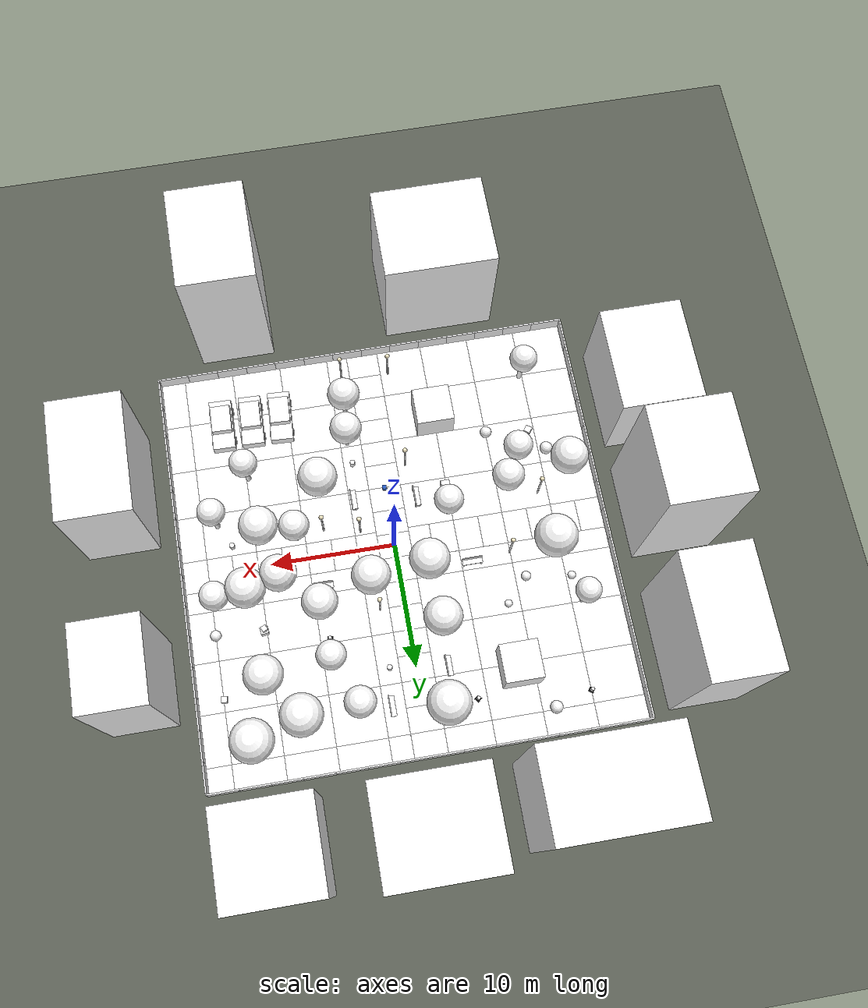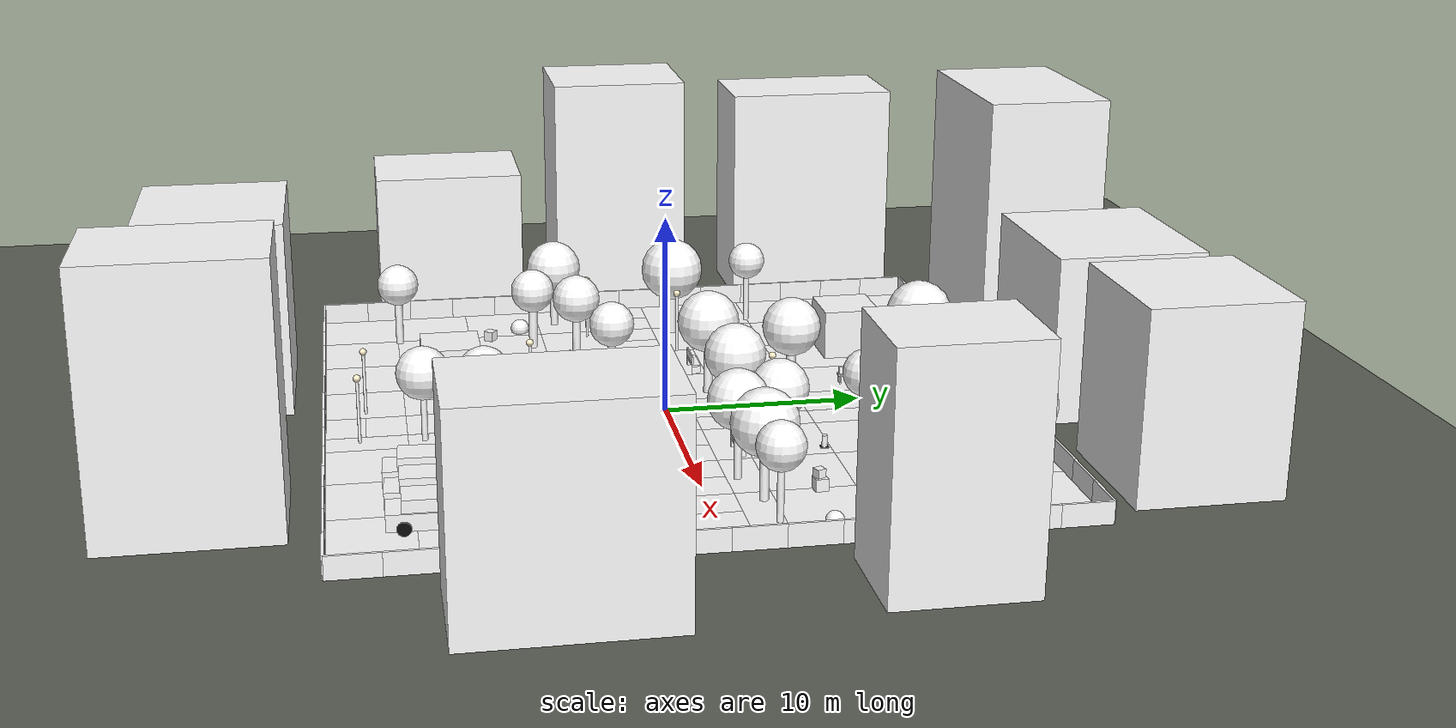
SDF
<?xml version="1.0" ?>
<!-- Generated by tools/generate_worlds.py (seeded procedural world). Do not edit by hand; re-generate instead. -->
<sdf version="1.9">
  <world name="park_0">
    <physics name="2ms" type="ignored">
      <max_step_size>0.002</max_step_size>
      <real_time_factor>1.0</real_time_factor>
    </physics>
    <plugin filename="gz-sim-physics-system" name="gz::sim::systems::Physics"/>
    <plugin filename="gz-sim-user-commands-system" name="gz::sim::systems::UserCommands"/>
    <plugin filename="gz-sim-scene-broadcaster-system" name="gz::sim::systems::SceneBroadcaster"/>
    <plugin filename="gz-sim-sensors-system" name="gz::sim::systems::Sensors">
      <render_engine>ogre2</render_engine>
    </plugin>

    <scene>
      <ambient>0.45 0.45 0.45 1</ambient>
      <background>0.70 0.80 0.95 1</background>
      <shadows>true</shadows>
      <grid>false</grid>
      <sky></sky>
    </scene>

    <light type="directional" name="sun">
      <cast_shadows>true</cast_shadows>
      <pose>0 0 20 0 0 0</pose>
      <diffuse>0.95 0.93 0.88 1</diffuse>
      <specular>0.3 0.3 0.3 1</specular>
      <direction>-0.4 0.25 -0.88</direction>
    </light>

    <model name="ground_plane">
      <static>true</static>
      <link name="link">
        <collision name="collision">
          <geometry><plane><normal>0 0 1</normal><size>300.000 300.000</size></plane></geometry>
          <surface><friction><ode><mu>1.0</mu><mu2>1.0</mu2></ode></friction></surface>
        </collision>
        <visual name="visual">
          <geometry><plane><normal>0 0 1</normal><size>300.000 300.000</size></plane></geometry>
          <material><ambient>0.350 0.370 0.330 1</ambient><diffuse>0.350 0.370 0.330 1</diffuse><specular>0.08 0.08 0.08 1</specular></material>
        </visual>
      </link>
    </model>

    <model name="ground_1">
      <static>true</static>
      <pose>0.000 0.000 0.000 0.0000 0.0000 0.0000</pose>
      <link name="link">
        <visual name="v0"><pose>-15.000 -15.000 0.004 0.0000 0.0000 0.0000</pose><geometry><plane><normal>0 0 1</normal><size>4.000 4.000</size></plane></geometry><material><ambient>1.000 1.000 1.000 1</ambient><diffuse>1.000 1.000 1.000 1</diffuse><specular>0.08 0.08 0.08 1</specular><pbr><metal><albedo_map>model://omnivla_textures/materials/textures/grass.png</albedo_map><roughness>0.95</roughness><metalness>0.0</metalness></metal></pbr></material></visual>
        <visual name="v1"><pose>-15.000 -11.000 0.004 0.0000 0.0000 0.0000</pose><geometry><plane><normal>0 0 1</normal><size>4.000 4.000</size></plane></geometry><material><ambient>1.000 1.000 1.000 1</ambient><diffuse>1.000 1.000 1.000 1</diffuse><specular>0.08 0.08 0.08 1</specular><pbr><metal><albedo_map>model://omnivla_textures/materials/textures/grass.png</albedo_map><roughness>0.95</roughness><metalness>0.0</metalness></metal></pbr></material></visual>
        <visual name="v2"><pose>-15.000 -7.000 0.004 0.0000 0.0000 0.0000</pose><geometry><plane><normal>0 0 1</normal><size>4.000 4.000</size></plane></geometry><material><ambient>1.000 1.000 1.000 1</ambient><diffuse>1.000 1.000 1.000 1</diffuse><specular>0.08 0.08 0.08 1</specular><pbr><metal><albedo_map>model://omnivla_textures/materials/textures/grass.png</albedo_map><roughness>0.95</roughness><metalness>0.0</metalness></metal></pbr></material></visual>
        <visual name="v3"><pose>-15.000 -3.000 0.004 0.0000 0.0000 0.0000</pose><geometry><plane><normal>0 0 1</normal><size>4.000 4.000</size></plane></geometry><material><ambient>1.000 1.000 1.000 1</ambient><diffuse>1.000 1.000 1.000 1</diffuse><specular>0.08 0.08 0.08 1</specular><pbr><metal><albedo_map>model://omnivla_textures/materials/textures/grass.png</albedo_map><roughness>0.95</roughness><metalness>0.0</metalness></metal></pbr></material></visual>
        <visual name="v4"><pose>-15.000 1.000 0.004 0.0000 0.0000 0.0000</pose><geometry><plane><normal>0 0 1</normal><size>4.000 4.000</size></plane></geometry><material><ambient>1.000 1.000 1.000 1</ambient><diffuse>1.000 1.000 1.000 1</diffuse><specular>0.08 0.08 0.08 1</specular><pbr><metal><albedo_map>model://omnivla_textures/materials/textures/grass.png</albedo_map><roughness>0.95</roughness><metalness>0.0</metalness></metal></pbr></material></visual>
        <visual name="v5"><pose>-15.000 5.000 0.004 0.0000 0.0000 0.0000</pose><geometry><plane><normal>0 0 1</normal><size>4.000 4.000</size></plane></geometry><material><ambient>1.000 1.000 1.000 1</ambient><diffuse>1.000 1.000 1.000 1</diffuse><specular>0.08 0.08 0.08 1</specular><pbr><metal><albedo_map>model://omnivla_textures/materials/textures/grass.png</albedo_map><roughness>0.95</roughness><metalness>0.0</metalness></metal></pbr></material></visual>
        <visual name="v6"><pose>-15.000 9.000 0.004 0.0000 0.0000 0.0000</pose><geometry><plane><normal>0 0 1</normal><size>4.000 4.000</size></plane></geometry><material><ambient>1.000 1.000 1.000 1</ambient><diffuse>1.000 1.000 1.000 1</diffuse><specular>0.08 0.08 0.08 1</specular><pbr><metal><albedo_map>model://omnivla_textures/materials/textures/grass.png</albedo_map><roughness>0.95</roughness><metalness>0.0</metalness></metal></pbr></material></visual>
        <visual name="v7"><pose>-15.000 13.000 0.004 0.0000 0.0000 0.0000</pose><geometry><plane><normal>0 0 1</normal><size>4.000 4.000</size></plane></geometry><material><ambient>1.000 1.000 1.000 1</ambient><diffuse>1.000 1.000 1.000 1</diffuse><specular>0.08 0.08 0.08 1</specular><pbr><metal><albedo_map>model://omnivla_textures/materials/textures/grass.png</albedo_map><roughness>0.95</roughness><metalness>0.0</metalness></metal></pbr></material></visual>
        <visual name="v8"><pose>-15.000 16.000 0.004 0.0000 0.0000 0.0000</pose><geometry><plane><normal>0 0 1</normal><size>4.000 2.000</size></plane></geometry><material><ambient>1.000 1.000 1.000 1</ambient><diffuse>1.000 1.000 1.000 1</diffuse><specular>0.08 0.08 0.08 1</specular><pbr><metal><albedo_map>model://omnivla_textures/materials/textures/grass.png</albedo_map><roughness>0.95</roughness><metalness>0.0</metalness></metal></pbr></material></visual>
        <visual name="v9"><pose>-11.000 -15.000 0.004 0.0000 0.0000 0.0000</pose><geometry><plane><normal>0 0 1</normal><size>4.000 4.000</size></plane></geometry><material><ambient>1.000 1.000 1.000 1</ambient><diffuse>1.000 1.000 1.000 1</diffuse><specular>0.08 0.08 0.08 1</specular><pbr><metal><albedo_map>model://omnivla_textures/materials/textures/grass.png</albedo_map><roughness>0.95</roughness><metalness>0.0</metalness></metal></pbr></material></visual>
        <visual name="v10"><pose>-11.000 -11.000 0.004 0.0000 0.0000 0.0000</pose><geometry><plane><normal>0 0 1</normal><size>4.000 4.000</size></plane></geometry><material><ambient>1.000 1.000 1.000 1</ambient><diffuse>1.000 1.000 1.000 1</diffuse><specular>0.08 0.08 0.08 1</specular><pbr><metal><albedo_map>model://omnivla_textures/materials/textures/grass.png</albedo_map><roughness>0.95</roughness><metalness>0.0</metalness></metal></pbr></material></visual>
        <visual name="v11"><pose>-11.000 -7.000 0.004 0.0000 0.0000 0.0000</pose><geometry><plane><normal>0 0 1</normal><size>4.000 4.000</size></plane></geometry><material><ambient>1.000 1.000 1.000 1</ambient><diffuse>1.000 1.000 1.000 1</diffuse><specular>0.08 0.08 0.08 1</specular><pbr><metal><albedo_map>model://omnivla_textures/materials/textures/grass.png</albedo_map><roughness>0.95</roughness><metalness>0.0</metalness></metal></pbr></material></visual>
        <visual name="v12"><pose>-11.000 -3.000 0.004 0.0000 0.0000 0.0000</pose><geometry><plane><normal>0 0 1</normal><size>4.000 4.000</size></plane></geometry><material><ambient>1.000 1.000 1.000 1</ambient><diffuse>1.000 1.000 1.000 1</diffuse><specular>0.08 0.08 0.08 1</specular><pbr><metal><albedo_map>model://omnivla_textures/materials/textures/grass.png</albedo_map><roughness>0.95</roughness><metalness>0.0</metalness></metal></pbr></material></visual>
        <visual name="v13"><pose>-11.000 1.000 0.004 0.0000 0.0000 0.0000</pose><geometry><plane><normal>0 0 1</normal><size>4.000 4.000</size></plane></geometry><material><ambient>1.000 1.000 1.000 1</ambient><diffuse>1.000 1.000 1.000 1</diffuse><specular>0.08 0.08 0.08 1</specular><pbr><metal><albedo_map>model://omnivla_textures/materials/textures/grass.png</albedo_map><roughness>0.95</roughness><metalness>0.0</metalness></metal></pbr></material></visual>
        <visual name="v14"><pose>-11.000 5.000 0.004 0.0000 0.0000 0.0000</pose><geometry><plane><normal>0 0 1</normal><size>4.000 4.000</size></plane></geometry><material><ambient>1.000 1.000 1.000 1</ambient><diffuse>1.000 1.000 1.000 1</diffuse><specular>0.08 0.08 0.08 1</specular><pbr><metal><albedo_map>model://omnivla_textures/materials/textures/grass.png</albedo_map><roughness>0.95</roughness><metalness>0.0</metalness></metal></pbr></material></visual>
        <visual name="v15"><pose>-11.000 9.000 0.004 0.0000 0.0000 0.0000</pose><geometry><plane><normal>0 0 1</normal><size>4.000 4.000</size></plane></geometry><material><ambient>1.000 1.000 1.000 1</ambient><diffuse>1.000 1.000 1.000 1</diffuse><specular>0.08 0.08 0.08 1</specular><pbr><metal><albedo_map>model://omnivla_textures/materials/textures/grass.png</albedo_map><roughness>0.95</roughness><metalness>0.0</metalness></metal></pbr></material></visual>
        <visual name="v16"><pose>-11.000 13.000 0.004 0.0000 0.0000 0.0000</pose><geometry><plane><normal>0 0 1</normal><size>4.000 4.000</size></plane></geometry><material><ambient>1.000 1.000 1.000 1</ambient><diffuse>1.000 1.000 1.000 1</diffuse><specular>0.08 0.08 0.08 1</specular><pbr><metal><albedo_map>model://omnivla_textures/materials/textures/grass.png</albedo_map><roughness>0.95</roughness><metalness>0.0</metalness></metal></pbr></material></visual>
        <visual name="v17"><pose>-11.000 16.000 0.004 0.0000 0.0000 0.0000</pose><geometry><plane><normal>0 0 1</normal><size>4.000 2.000</size></plane></geometry><material><ambient>1.000 1.000 1.000 1</ambient><diffuse>1.000 1.000 1.000 1</diffuse><specular>0.08 0.08 0.08 1</specular><pbr><metal><albedo_map>model://omnivla_textures/materials/textures/grass.png</albedo_map><roughness>0.95</roughness><metalness>0.0</metalness></metal></pbr></material></visual>
        <visual name="v18"><pose>-7.000 -15.000 0.004 0.0000 0.0000 0.0000</pose><geometry><plane><normal>0 0 1</normal><size>4.000 4.000</size></plane></geometry><material><ambient>1.000 1.000 1.000 1</ambient><diffuse>1.000 1.000 1.000 1</diffuse><specular>0.08 0.08 0.08 1</specular><pbr><metal><albedo_map>model://omnivla_textures/materials/textures/grass.png</albedo_map><roughness>0.95</roughness><metalness>0.0</metalness></metal></pbr></material></visual>
        <visual name="v19"><pose>-7.000 -11.000 0.004 0.0000 0.0000 0.0000</pose><geometry><plane><normal>0 0 1</normal><size>4.000 4.000</size></plane></geometry><material><ambient>1.000 1.000 1.000 1</ambient><diffuse>1.000 1.000 1.000 1</diffuse><specular>0.08 0.08 0.08 1</specular><pbr><metal><albedo_map>model://omnivla_textures/materials/textures/grass.png</albedo_map><roughness>0.95</roughness><metalness>0.0</metalness></metal></pbr></material></visual>
        <visual name="v20"><pose>-7.000 -7.000 0.004 0.0000 0.0000 0.0000</pose><geometry><plane><normal>0 0 1</normal><size>4.000 4.000</size></plane></geometry><material><ambient>1.000 1.000 1.000 1</ambient><diffuse>1.000 1.000 1.000 1</diffuse><specular>0.08 0.08 0.08 1</specular><pbr><metal><albedo_map>model://omnivla_textures/materials/textures/grass.png</albedo_map><roughness>0.95</roughness><metalness>0.0</metalness></metal></pbr></material></visual>
        <visual name="v21"><pose>-7.000 -3.000 0.004 0.0000 0.0000 0.0000</pose><geometry><plane><normal>0 0 1</normal><size>4.000 4.000</size></plane></geometry><material><ambient>1.000 1.000 1.000 1</ambient><diffuse>1.000 1.000 1.000 1</diffuse><specular>0.08 0.08 0.08 1</specular><pbr><metal><albedo_map>model://omnivla_textures/materials/textures/grass.png</albedo_map><roughness>0.95</roughness><metalness>0.0</metalness></metal></pbr></material></visual>
        <visual name="v22"><pose>-7.000 1.000 0.004 0.0000 0.0000 0.0000</pose><geometry><plane><normal>0 0 1</normal><size>4.000 4.000</size></plane></geometry><material><ambient>1.000 1.000 1.000 1</ambient><diffuse>1.000 1.000 1.000 1</diffuse><specular>0.08 0.08 0.08 1</specular><pbr><metal><albedo_map>model://omnivla_textures/materials/textures/grass.png</albedo_map><roughness>0.95</roughness><metalness>0.0</metalness></metal></pbr></material></visual>
        <visual name="v23"><pose>-7.000 5.000 0.004 0.0000 0.0000 0.0000</pose><geometry><plane><normal>0 0 1</normal><size>4.000 4.000</size></plane></geometry><material><ambient>1.000 1.000 1.000 1</ambient><diffuse>1.000 1.000 1.000 1</diffuse><specular>0.08 0.08 0.08 1</specular><pbr><metal><albedo_map>model://omnivla_textures/materials/textures/grass.png</albedo_map><roughness>0.95</roughness><metalness>0.0</metalness></metal></pbr></material></visual>
        <visual name="v24"><pose>-7.000 9.000 0.004 0.0000 0.0000 0.0000</pose><geometry><plane><normal>0 0 1</normal><size>4.000 4.000</size></plane></geometry><material><ambient>1.000 1.000 1.000 1</ambient><diffuse>1.000 1.000 1.000 1</diffuse><specular>0.08 0.08 0.08 1</specular><pbr><metal><albedo_map>model://omnivla_textures/materials/textures/grass.png</albedo_map><roughness>0.95</roughness><metalness>0.0</metalness></metal></pbr></material></visual>
        <visual name="v25"><pose>-7.000 13.000 0.004 0.0000 0.0000 0.0000</pose><geometry><plane><normal>0 0 1</normal><size>4.000 4.000</size></plane></geometry><material><ambient>1.000 1.000 1.000 1</ambient><diffuse>1.000 1.000 1.000 1</diffuse><specular>0.08 0.08 0.08 1</specular><pbr><metal><albedo_map>model://omnivla_textures/materials/textures/grass.png</albedo_map><roughness>0.95</roughness><metalness>0.0</metalness></metal></pbr></material></visual>
        <visual name="v26"><pose>-7.000 16.000 0.004 0.0000 0.0000 0.0000</pose><geometry><plane><normal>0 0 1</normal><size>4.000 2.000</size></plane></geometry><material><ambient>1.000 1.000 1.000 1</ambient><diffuse>1.000 1.000 1.000 1</diffuse><specular>0.08 0.08 0.08 1</specular><pbr><metal><albedo_map>model://omnivla_textures/materials/textures/grass.png</albedo_map><roughness>0.95</roughness><metalness>0.0</metalness></metal></pbr></material></visual>
        <visual name="v27"><pose>-3.000 -15.000 0.004 0.0000 0.0000 0.0000</pose><geometry><plane><normal>0 0 1</normal><size>4.000 4.000</size></plane></geometry><material><ambient>1.000 1.000 1.000 1</ambient><diffuse>1.000 1.000 1.000 1</diffuse><specular>0.08 0.08 0.08 1</specular><pbr><metal><albedo_map>model://omnivla_textures/materials/textures/grass.png</albedo_map><roughness>0.95</roughness><metalness>0.0</metalness></metal></pbr></material></visual>
        <visual name="v28"><pose>-3.000 -11.000 0.004 0.0000 0.0000 0.0000</pose><geometry><plane><normal>0 0 1</normal><size>4.000 4.000</size></plane></geometry><material><ambient>1.000 1.000 1.000 1</ambient><diffuse>1.000 1.000 1.000 1</diffuse><specular>0.08 0.08 0.08 1</specular><pbr><metal><albedo_map>model://omnivla_textures/materials/textures/grass.png</albedo_map><roughness>0.95</roughness><metalness>0.0</metalness></metal></pbr></material></visual>
        <visual name="v29"><pose>-3.000 -7.000 0.004 0.0000 0.0000 0.0000</pose><geometry><plane><normal>0 0 1</normal><size>4.000 4.000</size></plane></geometry><material><ambient>1.000 1.000 1.000 1</ambient><diffuse>1.000 1.000 1.000 1</diffuse><specular>0.08 0.08 0.08 1</specular><pbr><metal><albedo_map>model://omnivla_textures/materials/textures/grass.png</albedo_map><roughness>0.95</roughness><metalness>0.0</metalness></metal></pbr></material></visual>
        <visual name="v30"><pose>-3.000 -3.000 0.004 0.0000 0.0000 0.0000</pose><geometry><plane><normal>0 0 1</normal><size>4.000 4.000</size></plane></geometry><material><ambient>1.000 1.000 1.000 1</ambient><diffuse>1.000 1.000 1.000 1</diffuse><specular>0.08 0.08 0.08 1</specular><pbr><metal><albedo_map>model://omnivla_textures/materials/textures/grass.png</albedo_map><roughness>0.95</roughness><metalness>0.0</metalness></metal></pbr></material></visual>
        <visual name="v31"><pose>-3.000 1.000 0.004 0.0000 0.0000 0.0000</pose><geometry><plane><normal>0 0 1</normal><size>4.000 4.000</size></plane></geometry><material><ambient>1.000 1.000 1.000 1</ambient><diffuse>1.000 1.000 1.000 1</diffuse><specular>0.08 0.08 0.08 1</specular><pbr><metal><albedo_map>model://omnivla_textures/materials/textures/grass.png</albedo_map><roughness>0.95</roughness><metalness>0.0</metalness></metal></pbr></material></visual>
        <visual name="v32"><pose>-3.000 5.000 0.004 0.0000 0.0000 0.0000</pose><geometry><plane><normal>0 0 1</normal><size>4.000 4.000</size></plane></geometry><material><ambient>1.000 1.000 1.000 1</ambient><diffuse>1.000 1.000 1.000 1</diffuse><specular>0.08 0.08 0.08 1</specular><pbr><metal><albedo_map>model://omnivla_textures/materials/textures/grass.png</albedo_map><roughness>0.95</roughness><metalness>0.0</metalness></metal></pbr></material></visual>
        <visual name="v33"><pose>-3.000 9.000 0.004 0.0000 0.0000 0.0000</pose><geometry><plane><normal>0 0 1</normal><size>4.000 4.000</size></plane></geometry><material><ambient>1.000 1.000 1.000 1</ambient><diffuse>1.000 1.000 1.000 1</diffuse><specular>0.08 0.08 0.08 1</specular><pbr><metal><albedo_map>model://omnivla_textures/materials/textures/grass.png</albedo_map><roughness>0.95</roughness><metalness>0.0</metalness></metal></pbr></material></visual>
        <visual name="v34"><pose>-3.000 13.000 0.004 0.0000 0.0000 0.0000</pose><geometry><plane><normal>0 0 1</normal><size>4.000 4.000</size></plane></geometry><material><ambient>1.000 1.000 1.000 1</ambient><diffuse>1.000 1.000 1.000 1</diffuse><specular>0.08 0.08 0.08 1</specular><pbr><metal><albedo_map>model://omnivla_textures/materials/textures/grass.png</albedo_map><roughness>0.95</roughness><metalness>0.0</metalness></metal></pbr></material></visual>
        <visual name="v35"><pose>-3.000 16.000 0.004 0.0000 0.0000 0.0000</pose><geometry><plane><normal>0 0 1</normal><size>4.000 2.000</size></plane></geometry><material><ambient>1.000 1.000 1.000 1</ambient><diffuse>1.000 1.000 1.000 1</diffuse><specular>0.08 0.08 0.08 1</specular><pbr><metal><albedo_map>model://omnivla_textures/materials/textures/grass.png</albedo_map><roughness>0.95</roughness><metalness>0.0</metalness></metal></pbr></material></visual>
        <visual name="v36"><pose>1.000 -15.000 0.004 0.0000 0.0000 0.0000</pose><geometry><plane><normal>0 0 1</normal><size>4.000 4.000</size></plane></geometry><material><ambient>1.000 1.000 1.000 1</ambient><diffuse>1.000 1.000 1.000 1</diffuse><specular>0.08 0.08 0.08 1</specular><pbr><metal><albedo_map>model://omnivla_textures/materials/textures/grass.png</albedo_map><roughness>0.95</roughness><metalness>0.0</metalness></metal></pbr></material></visual>
        <visual name="v37"><pose>1.000 -11.000 0.004 0.0000 0.0000 0.0000</pose><geometry><plane><normal>0 0 1</normal><size>4.000 4.000</size></plane></geometry><material><ambient>1.000 1.000 1.000 1</ambient><diffuse>1.000 1.000 1.000 1</diffuse><specular>0.08 0.08 0.08 1</specular><pbr><metal><albedo_map>model://omnivla_textures/materials/textures/grass.png</albedo_map><roughness>0.95</roughness><metalness>0.0</metalness></metal></pbr></material></visual>
        <visual name="v38"><pose>1.000 -7.000 0.004 0.0000 0.0000 0.0000</pose><geometry><plane><normal>0 0 1</normal><size>4.000 4.000</size></plane></geometry><material><ambient>1.000 1.000 1.000 1</ambient><diffuse>1.000 1.000 1.000 1</diffuse><specular>0.08 0.08 0.08 1</specular><pbr><metal><albedo_map>model://omnivla_textures/materials/textures/grass.png</albedo_map><roughness>0.95</roughness><metalness>0.0</metalness></metal></pbr></material></visual>
        <visual name="v39"><pose>1.000 -3.000 0.004 0.0000 0.0000 0.0000</pose><geometry><plane><normal>0 0 1</normal><size>4.000 4.000</size></plane></geometry><material><ambient>1.000 1.000 1.000 1</ambient><diffuse>1.000 1.000 1.000 1</diffuse><specular>0.08 0.08 0.08 1</specular><pbr><metal><albedo_map>model://omnivla_textures/materials/textures/grass.png</albedo_map><roughness>0.95</roughness><metalness>0.0</metalness></metal></pbr></material></visual>
        <visual name="v40"><pose>1.000 1.000 0.004 0.0000 0.0000 0.0000</pose><geometry><plane><normal>0 0 1</normal><size>4.000 4.000</size></plane></geometry><material><ambient>1.000 1.000 1.000 1</ambient><diffuse>1.000 1.000 1.000 1</diffuse><specular>0.08 0.08 0.08 1</specular><pbr><metal><albedo_map>model://omnivla_textures/materials/textures/grass.png</albedo_map><roughness>0.95</roughness><metalness>0.0</metalness></metal></pbr></material></visual>
        <visual name="v41"><pose>1.000 5.000 0.004 0.0000 0.0000 0.0000</pose><geometry><plane><normal>0 0 1</normal><size>4.000 4.000</size></plane></geometry><material><ambient>1.000 1.000 1.000 1</ambient><diffuse>1.000 1.000 1.000 1</diffuse><specular>0.08 0.08 0.08 1</specular><pbr><metal><albedo_map>model://omnivla_textures/materials/textures/grass.png</albedo_map><roughness>0.95</roughness><metalness>0.0</metalness></metal></pbr></material></visual>
        <visual name="v42"><pose>1.000 9.000 0.004 0.0000 0.0000 0.0000</pose><geometry><plane><normal>0 0 1</normal><size>4.000 4.000</size></plane></geometry><material><ambient>1.000 1.000 1.000 1</ambient><diffuse>1.000 1.000 1.000 1</diffuse><specular>0.08 0.08 0.08 1</specular><pbr><metal><albedo_map>model://omnivla_textures/materials/textures/grass.png</albedo_map><roughness>0.95</roughness><metalness>0.0</metalness></metal></pbr></material></visual>
        <visual name="v43"><pose>1.000 13.000 0.004 0.0000 0.0000 0.0000</pose><geometry><plane><normal>0 0 1</normal><size>4.000 4.000</size></plane></geometry><material><ambient>1.000 1.000 1.000 1</ambient><diffuse>1.000 1.000 1.000 1</diffuse><specular>0.08 0.08 0.08 1</specular><pbr><metal><albedo_map>model://omnivla_textures/materials/textures/grass.png</albedo_map><roughness>0.95</roughness><metalness>0.0</metalness></metal></pbr></material></visual>
        <visual name="v44"><pose>1.000 16.000 0.004 0.0000 0.0000 0.0000</pose><geometry><plane><normal>0 0 1</normal><size>4.000 2.000</size></plane></geometry><material><ambient>1.000 1.000 1.000 1</ambient><diffuse>1.000 1.000 1.000 1</diffuse><specular>0.08 0.08 0.08 1</specular><pbr><metal><albedo_map>model://omnivla_textures/materials/textures/grass.png</albedo_map><roughness>0.95</roughness><metalness>0.0</metalness></metal></pbr></material></visual>
        <visual name="v45"><pose>5.000 -15.000 0.004 0.0000 0.0000 0.0000</pose><geometry><plane><normal>0 0 1</normal><size>4.000 4.000</size></plane></geometry><material><ambient>1.000 1.000 1.000 1</ambient><diffuse>1.000 1.000 1.000 1</diffuse><specular>0.08 0.08 0.08 1</specular><pbr><metal><albedo_map>model://omnivla_textures/materials/textures/grass.png</albedo_map><roughness>0.95</roughness><metalness>0.0</metalness></metal></pbr></material></visual>
        <visual name="v46"><pose>5.000 -11.000 0.004 0.0000 0.0000 0.0000</pose><geometry><plane><normal>0 0 1</normal><size>4.000 4.000</size></plane></geometry><material><ambient>1.000 1.000 1.000 1</ambient><diffuse>1.000 1.000 1.000 1</diffuse><specular>0.08 0.08 0.08 1</specular><pbr><metal><albedo_map>model://omnivla_textures/materials/textures/grass.png</albedo_map><roughness>0.95</roughness><metalness>0.0</metalness></metal></pbr></material></visual>
        <visual name="v47"><pose>5.000 -7.000 0.004 0.0000 0.0000 0.0000</pose><geometry><plane><normal>0 0 1</normal><size>4.000 4.000</size></plane></geometry><material><ambient>1.000 1.000 1.000 1</ambient><diffuse>1.000 1.000 1.000 1</diffuse><specular>0.08 0.08 0.08 1</specular><pbr><metal><albedo_map>model://omnivla_textures/materials/textures/grass.png</albedo_map><roughness>0.95</roughness><metalness>0.0</metalness></metal></pbr></material></visual>
        <visual name="v48"><pose>5.000 -3.000 0.004 0.0000 0.0000 0.0000</pose><geometry><plane><normal>0 0 1</normal><size>4.000 4.000</size></plane></geometry><material><ambient>1.000 1.000 1.000 1</ambient><diffuse>1.000 1.000 1.000 1</diffuse><specular>0.08 0.08 0.08 1</specular><pbr><metal><albedo_map>model://omnivla_textures/materials/textures/grass.png</albedo_map><roughness>0.95</roughness><metalness>0.0</metalness></metal></pbr></material></visual>
        <visual name="v49"><pose>5.000 1.000 0.004 0.0000 0.0000 0.0000</pose><geometry><plane><normal>0 0 1</normal><size>4.000 4.000</size></plane></geometry><material><ambient>1.000 1.000 1.000 1</ambient><diffuse>1.000 1.000 1.000 1</diffuse><specular>0.08 0.08 0.08 1</specular><pbr><metal><albedo_map>model://omnivla_textures/materials/textures/grass.png</albedo_map><roughness>0.95</roughness><metalness>0.0</metalness></metal></pbr></material></visual>
        <visual name="v50"><pose>5.000 5.000 0.004 0.0000 0.0000 0.0000</pose><geometry><plane><normal>0 0 1</normal><size>4.000 4.000</size></plane></geometry><material><ambient>1.000 1.000 1.000 1</ambient><diffuse>1.000 1.000 1.000 1</diffuse><specular>0.08 0.08 0.08 1</specular><pbr><metal><albedo_map>model://omnivla_textures/materials/textures/grass.png</albedo_map><roughness>0.95</roughness><metalness>0.0</metalness></metal></pbr></material></visual>
        <visual name="v51"><pose>5.000 9.000 0.004 0.0000 0.0000 0.0000</pose><geometry><plane><normal>0 0 1</normal><size>4.000 4.000</size></plane></geometry><material><ambient>1.000 1.000 1.000 1</ambient><diffuse>1.000 1.000 1.000 1</diffuse><specular>0.08 0.08 0.08 1</specular><pbr><metal><albedo_map>model://omnivla_textures/materials/textures/grass.png</albedo_map><roughness>0.95</roughness><metalness>0.0</metalness></metal></pbr></material></visual>
        <visual name="v52"><pose>5.000 13.000 0.004 0.0000 0.0000 0.0000</pose><geometry><plane><normal>0 0 1</normal><size>4.000 4.000</size></plane></geometry><material><ambient>1.000 1.000 1.000 1</ambient><diffuse>1.000 1.000 1.000 1</diffuse><specular>0.08 0.08 0.08 1</specular><pbr><metal><albedo_map>model://omnivla_textures/materials/textures/grass.png</albedo_map><roughness>0.95</roughness><metalness>0.0</metalness></metal></pbr></material></visual>
        <visual name="v53"><pose>5.000 16.000 0.004 0.0000 0.0000 0.0000</pose><geometry><plane><normal>0 0 1</normal><size>4.000 2.000</size></plane></geometry><material><ambient>1.000 1.000 1.000 1</ambient><diffuse>1.000 1.000 1.000 1</diffuse><specular>0.08 0.08 0.08 1</specular><pbr><metal><albedo_map>model://omnivla_textures/materials/textures/grass.png</albedo_map><roughness>0.95</roughness><metalness>0.0</metalness></metal></pbr></material></visual>
        <visual name="v54"><pose>9.000 -15.000 0.004 0.0000 0.0000 0.0000</pose><geometry><plane><normal>0 0 1</normal><size>4.000 4.000</size></plane></geometry><material><ambient>1.000 1.000 1.000 1</ambient><diffuse>1.000 1.000 1.000 1</diffuse><specular>0.08 0.08 0.08 1</specular><pbr><metal><albedo_map>model://omnivla_textures/materials/textures/asphalt.png</albedo_map><roughness>0.95</roughness><metalness>0.0</metalness></metal></pbr></material></visual>
        <visual name="v55"><pose>9.000 -11.000 0.004 0.0000 0.0000 0.0000</pose><geometry><plane><normal>0 0 1</normal><size>4.000 4.000</size></plane></geometry><material><ambient>1.000 1.000 1.000 1</ambient><diffuse>1.000 1.000 1.000 1</diffuse><specular>0.08 0.08 0.08 1</specular><pbr><metal><albedo_map>model://omnivla_textures/materials/textures/asphalt.png</albedo_map><roughness>0.95</roughness><metalness>0.0</metalness></metal></pbr></material></visual>
        <visual name="v56"><pose>9.000 -7.000 0.004 0.0000 0.0000 0.0000</pose><geometry><plane><normal>0 0 1</normal><size>4.000 4.000</size></plane></geometry><material><ambient>1.000 1.000 1.000 1</ambient><diffuse>1.000 1.000 1.000 1</diffuse><specular>0.08 0.08 0.08 1</specular><pbr><metal><albedo_map>model://omnivla_textures/materials/textures/grass.png</albedo_map><roughness>0.95</roughness><metalness>0.0</metalness></metal></pbr></material></visual>
        <visual name="v57"><pose>9.000 -3.000 0.004 0.0000 0.0000 0.0000</pose><geometry><plane><normal>0 0 1</normal><size>4.000 4.000</size></plane></geometry><material><ambient>1.000 1.000 1.000 1</ambient><diffuse>1.000 1.000 1.000 1</diffuse><specular>0.08 0.08 0.08 1</specular><pbr><metal><albedo_map>model://omnivla_textures/materials/textures/grass.png</albedo_map><roughness>0.95</roughness><metalness>0.0</metalness></metal></pbr></material></visual>
        <visual name="v58"><pose>9.000 1.000 0.004 0.0000 0.0000 0.0000</pose><geometry><plane><normal>0 0 1</normal><size>4.000 4.000</size></plane></geometry><material><ambient>1.000 1.000 1.000 1</ambient><diffuse>1.000 1.000 1.000 1</diffuse><specular>0.08 0.08 0.08 1</specular><pbr><metal><albedo_map>model://omnivla_textures/materials/textures/grass.png</albedo_map><roughness>0.95</roughness><metalness>0.0</metalness></metal></pbr></material></visual>
        <visual name="v59"><pose>9.000 5.000 0.004 0.0000 0.0000 0.0000</pose><geometry><plane><normal>0 0 1</normal><size>4.000 4.000</size></plane></geometry><material><ambient>1.000 1.000 1.000 1</ambient><diffuse>1.000 1.000 1.000 1</diffuse><specular>0.08 0.08 0.08 1</specular><pbr><metal><albedo_map>model://omnivla_textures/materials/textures/grass.png</albedo_map><roughness>0.95</roughness><metalness>0.0</metalness></metal></pbr></material></visual>
        <visual name="v60"><pose>9.000 9.000 0.004 0.0000 0.0000 0.0000</pose><geometry><plane><normal>0 0 1</normal><size>4.000 4.000</size></plane></geometry><material><ambient>1.000 1.000 1.000 1</ambient><diffuse>1.000 1.000 1.000 1</diffuse><specular>0.08 0.08 0.08 1</specular><pbr><metal><albedo_map>model://omnivla_textures/materials/textures/grass.png</albedo_map><roughness>0.95</roughness><metalness>0.0</metalness></metal></pbr></material></visual>
        <visual name="v61"><pose>9.000 13.000 0.004 0.0000 0.0000 0.0000</pose><geometry><plane><normal>0 0 1</normal><size>4.000 4.000</size></plane></geometry><material><ambient>1.000 1.000 1.000 1</ambient><diffuse>1.000 1.000 1.000 1</diffuse><specular>0.08 0.08 0.08 1</specular><pbr><metal><albedo_map>model://omnivla_textures/materials/textures/grass.png</albedo_map><roughness>0.95</roughness><metalness>0.0</metalness></metal></pbr></material></visual>
        <visual name="v62"><pose>9.000 16.000 0.004 0.0000 0.0000 0.0000</pose><geometry><plane><normal>0 0 1</normal><size>4.000 2.000</size></plane></geometry><material><ambient>1.000 1.000 1.000 1</ambient><diffuse>1.000 1.000 1.000 1</diffuse><specular>0.08 0.08 0.08 1</specular><pbr><metal><albedo_map>model://omnivla_textures/materials/textures/grass.png</albedo_map><roughness>0.95</roughness><metalness>0.0</metalness></metal></pbr></material></visual>
        <visual name="v63"><pose>13.000 -15.000 0.004 0.0000 0.0000 0.0000</pose><geometry><plane><normal>0 0 1</normal><size>4.000 4.000</size></plane></geometry><material><ambient>1.000 1.000 1.000 1</ambient><diffuse>1.000 1.000 1.000 1</diffuse><specular>0.08 0.08 0.08 1</specular><pbr><metal><albedo_map>model://omnivla_textures/materials/textures/asphalt.png</albedo_map><roughness>0.95</roughness><metalness>0.0</metalness></metal></pbr></material></visual>
        <visual name="v64"><pose>13.000 -11.000 0.004 0.0000 0.0000 0.0000</pose><geometry><plane><normal>0 0 1</normal><size>4.000 4.000</size></plane></geometry><material><ambient>1.000 1.000 1.000 1</ambient><diffuse>1.000 1.000 1.000 1</diffuse><specular>0.08 0.08 0.08 1</specular><pbr><metal><albedo_map>model://omnivla_textures/materials/textures/asphalt.png</albedo_map><roughness>0.95</roughness><metalness>0.0</metalness></metal></pbr></material></visual>
        <visual name="v65"><pose>13.000 -7.000 0.004 0.0000 0.0000 0.0000</pose><geometry><plane><normal>0 0 1</normal><size>4.000 4.000</size></plane></geometry><material><ambient>1.000 1.000 1.000 1</ambient><diffuse>1.000 1.000 1.000 1</diffuse><specular>0.08 0.08 0.08 1</specular><pbr><metal><albedo_map>model://omnivla_textures/materials/textures/grass.png</albedo_map><roughness>0.95</roughness><metalness>0.0</metalness></metal></pbr></material></visual>
        <visual name="v66"><pose>13.000 -3.000 0.004 0.0000 0.0000 0.0000</pose><geometry><plane><normal>0 0 1</normal><size>4.000 4.000</size></plane></geometry><material><ambient>1.000 1.000 1.000 1</ambient><diffuse>1.000 1.000 1.000 1</diffuse><specular>0.08 0.08 0.08 1</specular><pbr><metal><albedo_map>model://omnivla_textures/materials/textures/grass.png</albedo_map><roughness>0.95</roughness><metalness>0.0</metalness></metal></pbr></material></visual>
        <visual name="v67"><pose>13.000 1.000 0.004 0.0000 0.0000 0.0000</pose><geometry><plane><normal>0 0 1</normal><size>4.000 4.000</size></plane></geometry><material><ambient>1.000 1.000 1.000 1</ambient><diffuse>1.000 1.000 1.000 1</diffuse><specular>0.08 0.08 0.08 1</specular><pbr><metal><albedo_map>model://omnivla_textures/materials/textures/grass.png</albedo_map><roughness>0.95</roughness><metalness>0.0</metalness></metal></pbr></material></visual>
        <visual name="v68"><pose>13.000 5.000 0.004 0.0000 0.0000 0.0000</pose><geometry><plane><normal>0 0 1</normal><size>4.000 4.000</size></plane></geometry><material><ambient>1.000 1.000 1.000 1</ambient><diffuse>1.000 1.000 1.000 1</diffuse><specular>0.08 0.08 0.08 1</specular><pbr><metal><albedo_map>model://omnivla_textures/materials/textures/grass.png</albedo_map><roughness>0.95</roughness><metalness>0.0</metalness></metal></pbr></material></visual>
        <visual name="v69"><pose>13.000 9.000 0.004 0.0000 0.0000 0.0000</pose><geometry><plane><normal>0 0 1</normal><size>4.000 4.000</size></plane></geometry><material><ambient>1.000 1.000 1.000 1</ambient><diffuse>1.000 1.000 1.000 1</diffuse><specular>0.08 0.08 0.08 1</specular><pbr><metal><albedo_map>model://omnivla_textures/materials/textures/grass.png</albedo_map><roughness>0.95</roughness><metalness>0.0</metalness></metal></pbr></material></visual>
        <visual name="v70"><pose>13.000 13.000 0.004 0.0000 0.0000 0.0000</pose><geometry><plane><normal>0 0 1</normal><size>4.000 4.000</size></plane></geometry><material><ambient>1.000 1.000 1.000 1</ambient><diffuse>1.000 1.000 1.000 1</diffuse><specular>0.08 0.08 0.08 1</specular><pbr><metal><albedo_map>model://omnivla_textures/materials/textures/grass.png</albedo_map><roughness>0.95</roughness><metalness>0.0</metalness></metal></pbr></material></visual>
        <visual name="v71"><pose>13.000 16.000 0.004 0.0000 0.0000 0.0000</pose><geometry><plane><normal>0 0 1</normal><size>4.000 2.000</size></plane></geometry><material><ambient>1.000 1.000 1.000 1</ambient><diffuse>1.000 1.000 1.000 1</diffuse><specular>0.08 0.08 0.08 1</specular><pbr><metal><albedo_map>model://omnivla_textures/materials/textures/grass.png</albedo_map><roughness>0.95</roughness><metalness>0.0</metalness></metal></pbr></material></visual>
        <visual name="v72"><pose>16.000 -15.000 0.004 0.0000 0.0000 0.0000</pose><geometry><plane><normal>0 0 1</normal><size>2.000 4.000</size></plane></geometry><material><ambient>1.000 1.000 1.000 1</ambient><diffuse>1.000 1.000 1.000 1</diffuse><specular>0.08 0.08 0.08 1</specular><pbr><metal><albedo_map>model://omnivla_textures/materials/textures/grass.png</albedo_map><roughness>0.95</roughness><metalness>0.0</metalness></metal></pbr></material></visual>
        <visual name="v73"><pose>16.000 -11.000 0.004 0.0000 0.0000 0.0000</pose><geometry><plane><normal>0 0 1</normal><size>2.000 4.000</size></plane></geometry><material><ambient>1.000 1.000 1.000 1</ambient><diffuse>1.000 1.000 1.000 1</diffuse><specular>0.08 0.08 0.08 1</specular><pbr><metal><albedo_map>model://omnivla_textures/materials/textures/grass.png</albedo_map><roughness>0.95</roughness><metalness>0.0</metalness></metal></pbr></material></visual>
        <visual name="v74"><pose>16.000 -7.000 0.004 0.0000 0.0000 0.0000</pose><geometry><plane><normal>0 0 1</normal><size>2.000 4.000</size></plane></geometry><material><ambient>1.000 1.000 1.000 1</ambient><diffuse>1.000 1.000 1.000 1</diffuse><specular>0.08 0.08 0.08 1</specular><pbr><metal><albedo_map>model://omnivla_textures/materials/textures/grass.png</albedo_map><roughness>0.95</roughness><metalness>0.0</metalness></metal></pbr></material></visual>
        <visual name="v75"><pose>16.000 -3.000 0.004 0.0000 0.0000 0.0000</pose><geometry><plane><normal>0 0 1</normal><size>2.000 4.000</size></plane></geometry><material><ambient>1.000 1.000 1.000 1</ambient><diffuse>1.000 1.000 1.000 1</diffuse><specular>0.08 0.08 0.08 1</specular><pbr><metal><albedo_map>model://omnivla_textures/materials/textures/grass.png</albedo_map><roughness>0.95</roughness><metalness>0.0</metalness></metal></pbr></material></visual>
        <visual name="v76"><pose>16.000 1.000 0.004 0.0000 0.0000 0.0000</pose><geometry><plane><normal>0 0 1</normal><size>2.000 4.000</size></plane></geometry><material><ambient>1.000 1.000 1.000 1</ambient><diffuse>1.000 1.000 1.000 1</diffuse><specular>0.08 0.08 0.08 1</specular><pbr><metal><albedo_map>model://omnivla_textures/materials/textures/grass.png</albedo_map><roughness>0.95</roughness><metalness>0.0</metalness></metal></pbr></material></visual>
        <visual name="v77"><pose>16.000 5.000 0.004 0.0000 0.0000 0.0000</pose><geometry><plane><normal>0 0 1</normal><size>2.000 4.000</size></plane></geometry><material><ambient>1.000 1.000 1.000 1</ambient><diffuse>1.000 1.000 1.000 1</diffuse><specular>0.08 0.08 0.08 1</specular><pbr><metal><albedo_map>model://omnivla_textures/materials/textures/grass.png</albedo_map><roughness>0.95</roughness><metalness>0.0</metalness></metal></pbr></material></visual>
        <visual name="v78"><pose>16.000 9.000 0.004 0.0000 0.0000 0.0000</pose><geometry><plane><normal>0 0 1</normal><size>2.000 4.000</size></plane></geometry><material><ambient>1.000 1.000 1.000 1</ambient><diffuse>1.000 1.000 1.000 1</diffuse><specular>0.08 0.08 0.08 1</specular><pbr><metal><albedo_map>model://omnivla_textures/materials/textures/grass.png</albedo_map><roughness>0.95</roughness><metalness>0.0</metalness></metal></pbr></material></visual>
        <visual name="v79"><pose>16.000 13.000 0.004 0.0000 0.0000 0.0000</pose><geometry><plane><normal>0 0 1</normal><size>2.000 4.000</size></plane></geometry><material><ambient>1.000 1.000 1.000 1</ambient><diffuse>1.000 1.000 1.000 1</diffuse><specular>0.08 0.08 0.08 1</specular><pbr><metal><albedo_map>model://omnivla_textures/materials/textures/grass.png</albedo_map><roughness>0.95</roughness><metalness>0.0</metalness></metal></pbr></material></visual>
        <visual name="v80"><pose>16.000 16.000 0.004 0.0000 0.0000 0.0000</pose><geometry><plane><normal>0 0 1</normal><size>2.000 2.000</size></plane></geometry><material><ambient>1.000 1.000 1.000 1</ambient><diffuse>1.000 1.000 1.000 1</diffuse><specular>0.08 0.08 0.08 1</specular><pbr><metal><albedo_map>model://omnivla_textures/materials/textures/grass.png</albedo_map><roughness>0.95</roughness><metalness>0.0</metalness></metal></pbr></material></visual>
      </link>
    </model>
    <model name="paths_2">
      <static>true</static>
      <pose>0.000 0.000 0.000 0.0000 0.0000 0.0000</pose>
      <link name="link">
        <visual name="v0"><pose>-16.000 0.000 0.008 0.0000 0.0000 0.0000</pose><geometry><plane><normal>0 0 1</normal><size>2.000 2.600</size></plane></geometry><material><ambient>1.000 1.000 1.000 1</ambient><diffuse>1.000 1.000 1.000 1</diffuse><specular>0.08 0.08 0.08 1</specular><pbr><metal><albedo_map>model://omnivla_textures/materials/textures/paving.png</albedo_map><roughness>0.85</roughness><metalness>0.0</metalness></metal></pbr></material></visual>
        <visual name="v1"><pose>0.000 -16.000 0.009 0.0000 0.0000 0.0000</pose><geometry><plane><normal>0 0 1</normal><size>2.600 2.000</size></plane></geometry><material><ambient>1.000 1.000 1.000 1</ambient><diffuse>1.000 1.000 1.000 1</diffuse><specular>0.08 0.08 0.08 1</specular><pbr><metal><albedo_map>model://omnivla_textures/materials/textures/paving.png</albedo_map><roughness>0.85</roughness><metalness>0.0</metalness></metal></pbr></material></visual>
        <visual name="v2"><pose>-14.000 0.000 0.008 0.0000 0.0000 0.0000</pose><geometry><plane><normal>0 0 1</normal><size>2.000 2.600</size></plane></geometry><material><ambient>1.000 1.000 1.000 1</ambient><diffuse>1.000 1.000 1.000 1</diffuse><specular>0.08 0.08 0.08 1</specular><pbr><metal><albedo_map>model://omnivla_textures/materials/textures/paving.png</albedo_map><roughness>0.85</roughness><metalness>0.0</metalness></metal></pbr></material></visual>
        <visual name="v3"><pose>0.000 -14.000 0.009 0.0000 0.0000 0.0000</pose><geometry><plane><normal>0 0 1</normal><size>2.600 2.000</size></plane></geometry><material><ambient>1.000 1.000 1.000 1</ambient><diffuse>1.000 1.000 1.000 1</diffuse><specular>0.08 0.08 0.08 1</specular><pbr><metal><albedo_map>model://omnivla_textures/materials/textures/paving.png</albedo_map><roughness>0.85</roughness><metalness>0.0</metalness></metal></pbr></material></visual>
        <visual name="v4"><pose>-12.000 0.000 0.008 0.0000 0.0000 0.0000</pose><geometry><plane><normal>0 0 1</normal><size>2.000 2.600</size></plane></geometry><material><ambient>1.000 1.000 1.000 1</ambient><diffuse>1.000 1.000 1.000 1</diffuse><specular>0.08 0.08 0.08 1</specular><pbr><metal><albedo_map>model://omnivla_textures/materials/textures/paving.png</albedo_map><roughness>0.85</roughness><metalness>0.0</metalness></metal></pbr></material></visual>
        <visual name="v5"><pose>0.000 -12.000 0.009 0.0000 0.0000 0.0000</pose><geometry><plane><normal>0 0 1</normal><size>2.600 2.000</size></plane></geometry><material><ambient>1.000 1.000 1.000 1</ambient><diffuse>1.000 1.000 1.000 1</diffuse><specular>0.08 0.08 0.08 1</specular><pbr><metal><albedo_map>model://omnivla_textures/materials/textures/paving.png</albedo_map><roughness>0.85</roughness><metalness>0.0</metalness></metal></pbr></material></visual>
        <visual name="v6"><pose>-10.000 0.000 0.008 0.0000 0.0000 0.0000</pose><geometry><plane><normal>0 0 1</normal><size>2.000 2.600</size></plane></geometry><material><ambient>1.000 1.000 1.000 1</ambient><diffuse>1.000 1.000 1.000 1</diffuse><specular>0.08 0.08 0.08 1</specular><pbr><metal><albedo_map>model://omnivla_textures/materials/textures/paving.png</albedo_map><roughness>0.85</roughness><metalness>0.0</metalness></metal></pbr></material></visual>
        <visual name="v7"><pose>0.000 -10.000 0.009 0.0000 0.0000 0.0000</pose><geometry><plane><normal>0 0 1</normal><size>2.600 2.000</size></plane></geometry><material><ambient>1.000 1.000 1.000 1</ambient><diffuse>1.000 1.000 1.000 1</diffuse><specular>0.08 0.08 0.08 1</specular><pbr><metal><albedo_map>model://omnivla_textures/materials/textures/paving.png</albedo_map><roughness>0.85</roughness><metalness>0.0</metalness></metal></pbr></material></visual>
        <visual name="v8"><pose>-8.000 0.000 0.008 0.0000 0.0000 0.0000</pose><geometry><plane><normal>0 0 1</normal><size>2.000 2.600</size></plane></geometry><material><ambient>1.000 1.000 1.000 1</ambient><diffuse>1.000 1.000 1.000 1</diffuse><specular>0.08 0.08 0.08 1</specular><pbr><metal><albedo_map>model://omnivla_textures/materials/textures/paving.png</albedo_map><roughness>0.85</roughness><metalness>0.0</metalness></metal></pbr></material></visual>
        <visual name="v9"><pose>0.000 -8.000 0.009 0.0000 0.0000 0.0000</pose><geometry><plane><normal>0 0 1</normal><size>2.600 2.000</size></plane></geometry><material><ambient>1.000 1.000 1.000 1</ambient><diffuse>1.000 1.000 1.000 1</diffuse><specular>0.08 0.08 0.08 1</specular><pbr><metal><albedo_map>model://omnivla_textures/materials/textures/paving.png</albedo_map><roughness>0.85</roughness><metalness>0.0</metalness></metal></pbr></material></visual>
        <visual name="v10"><pose>-6.000 0.000 0.008 0.0000 0.0000 0.0000</pose><geometry><plane><normal>0 0 1</normal><size>2.000 2.600</size></plane></geometry><material><ambient>1.000 1.000 1.000 1</ambient><diffuse>1.000 1.000 1.000 1</diffuse><specular>0.08 0.08 0.08 1</specular><pbr><metal><albedo_map>model://omnivla_textures/materials/textures/paving.png</albedo_map><roughness>0.85</roughness><metalness>0.0</metalness></metal></pbr></material></visual>
        <visual name="v11"><pose>0.000 -6.000 0.009 0.0000 0.0000 0.0000</pose><geometry><plane><normal>0 0 1</normal><size>2.600 2.000</size></plane></geometry><material><ambient>1.000 1.000 1.000 1</ambient><diffuse>1.000 1.000 1.000 1</diffuse><specular>0.08 0.08 0.08 1</specular><pbr><metal><albedo_map>model://omnivla_textures/materials/textures/paving.png</albedo_map><roughness>0.85</roughness><metalness>0.0</metalness></metal></pbr></material></visual>
        <visual name="v12"><pose>-4.000 0.000 0.008 0.0000 0.0000 0.0000</pose><geometry><plane><normal>0 0 1</normal><size>2.000 2.600</size></plane></geometry><material><ambient>1.000 1.000 1.000 1</ambient><diffuse>1.000 1.000 1.000 1</diffuse><specular>0.08 0.08 0.08 1</specular><pbr><metal><albedo_map>model://omnivla_textures/materials/textures/paving.png</albedo_map><roughness>0.85</roughness><metalness>0.0</metalness></metal></pbr></material></visual>
        <visual name="v13"><pose>0.000 -4.000 0.009 0.0000 0.0000 0.0000</pose><geometry><plane><normal>0 0 1</normal><size>2.600 2.000</size></plane></geometry><material><ambient>1.000 1.000 1.000 1</ambient><diffuse>1.000 1.000 1.000 1</diffuse><specular>0.08 0.08 0.08 1</specular><pbr><metal><albedo_map>model://omnivla_textures/materials/textures/paving.png</albedo_map><roughness>0.85</roughness><metalness>0.0</metalness></metal></pbr></material></visual>
        <visual name="v14"><pose>-2.000 0.000 0.008 0.0000 0.0000 0.0000</pose><geometry><plane><normal>0 0 1</normal><size>2.000 2.600</size></plane></geometry><material><ambient>1.000 1.000 1.000 1</ambient><diffuse>1.000 1.000 1.000 1</diffuse><specular>0.08 0.08 0.08 1</specular><pbr><metal><albedo_map>model://omnivla_textures/materials/textures/paving.png</albedo_map><roughness>0.85</roughness><metalness>0.0</metalness></metal></pbr></material></visual>
        <visual name="v15"><pose>0.000 -2.000 0.009 0.0000 0.0000 0.0000</pose><geometry><plane><normal>0 0 1</normal><size>2.600 2.000</size></plane></geometry><material><ambient>1.000 1.000 1.000 1</ambient><diffuse>1.000 1.000 1.000 1</diffuse><specular>0.08 0.08 0.08 1</specular><pbr><metal><albedo_map>model://omnivla_textures/materials/textures/paving.png</albedo_map><roughness>0.85</roughness><metalness>0.0</metalness></metal></pbr></material></visual>
        <visual name="v16"><pose>0.000 0.000 0.008 0.0000 0.0000 0.0000</pose><geometry><plane><normal>0 0 1</normal><size>2.000 2.600</size></plane></geometry><material><ambient>1.000 1.000 1.000 1</ambient><diffuse>1.000 1.000 1.000 1</diffuse><specular>0.08 0.08 0.08 1</specular><pbr><metal><albedo_map>model://omnivla_textures/materials/textures/paving.png</albedo_map><roughness>0.85</roughness><metalness>0.0</metalness></metal></pbr></material></visual>
        <visual name="v17"><pose>0.000 0.000 0.009 0.0000 0.0000 0.0000</pose><geometry><plane><normal>0 0 1</normal><size>2.600 2.000</size></plane></geometry><material><ambient>1.000 1.000 1.000 1</ambient><diffuse>1.000 1.000 1.000 1</diffuse><specular>0.08 0.08 0.08 1</specular><pbr><metal><albedo_map>model://omnivla_textures/materials/textures/paving.png</albedo_map><roughness>0.85</roughness><metalness>0.0</metalness></metal></pbr></material></visual>
        <visual name="v18"><pose>2.000 0.000 0.008 0.0000 0.0000 0.0000</pose><geometry><plane><normal>0 0 1</normal><size>2.000 2.600</size></plane></geometry><material><ambient>1.000 1.000 1.000 1</ambient><diffuse>1.000 1.000 1.000 1</diffuse><specular>0.08 0.08 0.08 1</specular><pbr><metal><albedo_map>model://omnivla_textures/materials/textures/paving.png</albedo_map><roughness>0.85</roughness><metalness>0.0</metalness></metal></pbr></material></visual>
        <visual name="v19"><pose>0.000 2.000 0.009 0.0000 0.0000 0.0000</pose><geometry><plane><normal>0 0 1</normal><size>2.600 2.000</size></plane></geometry><material><ambient>1.000 1.000 1.000 1</ambient><diffuse>1.000 1.000 1.000 1</diffuse><specular>0.08 0.08 0.08 1</specular><pbr><metal><albedo_map>model://omnivla_textures/materials/textures/paving.png</albedo_map><roughness>0.85</roughness><metalness>0.0</metalness></metal></pbr></material></visual>
        <visual name="v20"><pose>4.000 0.000 0.008 0.0000 0.0000 0.0000</pose><geometry><plane><normal>0 0 1</normal><size>2.000 2.600</size></plane></geometry><material><ambient>1.000 1.000 1.000 1</ambient><diffuse>1.000 1.000 1.000 1</diffuse><specular>0.08 0.08 0.08 1</specular><pbr><metal><albedo_map>model://omnivla_textures/materials/textures/paving.png</albedo_map><roughness>0.85</roughness><metalness>0.0</metalness></metal></pbr></material></visual>
        <visual name="v21"><pose>0.000 4.000 0.009 0.0000 0.0000 0.0000</pose><geometry><plane><normal>0 0 1</normal><size>2.600 2.000</size></plane></geometry><material><ambient>1.000 1.000 1.000 1</ambient><diffuse>1.000 1.000 1.000 1</diffuse><specular>0.08 0.08 0.08 1</specular><pbr><metal><albedo_map>model://omnivla_textures/materials/textures/paving.png</albedo_map><roughness>0.85</roughness><metalness>0.0</metalness></metal></pbr></material></visual>
        <visual name="v22"><pose>6.000 0.000 0.008 0.0000 0.0000 0.0000</pose><geometry><plane><normal>0 0 1</normal><size>2.000 2.600</size></plane></geometry><material><ambient>1.000 1.000 1.000 1</ambient><diffuse>1.000 1.000 1.000 1</diffuse><specular>0.08 0.08 0.08 1</specular><pbr><metal><albedo_map>model://omnivla_textures/materials/textures/paving.png</albedo_map><roughness>0.85</roughness><metalness>0.0</metalness></metal></pbr></material></visual>
        <visual name="v23"><pose>0.000 6.000 0.009 0.0000 0.0000 0.0000</pose><geometry><plane><normal>0 0 1</normal><size>2.600 2.000</size></plane></geometry><material><ambient>1.000 1.000 1.000 1</ambient><diffuse>1.000 1.000 1.000 1</diffuse><specular>0.08 0.08 0.08 1</specular><pbr><metal><albedo_map>model://omnivla_textures/materials/textures/paving.png</albedo_map><roughness>0.85</roughness><metalness>0.0</metalness></metal></pbr></material></visual>
        <visual name="v24"><pose>8.000 0.000 0.008 0.0000 0.0000 0.0000</pose><geometry><plane><normal>0 0 1</normal><size>2.000 2.600</size></plane></geometry><material><ambient>1.000 1.000 1.000 1</ambient><diffuse>1.000 1.000 1.000 1</diffuse><specular>0.08 0.08 0.08 1</specular><pbr><metal><albedo_map>model://omnivla_textures/materials/textures/paving.png</albedo_map><roughness>0.85</roughness><metalness>0.0</metalness></metal></pbr></material></visual>
        <visual name="v25"><pose>0.000 8.000 0.009 0.0000 0.0000 0.0000</pose><geometry><plane><normal>0 0 1</normal><size>2.600 2.000</size></plane></geometry><material><ambient>1.000 1.000 1.000 1</ambient><diffuse>1.000 1.000 1.000 1</diffuse><specular>0.08 0.08 0.08 1</specular><pbr><metal><albedo_map>model://omnivla_textures/materials/textures/paving.png</albedo_map><roughness>0.85</roughness><metalness>0.0</metalness></metal></pbr></material></visual>
        <visual name="v26"><pose>10.000 0.000 0.008 0.0000 0.0000 0.0000</pose><geometry><plane><normal>0 0 1</normal><size>2.000 2.600</size></plane></geometry><material><ambient>1.000 1.000 1.000 1</ambient><diffuse>1.000 1.000 1.000 1</diffuse><specular>0.08 0.08 0.08 1</specular><pbr><metal><albedo_map>model://omnivla_textures/materials/textures/paving.png</albedo_map><roughness>0.85</roughness><metalness>0.0</metalness></metal></pbr></material></visual>
        <visual name="v27"><pose>0.000 10.000 0.009 0.0000 0.0000 0.0000</pose><geometry><plane><normal>0 0 1</normal><size>2.600 2.000</size></plane></geometry><material><ambient>1.000 1.000 1.000 1</ambient><diffuse>1.000 1.000 1.000 1</diffuse><specular>0.08 0.08 0.08 1</specular><pbr><metal><albedo_map>model://omnivla_textures/materials/textures/paving.png</albedo_map><roughness>0.85</roughness><metalness>0.0</metalness></metal></pbr></material></visual>
        <visual name="v28"><pose>12.000 0.000 0.008 0.0000 0.0000 0.0000</pose><geometry><plane><normal>0 0 1</normal><size>2.000 2.600</size></plane></geometry><material><ambient>1.000 1.000 1.000 1</ambient><diffuse>1.000 1.000 1.000 1</diffuse><specular>0.08 0.08 0.08 1</specular><pbr><metal><albedo_map>model://omnivla_textures/materials/textures/paving.png</albedo_map><roughness>0.85</roughness><metalness>0.0</metalness></metal></pbr></material></visual>
        <visual name="v29"><pose>0.000 12.000 0.009 0.0000 0.0000 0.0000</pose><geometry><plane><normal>0 0 1</normal><size>2.600 2.000</size></plane></geometry><material><ambient>1.000 1.000 1.000 1</ambient><diffuse>1.000 1.000 1.000 1</diffuse><specular>0.08 0.08 0.08 1</specular><pbr><metal><albedo_map>model://omnivla_textures/materials/textures/paving.png</albedo_map><roughness>0.85</roughness><metalness>0.0</metalness></metal></pbr></material></visual>
        <visual name="v30"><pose>14.000 0.000 0.008 0.0000 0.0000 0.0000</pose><geometry><plane><normal>0 0 1</normal><size>2.000 2.600</size></plane></geometry><material><ambient>1.000 1.000 1.000 1</ambient><diffuse>1.000 1.000 1.000 1</diffuse><specular>0.08 0.08 0.08 1</specular><pbr><metal><albedo_map>model://omnivla_textures/materials/textures/paving.png</albedo_map><roughness>0.85</roughness><metalness>0.0</metalness></metal></pbr></material></visual>
        <visual name="v31"><pose>0.000 14.000 0.009 0.0000 0.0000 0.0000</pose><geometry><plane><normal>0 0 1</normal><size>2.600 2.000</size></plane></geometry><material><ambient>1.000 1.000 1.000 1</ambient><diffuse>1.000 1.000 1.000 1</diffuse><specular>0.08 0.08 0.08 1</specular><pbr><metal><albedo_map>model://omnivla_textures/materials/textures/paving.png</albedo_map><roughness>0.85</roughness><metalness>0.0</metalness></metal></pbr></material></visual>
        <visual name="v32"><pose>16.000 0.000 0.008 0.0000 0.0000 0.0000</pose><geometry><plane><normal>0 0 1</normal><size>2.000 2.600</size></plane></geometry><material><ambient>1.000 1.000 1.000 1</ambient><diffuse>1.000 1.000 1.000 1</diffuse><specular>0.08 0.08 0.08 1</specular><pbr><metal><albedo_map>model://omnivla_textures/materials/textures/paving.png</albedo_map><roughness>0.85</roughness><metalness>0.0</metalness></metal></pbr></material></visual>
        <visual name="v33"><pose>0.000 16.000 0.009 0.0000 0.0000 0.0000</pose><geometry><plane><normal>0 0 1</normal><size>2.600 2.000</size></plane></geometry><material><ambient>1.000 1.000 1.000 1</ambient><diffuse>1.000 1.000 1.000 1</diffuse><specular>0.08 0.08 0.08 1</specular><pbr><metal><albedo_map>model://omnivla_textures/materials/textures/paving.png</albedo_map><roughness>0.85</roughness><metalness>0.0</metalness></metal></pbr></material></visual>
      </link>
    </model>
    <model name="fence_3">
      <static>true</static>
      <pose>0.000 0.000 0.000 0.0000 0.0000 0.0000</pose>
      <link name="link">
        <collision name="c0"><pose>-15.786 -17.000 0.550 0.0000 0.0000 0.0000</pose><geometry><box><size>2.431 0.120 1.100</size></box></geometry></collision>
        <visual name="v0"><pose>-15.786 -17.000 0.550 0.0000 0.0000 0.0000</pose><geometry><box><size>2.431 0.120 1.100</size></box></geometry><material><ambient>1.000 1.000 1.000 1</ambient><diffuse>1.000 1.000 1.000 1</diffuse><specular>0.08 0.08 0.08 1</specular><pbr><metal><albedo_map>model://omnivla_textures/materials/textures/metal.png</albedo_map><roughness>0.85</roughness><metalness>0.0</metalness></metal></pbr></material></visual>
        <collision name="c1"><pose>-13.357 -17.000 0.550 0.0000 0.0000 0.0000</pose><geometry><box><size>2.431 0.120 1.100</size></box></geometry></collision>
        <visual name="v1"><pose>-13.357 -17.000 0.550 0.0000 0.0000 0.0000</pose><geometry><box><size>2.431 0.120 1.100</size></box></geometry><material><ambient>1.000 1.000 1.000 1</ambient><diffuse>1.000 1.000 1.000 1</diffuse><specular>0.08 0.08 0.08 1</specular><pbr><metal><albedo_map>model://omnivla_textures/materials/textures/metal.png</albedo_map><roughness>0.85</roughness><metalness>0.0</metalness></metal></pbr></material></visual>
        <collision name="c2"><pose>-10.929 -17.000 0.550 0.0000 0.0000 0.0000</pose><geometry><box><size>2.431 0.120 1.100</size></box></geometry></collision>
        <visual name="v2"><pose>-10.929 -17.000 0.550 0.0000 0.0000 0.0000</pose><geometry><box><size>2.431 0.120 1.100</size></box></geometry><material><ambient>1.000 1.000 1.000 1</ambient><diffuse>1.000 1.000 1.000 1</diffuse><specular>0.08 0.08 0.08 1</specular><pbr><metal><albedo_map>model://omnivla_textures/materials/textures/metal.png</albedo_map><roughness>0.85</roughness><metalness>0.0</metalness></metal></pbr></material></visual>
        <collision name="c3"><pose>-8.500 -17.000 0.550 0.0000 0.0000 0.0000</pose><geometry><box><size>2.431 0.120 1.100</size></box></geometry></collision>
        <visual name="v3"><pose>-8.500 -17.000 0.550 0.0000 0.0000 0.0000</pose><geometry><box><size>2.431 0.120 1.100</size></box></geometry><material><ambient>1.000 1.000 1.000 1</ambient><diffuse>1.000 1.000 1.000 1</diffuse><specular>0.08 0.08 0.08 1</specular><pbr><metal><albedo_map>model://omnivla_textures/materials/textures/metal.png</albedo_map><roughness>0.85</roughness><metalness>0.0</metalness></metal></pbr></material></visual>
        <collision name="c4"><pose>-6.071 -17.000 0.550 0.0000 0.0000 0.0000</pose><geometry><box><size>2.431 0.120 1.100</size></box></geometry></collision>
        <visual name="v4"><pose>-6.071 -17.000 0.550 0.0000 0.0000 0.0000</pose><geometry><box><size>2.431 0.120 1.100</size></box></geometry><material><ambient>1.000 1.000 1.000 1</ambient><diffuse>1.000 1.000 1.000 1</diffuse><specular>0.08 0.08 0.08 1</specular><pbr><metal><albedo_map>model://omnivla_textures/materials/textures/metal.png</albedo_map><roughness>0.85</roughness><metalness>0.0</metalness></metal></pbr></material></visual>
        <collision name="c5"><pose>-3.643 -17.000 0.550 0.0000 0.0000 0.0000</pose><geometry><box><size>2.431 0.120 1.100</size></box></geometry></collision>
        <visual name="v5"><pose>-3.643 -17.000 0.550 0.0000 0.0000 0.0000</pose><geometry><box><size>2.431 0.120 1.100</size></box></geometry><material><ambient>1.000 1.000 1.000 1</ambient><diffuse>1.000 1.000 1.000 1</diffuse><specular>0.08 0.08 0.08 1</specular><pbr><metal><albedo_map>model://omnivla_textures/materials/textures/metal.png</albedo_map><roughness>0.85</roughness><metalness>0.0</metalness></metal></pbr></material></visual>
        <collision name="c6"><pose>-1.214 -17.000 0.550 0.0000 0.0000 0.0000</pose><geometry><box><size>2.431 0.120 1.100</size></box></geometry></collision>
        <visual name="v6"><pose>-1.214 -17.000 0.550 0.0000 0.0000 0.0000</pose><geometry><box><size>2.431 0.120 1.100</size></box></geometry><material><ambient>1.000 1.000 1.000 1</ambient><diffuse>1.000 1.000 1.000 1</diffuse><specular>0.08 0.08 0.08 1</specular><pbr><metal><albedo_map>model://omnivla_textures/materials/textures/metal.png</albedo_map><roughness>0.85</roughness><metalness>0.0</metalness></metal></pbr></material></visual>
        <collision name="c7"><pose>1.214 -17.000 0.550 0.0000 0.0000 0.0000</pose><geometry><box><size>2.431 0.120 1.100</size></box></geometry></collision>
        <visual name="v7"><pose>1.214 -17.000 0.550 0.0000 0.0000 0.0000</pose><geometry><box><size>2.431 0.120 1.100</size></box></geometry><material><ambient>1.000 1.000 1.000 1</ambient><diffuse>1.000 1.000 1.000 1</diffuse><specular>0.08 0.08 0.08 1</specular><pbr><metal><albedo_map>model://omnivla_textures/materials/textures/metal.png</albedo_map><roughness>0.85</roughness><metalness>0.0</metalness></metal></pbr></material></visual>
        <collision name="c8"><pose>3.643 -17.000 0.550 0.0000 0.0000 0.0000</pose><geometry><box><size>2.431 0.120 1.100</size></box></geometry></collision>
        <visual name="v8"><pose>3.643 -17.000 0.550 0.0000 0.0000 0.0000</pose><geometry><box><size>2.431 0.120 1.100</size></box></geometry><material><ambient>1.000 1.000 1.000 1</ambient><diffuse>1.000 1.000 1.000 1</diffuse><specular>0.08 0.08 0.08 1</specular><pbr><metal><albedo_map>model://omnivla_textures/materials/textures/metal.png</albedo_map><roughness>0.85</roughness><metalness>0.0</metalness></metal></pbr></material></visual>
        <collision name="c9"><pose>6.071 -17.000 0.550 0.0000 0.0000 0.0000</pose><geometry><box><size>2.431 0.120 1.100</size></box></geometry></collision>
        <visual name="v9"><pose>6.071 -17.000 0.550 0.0000 0.0000 0.0000</pose><geometry><box><size>2.431 0.120 1.100</size></box></geometry><material><ambient>1.000 1.000 1.000 1</ambient><diffuse>1.000 1.000 1.000 1</diffuse><specular>0.08 0.08 0.08 1</specular><pbr><metal><albedo_map>model://omnivla_textures/materials/textures/metal.png</albedo_map><roughness>0.85</roughness><metalness>0.0</metalness></metal></pbr></material></visual>
        <collision name="c10"><pose>8.500 -17.000 0.550 0.0000 0.0000 0.0000</pose><geometry><box><size>2.431 0.120 1.100</size></box></geometry></collision>
        <visual name="v10"><pose>8.500 -17.000 0.550 0.0000 0.0000 0.0000</pose><geometry><box><size>2.431 0.120 1.100</size></box></geometry><material><ambient>1.000 1.000 1.000 1</ambient><diffuse>1.000 1.000 1.000 1</diffuse><specular>0.08 0.08 0.08 1</specular><pbr><metal><albedo_map>model://omnivla_textures/materials/textures/metal.png</albedo_map><roughness>0.85</roughness><metalness>0.0</metalness></metal></pbr></material></visual>
        <collision name="c11"><pose>10.929 -17.000 0.550 0.0000 0.0000 0.0000</pose><geometry><box><size>2.431 0.120 1.100</size></box></geometry></collision>
        <visual name="v11"><pose>10.929 -17.000 0.550 0.0000 0.0000 0.0000</pose><geometry><box><size>2.431 0.120 1.100</size></box></geometry><material><ambient>1.000 1.000 1.000 1</ambient><diffuse>1.000 1.000 1.000 1</diffuse><specular>0.08 0.08 0.08 1</specular><pbr><metal><albedo_map>model://omnivla_textures/materials/textures/metal.png</albedo_map><roughness>0.85</roughness><metalness>0.0</metalness></metal></pbr></material></visual>
        <collision name="c12"><pose>13.357 -17.000 0.550 0.0000 0.0000 0.0000</pose><geometry><box><size>2.431 0.120 1.100</size></box></geometry></collision>
        <visual name="v12"><pose>13.357 -17.000 0.550 0.0000 0.0000 0.0000</pose><geometry><box><size>2.431 0.120 1.100</size></box></geometry><material><ambient>1.000 1.000 1.000 1</ambient><diffuse>1.000 1.000 1.000 1</diffuse><specular>0.08 0.08 0.08 1</specular><pbr><metal><albedo_map>model://omnivla_textures/materials/textures/metal.png</albedo_map><roughness>0.85</roughness><metalness>0.0</metalness></metal></pbr></material></visual>
        <collision name="c13"><pose>15.786 -17.000 0.550 0.0000 0.0000 0.0000</pose><geometry><box><size>2.431 0.120 1.100</size></box></geometry></collision>
        <visual name="v13"><pose>15.786 -17.000 0.550 0.0000 0.0000 0.0000</pose><geometry><box><size>2.431 0.120 1.100</size></box></geometry><material><ambient>1.000 1.000 1.000 1</ambient><diffuse>1.000 1.000 1.000 1</diffuse><specular>0.08 0.08 0.08 1</specular><pbr><metal><albedo_map>model://omnivla_textures/materials/textures/metal.png</albedo_map><roughness>0.85</roughness><metalness>0.0</metalness></metal></pbr></material></visual>
      </link>
    </model>
    <model name="fence_4">
      <static>true</static>
      <pose>0.000 0.000 0.000 0.0000 0.0000 0.0000</pose>
      <link name="link">
        <collision name="c0"><pose>17.000 -15.786 0.550 0.0000 0.0000 1.5708</pose><geometry><box><size>2.431 0.120 1.100</size></box></geometry></collision>
        <visual name="v0"><pose>17.000 -15.786 0.550 0.0000 0.0000 1.5708</pose><geometry><box><size>2.431 0.120 1.100</size></box></geometry><material><ambient>1.000 1.000 1.000 1</ambient><diffuse>1.000 1.000 1.000 1</diffuse><specular>0.08 0.08 0.08 1</specular><pbr><metal><albedo_map>model://omnivla_textures/materials/textures/metal.png</albedo_map><roughness>0.85</roughness><metalness>0.0</metalness></metal></pbr></material></visual>
        <collision name="c1"><pose>17.000 -13.357 0.550 0.0000 0.0000 1.5708</pose><geometry><box><size>2.431 0.120 1.100</size></box></geometry></collision>
        <visual name="v1"><pose>17.000 -13.357 0.550 0.0000 0.0000 1.5708</pose><geometry><box><size>2.431 0.120 1.100</size></box></geometry><material><ambient>1.000 1.000 1.000 1</ambient><diffuse>1.000 1.000 1.000 1</diffuse><specular>0.08 0.08 0.08 1</specular><pbr><metal><albedo_map>model://omnivla_textures/materials/textures/metal.png</albedo_map><roughness>0.85</roughness><metalness>0.0</metalness></metal></pbr></material></visual>
        <collision name="c2"><pose>17.000 -10.929 0.550 0.0000 0.0000 1.5708</pose><geometry><box><size>2.431 0.120 1.100</size></box></geometry></collision>
        <visual name="v2"><pose>17.000 -10.929 0.550 0.0000 0.0000 1.5708</pose><geometry><box><size>2.431 0.120 1.100</size></box></geometry><material><ambient>1.000 1.000 1.000 1</ambient><diffuse>1.000 1.000 1.000 1</diffuse><specular>0.08 0.08 0.08 1</specular><pbr><metal><albedo_map>model://omnivla_textures/materials/textures/metal.png</albedo_map><roughness>0.85</roughness><metalness>0.0</metalness></metal></pbr></material></visual>
        <collision name="c3"><pose>17.000 -8.500 0.550 0.0000 0.0000 1.5708</pose><geometry><box><size>2.431 0.120 1.100</size></box></geometry></collision>
        <visual name="v3"><pose>17.000 -8.500 0.550 0.0000 0.0000 1.5708</pose><geometry><box><size>2.431 0.120 1.100</size></box></geometry><material><ambient>1.000 1.000 1.000 1</ambient><diffuse>1.000 1.000 1.000 1</diffuse><specular>0.08 0.08 0.08 1</specular><pbr><metal><albedo_map>model://omnivla_textures/materials/textures/metal.png</albedo_map><roughness>0.85</roughness><metalness>0.0</metalness></metal></pbr></material></visual>
        <collision name="c4"><pose>17.000 -6.071 0.550 0.0000 0.0000 1.5708</pose><geometry><box><size>2.431 0.120 1.100</size></box></geometry></collision>
        <visual name="v4"><pose>17.000 -6.071 0.550 0.0000 0.0000 1.5708</pose><geometry><box><size>2.431 0.120 1.100</size></box></geometry><material><ambient>1.000 1.000 1.000 1</ambient><diffuse>1.000 1.000 1.000 1</diffuse><specular>0.08 0.08 0.08 1</specular><pbr><metal><albedo_map>model://omnivla_textures/materials/textures/metal.png</albedo_map><roughness>0.85</roughness><metalness>0.0</metalness></metal></pbr></material></visual>
        <collision name="c5"><pose>17.000 -3.643 0.550 0.0000 0.0000 1.5708</pose><geometry><box><size>2.431 0.120 1.100</size></box></geometry></collision>
        <visual name="v5"><pose>17.000 -3.643 0.550 0.0000 0.0000 1.5708</pose><geometry><box><size>2.431 0.120 1.100</size></box></geometry><material><ambient>1.000 1.000 1.000 1</ambient><diffuse>1.000 1.000 1.000 1</diffuse><specular>0.08 0.08 0.08 1</specular><pbr><metal><albedo_map>model://omnivla_textures/materials/textures/metal.png</albedo_map><roughness>0.85</roughness><metalness>0.0</metalness></metal></pbr></material></visual>
        <collision name="c6"><pose>17.000 -1.214 0.550 0.0000 0.0000 1.5708</pose><geometry><box><size>2.431 0.120 1.100</size></box></geometry></collision>
        <visual name="v6"><pose>17.000 -1.214 0.550 0.0000 0.0000 1.5708</pose><geometry><box><size>2.431 0.120 1.100</size></box></geometry><material><ambient>1.000 1.000 1.000 1</ambient><diffuse>1.000 1.000 1.000 1</diffuse><specular>0.08 0.08 0.08 1</specular><pbr><metal><albedo_map>model://omnivla_textures/materials/textures/metal.png</albedo_map><roughness>0.85</roughness><metalness>0.0</metalness></metal></pbr></material></visual>
        <collision name="c7"><pose>17.000 1.214 0.550 0.0000 0.0000 1.5708</pose><geometry><box><size>2.431 0.120 1.100</size></box></geometry></collision>
        <visual name="v7"><pose>17.000 1.214 0.550 0.0000 0.0000 1.5708</pose><geometry><box><size>2.431 0.120 1.100</size></box></geometry><material><ambient>1.000 1.000 1.000 1</ambient><diffuse>1.000 1.000 1.000 1</diffuse><specular>0.08 0.08 0.08 1</specular><pbr><metal><albedo_map>model://omnivla_textures/materials/textures/metal.png</albedo_map><roughness>0.85</roughness><metalness>0.0</metalness></metal></pbr></material></visual>
        <collision name="c8"><pose>17.000 3.643 0.550 0.0000 0.0000 1.5708</pose><geometry><box><size>2.431 0.120 1.100</size></box></geometry></collision>
        <visual name="v8"><pose>17.000 3.643 0.550 0.0000 0.0000 1.5708</pose><geometry><box><size>2.431 0.120 1.100</size></box></geometry><material><ambient>1.000 1.000 1.000 1</ambient><diffuse>1.000 1.000 1.000 1</diffuse><specular>0.08 0.08 0.08 1</specular><pbr><metal><albedo_map>model://omnivla_textures/materials/textures/metal.png</albedo_map><roughness>0.85</roughness><metalness>0.0</metalness></metal></pbr></material></visual>
        <collision name="c9"><pose>17.000 6.071 0.550 0.0000 0.0000 1.5708</pose><geometry><box><size>2.431 0.120 1.100</size></box></geometry></collision>
        <visual name="v9"><pose>17.000 6.071 0.550 0.0000 0.0000 1.5708</pose><geometry><box><size>2.431 0.120 1.100</size></box></geometry><material><ambient>1.000 1.000 1.000 1</ambient><diffuse>1.000 1.000 1.000 1</diffuse><specular>0.08 0.08 0.08 1</specular><pbr><metal><albedo_map>model://omnivla_textures/materials/textures/metal.png</albedo_map><roughness>0.85</roughness><metalness>0.0</metalness></metal></pbr></material></visual>
        <collision name="c10"><pose>17.000 8.500 0.550 0.0000 0.0000 1.5708</pose><geometry><box><size>2.431 0.120 1.100</size></box></geometry></collision>
        <visual name="v10"><pose>17.000 8.500 0.550 0.0000 0.0000 1.5708</pose><geometry><box><size>2.431 0.120 1.100</size></box></geometry><material><ambient>1.000 1.000 1.000 1</ambient><diffuse>1.000 1.000 1.000 1</diffuse><specular>0.08 0.08 0.08 1</specular><pbr><metal><albedo_map>model://omnivla_textures/materials/textures/metal.png</albedo_map><roughness>0.85</roughness><metalness>0.0</metalness></metal></pbr></material></visual>
        <collision name="c11"><pose>17.000 10.929 0.550 0.0000 0.0000 1.5708</pose><geometry><box><size>2.431 0.120 1.100</size></box></geometry></collision>
        <visual name="v11"><pose>17.000 10.929 0.550 0.0000 0.0000 1.5708</pose><geometry><box><size>2.431 0.120 1.100</size></box></geometry><material><ambient>1.000 1.000 1.000 1</ambient><diffuse>1.000 1.000 1.000 1</diffuse><specular>0.08 0.08 0.08 1</specular><pbr><metal><albedo_map>model://omnivla_textures/materials/textures/metal.png</albedo_map><roughness>0.85</roughness><metalness>0.0</metalness></metal></pbr></material></visual>
        <collision name="c12"><pose>17.000 13.357 0.550 0.0000 0.0000 1.5708</pose><geometry><box><size>2.431 0.120 1.100</size></box></geometry></collision>
        <visual name="v12"><pose>17.000 13.357 0.550 0.0000 0.0000 1.5708</pose><geometry><box><size>2.431 0.120 1.100</size></box></geometry><material><ambient>1.000 1.000 1.000 1</ambient><diffuse>1.000 1.000 1.000 1</diffuse><specular>0.08 0.08 0.08 1</specular><pbr><metal><albedo_map>model://omnivla_textures/materials/textures/metal.png</albedo_map><roughness>0.85</roughness><metalness>0.0</metalness></metal></pbr></material></visual>
        <collision name="c13"><pose>17.000 15.786 0.550 0.0000 0.0000 1.5708</pose><geometry><box><size>2.431 0.120 1.100</size></box></geometry></collision>
        <visual name="v13"><pose>17.000 15.786 0.550 0.0000 0.0000 1.5708</pose><geometry><box><size>2.431 0.120 1.100</size></box></geometry><material><ambient>1.000 1.000 1.000 1</ambient><diffuse>1.000 1.000 1.000 1</diffuse><specular>0.08 0.08 0.08 1</specular><pbr><metal><albedo_map>model://omnivla_textures/materials/textures/metal.png</albedo_map><roughness>0.85</roughness><metalness>0.0</metalness></metal></pbr></material></visual>
      </link>
    </model>
    <model name="fence_5">
      <static>true</static>
      <pose>0.000 0.000 0.000 0.0000 0.0000 0.0000</pose>
      <link name="link">
        <collision name="c0"><pose>15.786 17.000 0.550 0.0000 0.0000 3.1416</pose><geometry><box><size>2.431 0.120 1.100</size></box></geometry></collision>
        <visual name="v0"><pose>15.786 17.000 0.550 0.0000 0.0000 3.1416</pose><geometry><box><size>2.431 0.120 1.100</size></box></geometry><material><ambient>1.000 1.000 1.000 1</ambient><diffuse>1.000 1.000 1.000 1</diffuse><specular>0.08 0.08 0.08 1</specular><pbr><metal><albedo_map>model://omnivla_textures/materials/textures/metal.png</albedo_map><roughness>0.85</roughness><metalness>0.0</metalness></metal></pbr></material></visual>
        <collision name="c1"><pose>13.357 17.000 0.550 0.0000 0.0000 3.1416</pose><geometry><box><size>2.431 0.120 1.100</size></box></geometry></collision>
        <visual name="v1"><pose>13.357 17.000 0.550 0.0000 0.0000 3.1416</pose><geometry><box><size>2.431 0.120 1.100</size></box></geometry><material><ambient>1.000 1.000 1.000 1</ambient><diffuse>1.000 1.000 1.000 1</diffuse><specular>0.08 0.08 0.08 1</specular><pbr><metal><albedo_map>model://omnivla_textures/materials/textures/metal.png</albedo_map><roughness>0.85</roughness><metalness>0.0</metalness></metal></pbr></material></visual>
        <collision name="c2"><pose>10.929 17.000 0.550 0.0000 0.0000 3.1416</pose><geometry><box><size>2.431 0.120 1.100</size></box></geometry></collision>
        <visual name="v2"><pose>10.929 17.000 0.550 0.0000 0.0000 3.1416</pose><geometry><box><size>2.431 0.120 1.100</size></box></geometry><material><ambient>1.000 1.000 1.000 1</ambient><diffuse>1.000 1.000 1.000 1</diffuse><specular>0.08 0.08 0.08 1</specular><pbr><metal><albedo_map>model://omnivla_textures/materials/textures/metal.png</albedo_map><roughness>0.85</roughness><metalness>0.0</metalness></metal></pbr></material></visual>
        <collision name="c3"><pose>8.500 17.000 0.550 0.0000 0.0000 3.1416</pose><geometry><box><size>2.431 0.120 1.100</size></box></geometry></collision>
        <visual name="v3"><pose>8.500 17.000 0.550 0.0000 0.0000 3.1416</pose><geometry><box><size>2.431 0.120 1.100</size></box></geometry><material><ambient>1.000 1.000 1.000 1</ambient><diffuse>1.000 1.000 1.000 1</diffuse><specular>0.08 0.08 0.08 1</specular><pbr><metal><albedo_map>model://omnivla_textures/materials/textures/metal.png</albedo_map><roughness>0.85</roughness><metalness>0.0</metalness></metal></pbr></material></visual>
        <collision name="c4"><pose>6.071 17.000 0.550 0.0000 0.0000 3.1416</pose><geometry><box><size>2.431 0.120 1.100</size></box></geometry></collision>
        <visual name="v4"><pose>6.071 17.000 0.550 0.0000 0.0000 3.1416</pose><geometry><box><size>2.431 0.120 1.100</size></box></geometry><material><ambient>1.000 1.000 1.000 1</ambient><diffuse>1.000 1.000 1.000 1</diffuse><specular>0.08 0.08 0.08 1</specular><pbr><metal><albedo_map>model://omnivla_textures/materials/textures/metal.png</albedo_map><roughness>0.85</roughness><metalness>0.0</metalness></metal></pbr></material></visual>
        <collision name="c5"><pose>3.643 17.000 0.550 0.0000 0.0000 3.1416</pose><geometry><box><size>2.431 0.120 1.100</size></box></geometry></collision>
        <visual name="v5"><pose>3.643 17.000 0.550 0.0000 0.0000 3.1416</pose><geometry><box><size>2.431 0.120 1.100</size></box></geometry><material><ambient>1.000 1.000 1.000 1</ambient><diffuse>1.000 1.000 1.000 1</diffuse><specular>0.08 0.08 0.08 1</specular><pbr><metal><albedo_map>model://omnivla_textures/materials/textures/metal.png</albedo_map><roughness>0.85</roughness><metalness>0.0</metalness></metal></pbr></material></visual>
        <collision name="c6"><pose>1.214 17.000 0.550 0.0000 0.0000 3.1416</pose><geometry><box><size>2.431 0.120 1.100</size></box></geometry></collision>
        <visual name="v6"><pose>1.214 17.000 0.550 0.0000 0.0000 3.1416</pose><geometry><box><size>2.431 0.120 1.100</size></box></geometry><material><ambient>1.000 1.000 1.000 1</ambient><diffuse>1.000 1.000 1.000 1</diffuse><specular>0.08 0.08 0.08 1</specular><pbr><metal><albedo_map>model://omnivla_textures/materials/textures/metal.png</albedo_map><roughness>0.85</roughness><metalness>0.0</metalness></metal></pbr></material></visual>
        <collision name="c7"><pose>-1.214 17.000 0.550 0.0000 0.0000 3.1416</pose><geometry><box><size>2.431 0.120 1.100</size></box></geometry></collision>
        <visual name="v7"><pose>-1.214 17.000 0.550 0.0000 0.0000 3.1416</pose><geometry><box><size>2.431 0.120 1.100</size></box></geometry><material><ambient>1.000 1.000 1.000 1</ambient><diffuse>1.000 1.000 1.000 1</diffuse><specular>0.08 0.08 0.08 1</specular><pbr><metal><albedo_map>model://omnivla_textures/materials/textures/metal.png</albedo_map><roughness>0.85</roughness><metalness>0.0</metalness></metal></pbr></material></visual>
        <collision name="c8"><pose>-3.643 17.000 0.550 0.0000 0.0000 3.1416</pose><geometry><box><size>2.431 0.120 1.100</size></box></geometry></collision>
        <visual name="v8"><pose>-3.643 17.000 0.550 0.0000 0.0000 3.1416</pose><geometry><box><size>2.431 0.120 1.100</size></box></geometry><material><ambient>1.000 1.000 1.000 1</ambient><diffuse>1.000 1.000 1.000 1</diffuse><specular>0.08 0.08 0.08 1</specular><pbr><metal><albedo_map>model://omnivla_textures/materials/textures/metal.png</albedo_map><roughness>0.85</roughness><metalness>0.0</metalness></metal></pbr></material></visual>
        <collision name="c9"><pose>-6.071 17.000 0.550 0.0000 0.0000 3.1416</pose><geometry><box><size>2.431 0.120 1.100</size></box></geometry></collision>
        <visual name="v9"><pose>-6.071 17.000 0.550 0.0000 0.0000 3.1416</pose><geometry><box><size>2.431 0.120 1.100</size></box></geometry><material><ambient>1.000 1.000 1.000 1</ambient><diffuse>1.000 1.000 1.000 1</diffuse><specular>0.08 0.08 0.08 1</specular><pbr><metal><albedo_map>model://omnivla_textures/materials/textures/metal.png</albedo_map><roughness>0.85</roughness><metalness>0.0</metalness></metal></pbr></material></visual>
        <collision name="c10"><pose>-8.500 17.000 0.550 0.0000 0.0000 3.1416</pose><geometry><box><size>2.431 0.120 1.100</size></box></geometry></collision>
        <visual name="v10"><pose>-8.500 17.000 0.550 0.0000 0.0000 3.1416</pose><geometry><box><size>2.431 0.120 1.100</size></box></geometry><material><ambient>1.000 1.000 1.000 1</ambient><diffuse>1.000 1.000 1.000 1</diffuse><specular>0.08 0.08 0.08 1</specular><pbr><metal><albedo_map>model://omnivla_textures/materials/textures/metal.png</albedo_map><roughness>0.85</roughness><metalness>0.0</metalness></metal></pbr></material></visual>
        <collision name="c11"><pose>-10.929 17.000 0.550 0.0000 0.0000 3.1416</pose><geometry><box><size>2.431 0.120 1.100</size></box></geometry></collision>
        <visual name="v11"><pose>-10.929 17.000 0.550 0.0000 0.0000 3.1416</pose><geometry><box><size>2.431 0.120 1.100</size></box></geometry><material><ambient>1.000 1.000 1.000 1</ambient><diffuse>1.000 1.000 1.000 1</diffuse><specular>0.08 0.08 0.08 1</specular><pbr><metal><albedo_map>model://omnivla_textures/materials/textures/metal.png</albedo_map><roughness>0.85</roughness><metalness>0.0</metalness></metal></pbr></material></visual>
        <collision name="c12"><pose>-13.357 17.000 0.550 0.0000 0.0000 3.1416</pose><geometry><box><size>2.431 0.120 1.100</size></box></geometry></collision>
        <visual name="v12"><pose>-13.357 17.000 0.550 0.0000 0.0000 3.1416</pose><geometry><box><size>2.431 0.120 1.100</size></box></geometry><material><ambient>1.000 1.000 1.000 1</ambient><diffuse>1.000 1.000 1.000 1</diffuse><specular>0.08 0.08 0.08 1</specular><pbr><metal><albedo_map>model://omnivla_textures/materials/textures/metal.png</albedo_map><roughness>0.85</roughness><metalness>0.0</metalness></metal></pbr></material></visual>
        <collision name="c13"><pose>-15.786 17.000 0.550 0.0000 0.0000 3.1416</pose><geometry><box><size>2.431 0.120 1.100</size></box></geometry></collision>
        <visual name="v13"><pose>-15.786 17.000 0.550 0.0000 0.0000 3.1416</pose><geometry><box><size>2.431 0.120 1.100</size></box></geometry><material><ambient>1.000 1.000 1.000 1</ambient><diffuse>1.000 1.000 1.000 1</diffuse><specular>0.08 0.08 0.08 1</specular><pbr><metal><albedo_map>model://omnivla_textures/materials/textures/metal.png</albedo_map><roughness>0.85</roughness><metalness>0.0</metalness></metal></pbr></material></visual>
      </link>
    </model>
    <model name="fence_6">
      <static>true</static>
      <pose>0.000 0.000 0.000 0.0000 0.0000 0.0000</pose>
      <link name="link">
        <collision name="c0"><pose>-17.000 15.786 0.550 0.0000 0.0000 -1.5708</pose><geometry><box><size>2.431 0.120 1.100</size></box></geometry></collision>
        <visual name="v0"><pose>-17.000 15.786 0.550 0.0000 0.0000 -1.5708</pose><geometry><box><size>2.431 0.120 1.100</size></box></geometry><material><ambient>1.000 1.000 1.000 1</ambient><diffuse>1.000 1.000 1.000 1</diffuse><specular>0.08 0.08 0.08 1</specular><pbr><metal><albedo_map>model://omnivla_textures/materials/textures/metal.png</albedo_map><roughness>0.85</roughness><metalness>0.0</metalness></metal></pbr></material></visual>
        <collision name="c1"><pose>-17.000 13.357 0.550 0.0000 0.0000 -1.5708</pose><geometry><box><size>2.431 0.120 1.100</size></box></geometry></collision>
        <visual name="v1"><pose>-17.000 13.357 0.550 0.0000 0.0000 -1.5708</pose><geometry><box><size>2.431 0.120 1.100</size></box></geometry><material><ambient>1.000 1.000 1.000 1</ambient><diffuse>1.000 1.000 1.000 1</diffuse><specular>0.08 0.08 0.08 1</specular><pbr><metal><albedo_map>model://omnivla_textures/materials/textures/metal.png</albedo_map><roughness>0.85</roughness><metalness>0.0</metalness></metal></pbr></material></visual>
        <collision name="c2"><pose>-17.000 10.929 0.550 0.0000 0.0000 -1.5708</pose><geometry><box><size>2.431 0.120 1.100</size></box></geometry></collision>
        <visual name="v2"><pose>-17.000 10.929 0.550 0.0000 0.0000 -1.5708</pose><geometry><box><size>2.431 0.120 1.100</size></box></geometry><material><ambient>1.000 1.000 1.000 1</ambient><diffuse>1.000 1.000 1.000 1</diffuse><specular>0.08 0.08 0.08 1</specular><pbr><metal><albedo_map>model://omnivla_textures/materials/textures/metal.png</albedo_map><roughness>0.85</roughness><metalness>0.0</metalness></metal></pbr></material></visual>
        <collision name="c3"><pose>-17.000 8.500 0.550 0.0000 0.0000 -1.5708</pose><geometry><box><size>2.431 0.120 1.100</size></box></geometry></collision>
        <visual name="v3"><pose>-17.000 8.500 0.550 0.0000 0.0000 -1.5708</pose><geometry><box><size>2.431 0.120 1.100</size></box></geometry><material><ambient>1.000 1.000 1.000 1</ambient><diffuse>1.000 1.000 1.000 1</diffuse><specular>0.08 0.08 0.08 1</specular><pbr><metal><albedo_map>model://omnivla_textures/materials/textures/metal.png</albedo_map><roughness>0.85</roughness><metalness>0.0</metalness></metal></pbr></material></visual>
        <collision name="c4"><pose>-17.000 6.071 0.550 0.0000 0.0000 -1.5708</pose><geometry><box><size>2.431 0.120 1.100</size></box></geometry></collision>
        <visual name="v4"><pose>-17.000 6.071 0.550 0.0000 0.0000 -1.5708</pose><geometry><box><size>2.431 0.120 1.100</size></box></geometry><material><ambient>1.000 1.000 1.000 1</ambient><diffuse>1.000 1.000 1.000 1</diffuse><specular>0.08 0.08 0.08 1</specular><pbr><metal><albedo_map>model://omnivla_textures/materials/textures/metal.png</albedo_map><roughness>0.85</roughness><metalness>0.0</metalness></metal></pbr></material></visual>
        <collision name="c5"><pose>-17.000 3.643 0.550 0.0000 0.0000 -1.5708</pose><geometry><box><size>2.431 0.120 1.100</size></box></geometry></collision>
        <visual name="v5"><pose>-17.000 3.643 0.550 0.0000 0.0000 -1.5708</pose><geometry><box><size>2.431 0.120 1.100</size></box></geometry><material><ambient>1.000 1.000 1.000 1</ambient><diffuse>1.000 1.000 1.000 1</diffuse><specular>0.08 0.08 0.08 1</specular><pbr><metal><albedo_map>model://omnivla_textures/materials/textures/metal.png</albedo_map><roughness>0.85</roughness><metalness>0.0</metalness></metal></pbr></material></visual>
        <collision name="c6"><pose>-17.000 1.214 0.550 0.0000 0.0000 -1.5708</pose><geometry><box><size>2.431 0.120 1.100</size></box></geometry></collision>
        <visual name="v6"><pose>-17.000 1.214 0.550 0.0000 0.0000 -1.5708</pose><geometry><box><size>2.431 0.120 1.100</size></box></geometry><material><ambient>1.000 1.000 1.000 1</ambient><diffuse>1.000 1.000 1.000 1</diffuse><specular>0.08 0.08 0.08 1</specular><pbr><metal><albedo_map>model://omnivla_textures/materials/textures/metal.png</albedo_map><roughness>0.85</roughness><metalness>0.0</metalness></metal></pbr></material></visual>
        <collision name="c7"><pose>-17.000 -1.214 0.550 0.0000 0.0000 -1.5708</pose><geometry><box><size>2.431 0.120 1.100</size></box></geometry></collision>
        <visual name="v7"><pose>-17.000 -1.214 0.550 0.0000 0.0000 -1.5708</pose><geometry><box><size>2.431 0.120 1.100</size></box></geometry><material><ambient>1.000 1.000 1.000 1</ambient><diffuse>1.000 1.000 1.000 1</diffuse><specular>0.08 0.08 0.08 1</specular><pbr><metal><albedo_map>model://omnivla_textures/materials/textures/metal.png</albedo_map><roughness>0.85</roughness><metalness>0.0</metalness></metal></pbr></material></visual>
        <collision name="c8"><pose>-17.000 -3.643 0.550 0.0000 0.0000 -1.5708</pose><geometry><box><size>2.431 0.120 1.100</size></box></geometry></collision>
        <visual name="v8"><pose>-17.000 -3.643 0.550 0.0000 0.0000 -1.5708</pose><geometry><box><size>2.431 0.120 1.100</size></box></geometry><material><ambient>1.000 1.000 1.000 1</ambient><diffuse>1.000 1.000 1.000 1</diffuse><specular>0.08 0.08 0.08 1</specular><pbr><metal><albedo_map>model://omnivla_textures/materials/textures/metal.png</albedo_map><roughness>0.85</roughness><metalness>0.0</metalness></metal></pbr></material></visual>
        <collision name="c9"><pose>-17.000 -6.071 0.550 0.0000 0.0000 -1.5708</pose><geometry><box><size>2.431 0.120 1.100</size></box></geometry></collision>
        <visual name="v9"><pose>-17.000 -6.071 0.550 0.0000 0.0000 -1.5708</pose><geometry><box><size>2.431 0.120 1.100</size></box></geometry><material><ambient>1.000 1.000 1.000 1</ambient><diffuse>1.000 1.000 1.000 1</diffuse><specular>0.08 0.08 0.08 1</specular><pbr><metal><albedo_map>model://omnivla_textures/materials/textures/metal.png</albedo_map><roughness>0.85</roughness><metalness>0.0</metalness></metal></pbr></material></visual>
        <collision name="c10"><pose>-17.000 -8.500 0.550 0.0000 0.0000 -1.5708</pose><geometry><box><size>2.431 0.120 1.100</size></box></geometry></collision>
        <visual name="v10"><pose>-17.000 -8.500 0.550 0.0000 0.0000 -1.5708</pose><geometry><box><size>2.431 0.120 1.100</size></box></geometry><material><ambient>1.000 1.000 1.000 1</ambient><diffuse>1.000 1.000 1.000 1</diffuse><specular>0.08 0.08 0.08 1</specular><pbr><metal><albedo_map>model://omnivla_textures/materials/textures/metal.png</albedo_map><roughness>0.85</roughness><metalness>0.0</metalness></metal></pbr></material></visual>
        <collision name="c11"><pose>-17.000 -10.929 0.550 0.0000 0.0000 -1.5708</pose><geometry><box><size>2.431 0.120 1.100</size></box></geometry></collision>
        <visual name="v11"><pose>-17.000 -10.929 0.550 0.0000 0.0000 -1.5708</pose><geometry><box><size>2.431 0.120 1.100</size></box></geometry><material><ambient>1.000 1.000 1.000 1</ambient><diffuse>1.000 1.000 1.000 1</diffuse><specular>0.08 0.08 0.08 1</specular><pbr><metal><albedo_map>model://omnivla_textures/materials/textures/metal.png</albedo_map><roughness>0.85</roughness><metalness>0.0</metalness></metal></pbr></material></visual>
        <collision name="c12"><pose>-17.000 -13.357 0.550 0.0000 0.0000 -1.5708</pose><geometry><box><size>2.431 0.120 1.100</size></box></geometry></collision>
        <visual name="v12"><pose>-17.000 -13.357 0.550 0.0000 0.0000 -1.5708</pose><geometry><box><size>2.431 0.120 1.100</size></box></geometry><material><ambient>1.000 1.000 1.000 1</ambient><diffuse>1.000 1.000 1.000 1</diffuse><specular>0.08 0.08 0.08 1</specular><pbr><metal><albedo_map>model://omnivla_textures/materials/textures/metal.png</albedo_map><roughness>0.85</roughness><metalness>0.0</metalness></metal></pbr></material></visual>
        <collision name="c13"><pose>-17.000 -15.786 0.550 0.0000 0.0000 -1.5708</pose><geometry><box><size>2.431 0.120 1.100</size></box></geometry></collision>
        <visual name="v13"><pose>-17.000 -15.786 0.550 0.0000 0.0000 -1.5708</pose><geometry><box><size>2.431 0.120 1.100</size></box></geometry><material><ambient>1.000 1.000 1.000 1</ambient><diffuse>1.000 1.000 1.000 1</diffuse><specular>0.08 0.08 0.08 1</specular><pbr><metal><albedo_map>model://omnivla_textures/materials/textures/metal.png</albedo_map><roughness>0.85</roughness><metalness>0.0</metalness></metal></pbr></material></visual>
      </link>
    </model>
    <model name="building_7">
      <static>true</static>
      <pose>-6.849 -22.213 0.000 0.0000 0.0000 0.0000</pose>
      <link name="link">
        <collision name="c0"><pose>0.000 0.000 4.946 0.0000 0.0000 0.0000</pose><geometry><box><size>8.918 7.427 9.893</size></box></geometry></collision>
        <visual name="v0"><pose>0.000 0.000 4.946 0.0000 0.0000 0.0000</pose><geometry><box><size>8.918 7.427 9.893</size></box></geometry><material><ambient>1.000 1.000 1.000 1</ambient><diffuse>1.000 1.000 1.000 1</diffuse><specular>0.08 0.08 0.08 1</specular><pbr><metal><albedo_map>model://omnivla_textures/materials/textures/brick_red.png</albedo_map><roughness>0.85</roughness><metalness>0.0</metalness></metal></pbr></material></visual>
      </link>
    </model>
    <model name="building_8">
      <static>true</static>
      <pose>10.240 -22.632 0.000 0.0000 0.0000 0.0000</pose>
      <link name="link">
        <collision name="c0"><pose>0.000 0.000 6.358 0.0000 0.0000 0.0000</pose><geometry><box><size>6.011 8.263 12.717</size></box></geometry></collision>
        <visual name="v0"><pose>0.000 0.000 6.358 0.0000 0.0000 0.0000</pose><geometry><box><size>6.011 8.263 12.717</size></box></geometry><material><ambient>1.000 1.000 1.000 1</ambient><diffuse>1.000 1.000 1.000 1</diffuse><specular>0.08 0.08 0.08 1</specular><pbr><metal><albedo_map>model://omnivla_textures/materials/textures/facade_red.png</albedo_map><roughness>0.85</roughness><metalness>0.0</metalness></metal></pbr></material></visual>
      </link>
    </model>
    <model name="building_9">
      <static>true</static>
      <pose>21.351 -7.581 0.000 0.0000 0.0000 1.5708</pose>
      <link name="link">
        <collision name="c0"><pose>0.000 0.000 4.937 0.0000 0.0000 0.0000</pose><geometry><box><size>9.453 5.703 9.873</size></box></geometry></collision>
        <visual name="v0"><pose>0.000 0.000 4.937 0.0000 0.0000 0.0000</pose><geometry><box><size>9.453 5.703 9.873</size></box></geometry><material><ambient>1.000 1.000 1.000 1</ambient><diffuse>1.000 1.000 1.000 1</diffuse><specular>0.08 0.08 0.08 1</specular><pbr><metal><albedo_map>model://omnivla_textures/materials/textures/facade_beige.png</albedo_map><roughness>0.85</roughness><metalness>0.0</metalness></metal></pbr></material></visual>
      </link>
    </model>
    <model name="building_10">
      <static>true</static>
      <pose>21.057 8.191 0.000 0.0000 0.0000 1.5708</pose>
      <link name="link">
        <collision name="c0"><pose>0.000 0.000 5.518 0.0000 0.0000 0.0000</pose><geometry><box><size>6.497 5.113 11.036</size></box></geometry></collision>
        <visual name="v0"><pose>0.000 0.000 5.518 0.0000 0.0000 0.0000</pose><geometry><box><size>6.497 5.113 11.036</size></box></geometry><material><ambient>1.000 1.000 1.000 1</ambient><diffuse>1.000 1.000 1.000 1</diffuse><specular>0.08 0.08 0.08 1</specular><pbr><metal><albedo_map>model://omnivla_textures/materials/textures/facade_gray.png</albedo_map><roughness>0.85</roughness><metalness>0.0</metalness></metal></pbr></material></visual>
      </link>
    </model>
    <model name="building_11">
      <static>true</static>
      <pose>-10.872 21.767 0.000 0.0000 0.0000 0.0000</pose>
      <link name="link">
        <collision name="c0"><pose>0.000 0.000 6.914 0.0000 0.0000 0.0000</pose><geometry><box><size>9.989 6.535 13.828</size></box></geometry></collision>
        <visual name="v0"><pose>0.000 0.000 6.914 0.0000 0.0000 0.0000</pose><geometry><box><size>9.989 6.535 13.828</size></box></geometry><material><ambient>1.000 1.000 1.000 1</ambient><diffuse>1.000 1.000 1.000 1</diffuse><specular>0.08 0.08 0.08 1</specular><pbr><metal><albedo_map>model://omnivla_textures/materials/textures/facade_red.png</albedo_map><roughness>0.85</roughness><metalness>0.0</metalness></metal></pbr></material></visual>
      </link>
    </model>
    <model name="building_12">
      <static>true</static>
      <pose>0.742 22.301 0.000 0.0000 0.0000 0.0000</pose>
      <link name="link">
        <collision name="c0"><pose>0.000 0.000 4.250 0.0000 0.0000 0.0000</pose><geometry><box><size>8.754 7.602 8.500</size></box></geometry></collision>
        <visual name="v0"><pose>0.000 0.000 4.250 0.0000 0.0000 0.0000</pose><geometry><box><size>8.754 7.602 8.500</size></box></geometry><material><ambient>1.000 1.000 1.000 1</ambient><diffuse>1.000 1.000 1.000 1</diffuse><specular>0.08 0.08 0.08 1</specular><pbr><metal><albedo_map>model://omnivla_textures/materials/textures/brick_red.png</albedo_map><roughness>0.85</roughness><metalness>0.0</metalness></metal></pbr></material></visual>
      </link>
    </model>
    <model name="building_13">
      <static>true</static>
      <pose>12.219 22.051 0.000 0.0000 0.0000 0.0000</pose>
      <link name="link">
        <collision name="c0"><pose>0.000 0.000 4.686 0.0000 0.0000 0.0000</pose><geometry><box><size>7.241 7.101 9.373</size></box></geometry></collision>
        <visual name="v0"><pose>0.000 0.000 4.686 0.0000 0.0000 0.0000</pose><geometry><box><size>7.241 7.101 9.373</size></box></geometry><material><ambient>1.000 1.000 1.000 1</ambient><diffuse>1.000 1.000 1.000 1</diffuse><specular>0.08 0.08 0.08 1</specular><pbr><metal><albedo_map>model://omnivla_textures/materials/textures/facade_beige.png</albedo_map><roughness>0.85</roughness><metalness>0.0</metalness></metal></pbr></material></visual>
      </link>
    </model>
    <model name="building_14">
      <static>true</static>
      <pose>-21.716 -9.597 0.000 0.0000 0.0000 1.5708</pose>
      <link name="link">
        <collision name="c0"><pose>0.000 0.000 3.948 0.0000 0.0000 0.0000</pose><geometry><box><size>8.286 6.431 7.897</size></box></geometry></collision>
        <visual name="v0"><pose>0.000 0.000 3.948 0.0000 0.0000 0.0000</pose><geometry><box><size>8.286 6.431 7.897</size></box></geometry><material><ambient>1.000 1.000 1.000 1</ambient><diffuse>1.000 1.000 1.000 1</diffuse><specular>0.08 0.08 0.08 1</specular><pbr><metal><albedo_map>model://omnivla_textures/materials/textures/brick_red.png</albedo_map><roughness>0.85</roughness><metalness>0.0</metalness></metal></pbr></material></visual>
      </link>
    </model>
    <model name="building_15">
      <static>true</static>
      <pose>-21.676 0.377 0.000 0.0000 0.0000 1.5708</pose>
      <link name="link">
        <collision name="c0"><pose>0.000 0.000 6.506 0.0000 0.0000 0.0000</pose><geometry><box><size>7.566 6.352 13.012</size></box></geometry></collision>
        <visual name="v0"><pose>0.000 0.000 6.506 0.0000 0.0000 0.0000</pose><geometry><box><size>7.566 6.352 13.012</size></box></geometry><material><ambient>1.000 1.000 1.000 1</ambient><diffuse>1.000 1.000 1.000 1</diffuse><specular>0.08 0.08 0.08 1</specular><pbr><metal><albedo_map>model://omnivla_textures/materials/textures/facade_gray.png</albedo_map><roughness>0.85</roughness><metalness>0.0</metalness></metal></pbr></material></visual>
      </link>
    </model>
    <model name="building_16">
      <static>true</static>
      <pose>-21.168 11.826 0.000 0.0000 0.0000 1.5708</pose>
      <link name="link">
        <collision name="c0"><pose>0.000 0.000 6.042 0.0000 0.0000 0.0000</pose><geometry><box><size>9.331 5.336 12.084</size></box></geometry></collision>
        <visual name="v0"><pose>0.000 0.000 6.042 0.0000 0.0000 0.0000</pose><geometry><box><size>9.331 5.336 12.084</size></box></geometry><material><ambient>1.000 1.000 1.000 1</ambient><diffuse>1.000 1.000 1.000 1</diffuse><specular>0.08 0.08 0.08 1</specular><pbr><metal><albedo_map>model://omnivla_textures/materials/textures/facade_beige.png</albedo_map><roughness>0.85</roughness><metalness>0.0</metalness></metal></pbr></material></visual>
      </link>
    </model>
    <model name="building_17">
      <static>true</static>
      <pose>-7.819 11.295 0.000 0.0000 0.0000 0.0000</pose>
      <link name="link">
        <collision name="c0"><pose>0.000 0.000 1.300 0.0000 0.0000 0.0000</pose><geometry><box><size>3.000 3.000 2.600</size></box></geometry></collision>
        <visual name="v0"><pose>0.000 0.000 1.300 0.0000 0.0000 0.0000</pose><geometry><box><size>3.000 3.000 2.600</size></box></geometry><material><ambient>1.000 1.000 1.000 1</ambient><diffuse>1.000 1.000 1.000 1</diffuse><specular>0.08 0.08 0.08 1</specular><pbr><metal><albedo_map>model://omnivla_textures/materials/textures/facade_beige.png</albedo_map><roughness>0.85</roughness><metalness>0.0</metalness></metal></pbr></material></visual>
      </link>
    </model>
    <model name="building_18">
      <static>true</static>
      <pose>-4.916 -10.492 0.000 0.0000 0.0000 -1.5708</pose>
      <link name="link">
        <collision name="c0"><pose>0.000 0.000 1.300 0.0000 0.0000 0.0000</pose><geometry><box><size>3.000 3.000 2.600</size></box></geometry></collision>
        <visual name="v0"><pose>0.000 0.000 1.300 0.0000 0.0000 0.0000</pose><geometry><box><size>3.000 3.000 2.600</size></box></geometry><material><ambient>1.000 1.000 1.000 1</ambient><diffuse>1.000 1.000 1.000 1</diffuse><specular>0.08 0.08 0.08 1</specular><pbr><metal><albedo_map>model://omnivla_textures/materials/textures/facade_gray.png</albedo_map><roughness>0.85</roughness><metalness>0.0</metalness></metal></pbr></material></visual>
      </link>
    </model>
    <model name="car_19">
      <static>true</static>
      <pose>7.500 -12.250 0.000 0.0000 0.0000 1.5260</pose>
      <link name="link">
        <collision name="c0"><pose>0.000 0.000 0.600 0.0000 0.0000 0.0000</pose><geometry><box><size>4.200 1.800 0.800</size></box></geometry></collision>
        <visual name="v0"><pose>0.000 0.000 0.600 0.0000 0.0000 0.0000</pose><geometry><box><size>4.200 1.800 0.800</size></box></geometry><material><ambient>1.000 1.000 1.000 1</ambient><diffuse>1.000 1.000 1.000 1</diffuse><specular>0.08 0.08 0.08 1</specular><pbr><metal><albedo_map>model://omnivla_textures/materials/textures/car_black.png</albedo_map><roughness>0.4</roughness><metalness>0.3</metalness></metal></pbr></material></visual>
        <collision name="c1"><pose>-0.300 0.000 1.300 0.0000 0.0000 0.0000</pose><geometry><box><size>2.200 1.600 0.600</size></box></geometry></collision>
        <visual name="v1"><pose>-0.300 0.000 1.300 0.0000 0.0000 0.0000</pose><geometry><box><size>2.200 1.600 0.600</size></box></geometry><material><ambient>1.000 1.000 1.000 1</ambient><diffuse>1.000 1.000 1.000 1</diffuse><specular>0.08 0.08 0.08 1</specular><pbr><metal><albedo_map>model://omnivla_textures/materials/textures/car_black.png</albedo_map><roughness>0.4</roughness><metalness>0.3</metalness></metal></pbr></material></visual>
        <collision name="c2"><pose>1.300 0.850 0.330 1.5708 0.0000 0.0000</pose><geometry><cylinder><radius>0.330</radius><length>0.250</length></cylinder></geometry></collision>
        <visual name="v2"><pose>1.300 0.850 0.330 1.5708 0.0000 0.0000</pose><geometry><cylinder><radius>0.330</radius><length>0.250</length></cylinder></geometry><material><ambient>0.050 0.050 0.050 1</ambient><diffuse>0.050 0.050 0.050 1</diffuse><specular>0.08 0.08 0.08 1</specular></material></visual>
        <collision name="c3"><pose>1.300 -0.850 0.330 1.5708 0.0000 0.0000</pose><geometry><cylinder><radius>0.330</radius><length>0.250</length></cylinder></geometry></collision>
        <visual name="v3"><pose>1.300 -0.850 0.330 1.5708 0.0000 0.0000</pose><geometry><cylinder><radius>0.330</radius><length>0.250</length></cylinder></geometry><material><ambient>0.050 0.050 0.050 1</ambient><diffuse>0.050 0.050 0.050 1</diffuse><specular>0.08 0.08 0.08 1</specular></material></visual>
        <collision name="c4"><pose>-1.300 0.850 0.330 1.5708 0.0000 0.0000</pose><geometry><cylinder><radius>0.330</radius><length>0.250</length></cylinder></geometry></collision>
        <visual name="v4"><pose>-1.300 0.850 0.330 1.5708 0.0000 0.0000</pose><geometry><cylinder><radius>0.330</radius><length>0.250</length></cylinder></geometry><material><ambient>0.050 0.050 0.050 1</ambient><diffuse>0.050 0.050 0.050 1</diffuse><specular>0.08 0.08 0.08 1</specular></material></visual>
        <collision name="c5"><pose>-1.300 -0.850 0.330 1.5708 0.0000 0.0000</pose><geometry><cylinder><radius>0.330</radius><length>0.250</length></cylinder></geometry></collision>
        <visual name="v5"><pose>-1.300 -0.850 0.330 1.5708 0.0000 0.0000</pose><geometry><cylinder><radius>0.330</radius><length>0.250</length></cylinder></geometry><material><ambient>0.050 0.050 0.050 1</ambient><diffuse>0.050 0.050 0.050 1</diffuse><specular>0.08 0.08 0.08 1</specular></material></visual>
      </link>
    </model>
    <model name="car_20">
      <static>true</static>
      <pose>9.900 -12.250 0.000 0.0000 0.0000 1.5406</pose>
      <link name="link">
        <collision name="c0"><pose>0.000 0.000 0.600 0.0000 0.0000 0.0000</pose><geometry><box><size>4.200 1.800 0.800</size></box></geometry></collision>
        <visual name="v0"><pose>0.000 0.000 0.600 0.0000 0.0000 0.0000</pose><geometry><box><size>4.200 1.800 0.800</size></box></geometry><material><ambient>1.000 1.000 1.000 1</ambient><diffuse>1.000 1.000 1.000 1</diffuse><specular>0.08 0.08 0.08 1</specular><pbr><metal><albedo_map>model://omnivla_textures/materials/textures/car_yellow.png</albedo_map><roughness>0.4</roughness><metalness>0.3</metalness></metal></pbr></material></visual>
        <collision name="c1"><pose>-0.300 0.000 1.300 0.0000 0.0000 0.0000</pose><geometry><box><size>2.200 1.600 0.600</size></box></geometry></collision>
        <visual name="v1"><pose>-0.300 0.000 1.300 0.0000 0.0000 0.0000</pose><geometry><box><size>2.200 1.600 0.600</size></box></geometry><material><ambient>1.000 1.000 1.000 1</ambient><diffuse>1.000 1.000 1.000 1</diffuse><specular>0.08 0.08 0.08 1</specular><pbr><metal><albedo_map>model://omnivla_textures/materials/textures/car_yellow.png</albedo_map><roughness>0.4</roughness><metalness>0.3</metalness></metal></pbr></material></visual>
        <collision name="c2"><pose>1.300 0.850 0.330 1.5708 0.0000 0.0000</pose><geometry><cylinder><radius>0.330</radius><length>0.250</length></cylinder></geometry></collision>
        <visual name="v2"><pose>1.300 0.850 0.330 1.5708 0.0000 0.0000</pose><geometry><cylinder><radius>0.330</radius><length>0.250</length></cylinder></geometry><material><ambient>0.050 0.050 0.050 1</ambient><diffuse>0.050 0.050 0.050 1</diffuse><specular>0.08 0.08 0.08 1</specular></material></visual>
        <collision name="c3"><pose>1.300 -0.850 0.330 1.5708 0.0000 0.0000</pose><geometry><cylinder><radius>0.330</radius><length>0.250</length></cylinder></geometry></collision>
        <visual name="v3"><pose>1.300 -0.850 0.330 1.5708 0.0000 0.0000</pose><geometry><cylinder><radius>0.330</radius><length>0.250</length></cylinder></geometry><material><ambient>0.050 0.050 0.050 1</ambient><diffuse>0.050 0.050 0.050 1</diffuse><specular>0.08 0.08 0.08 1</specular></material></visual>
        <collision name="c4"><pose>-1.300 0.850 0.330 1.5708 0.0000 0.0000</pose><geometry><cylinder><radius>0.330</radius><length>0.250</length></cylinder></geometry></collision>
        <visual name="v4"><pose>-1.300 0.850 0.330 1.5708 0.0000 0.0000</pose><geometry><cylinder><radius>0.330</radius><length>0.250</length></cylinder></geometry><material><ambient>0.050 0.050 0.050 1</ambient><diffuse>0.050 0.050 0.050 1</diffuse><specular>0.08 0.08 0.08 1</specular></material></visual>
        <collision name="c5"><pose>-1.300 -0.850 0.330 1.5708 0.0000 0.0000</pose><geometry><cylinder><radius>0.330</radius><length>0.250</length></cylinder></geometry></collision>
        <visual name="v5"><pose>-1.300 -0.850 0.330 1.5708 0.0000 0.0000</pose><geometry><cylinder><radius>0.330</radius><length>0.250</length></cylinder></geometry><material><ambient>0.050 0.050 0.050 1</ambient><diffuse>0.050 0.050 0.050 1</diffuse><specular>0.08 0.08 0.08 1</specular></material></visual>
      </link>
    </model>
    <model name="car_21">
      <static>true</static>
      <pose>12.300 -12.250 0.000 0.0000 0.0000 1.5507</pose>
      <link name="link">
        <collision name="c0"><pose>0.000 0.000 0.600 0.0000 0.0000 0.0000</pose><geometry><box><size>4.200 1.800 0.800</size></box></geometry></collision>
        <visual name="v0"><pose>0.000 0.000 0.600 0.0000 0.0000 0.0000</pose><geometry><box><size>4.200 1.800 0.800</size></box></geometry><material><ambient>1.000 1.000 1.000 1</ambient><diffuse>1.000 1.000 1.000 1</diffuse><specular>0.08 0.08 0.08 1</specular><pbr><metal><albedo_map>model://omnivla_textures/materials/textures/car_red.png</albedo_map><roughness>0.4</roughness><metalness>0.3</metalness></metal></pbr></material></visual>
        <collision name="c1"><pose>-0.300 0.000 1.300 0.0000 0.0000 0.0000</pose><geometry><box><size>2.200 1.600 0.600</size></box></geometry></collision>
        <visual name="v1"><pose>-0.300 0.000 1.300 0.0000 0.0000 0.0000</pose><geometry><box><size>2.200 1.600 0.600</size></box></geometry><material><ambient>1.000 1.000 1.000 1</ambient><diffuse>1.000 1.000 1.000 1</diffuse><specular>0.08 0.08 0.08 1</specular><pbr><metal><albedo_map>model://omnivla_textures/materials/textures/car_red.png</albedo_map><roughness>0.4</roughness><metalness>0.3</metalness></metal></pbr></material></visual>
        <collision name="c2"><pose>1.300 0.850 0.330 1.5708 0.0000 0.0000</pose><geometry><cylinder><radius>0.330</radius><length>0.250</length></cylinder></geometry></collision>
        <visual name="v2"><pose>1.300 0.850 0.330 1.5708 0.0000 0.0000</pose><geometry><cylinder><radius>0.330</radius><length>0.250</length></cylinder></geometry><material><ambient>0.050 0.050 0.050 1</ambient><diffuse>0.050 0.050 0.050 1</diffuse><specular>0.08 0.08 0.08 1</specular></material></visual>
        <collision name="c3"><pose>1.300 -0.850 0.330 1.5708 0.0000 0.0000</pose><geometry><cylinder><radius>0.330</radius><length>0.250</length></cylinder></geometry></collision>
        <visual name="v3"><pose>1.300 -0.850 0.330 1.5708 0.0000 0.0000</pose><geometry><cylinder><radius>0.330</radius><length>0.250</length></cylinder></geometry><material><ambient>0.050 0.050 0.050 1</ambient><diffuse>0.050 0.050 0.050 1</diffuse><specular>0.08 0.08 0.08 1</specular></material></visual>
        <collision name="c4"><pose>-1.300 0.850 0.330 1.5708 0.0000 0.0000</pose><geometry><cylinder><radius>0.330</radius><length>0.250</length></cylinder></geometry></collision>
        <visual name="v4"><pose>-1.300 0.850 0.330 1.5708 0.0000 0.0000</pose><geometry><cylinder><radius>0.330</radius><length>0.250</length></cylinder></geometry><material><ambient>0.050 0.050 0.050 1</ambient><diffuse>0.050 0.050 0.050 1</diffuse><specular>0.08 0.08 0.08 1</specular></material></visual>
        <collision name="c5"><pose>-1.300 -0.850 0.330 1.5708 0.0000 0.0000</pose><geometry><cylinder><radius>0.330</radius><length>0.250</length></cylinder></geometry></collision>
        <visual name="v5"><pose>-1.300 -0.850 0.330 1.5708 0.0000 0.0000</pose><geometry><cylinder><radius>0.330</radius><length>0.250</length></cylinder></geometry><material><ambient>0.050 0.050 0.050 1</ambient><diffuse>0.050 0.050 0.050 1</diffuse><specular>0.08 0.08 0.08 1</specular></material></visual>
      </link>
    </model>
    <model name="tree_23">
      <static>true</static>
      <pose>-1.789 13.638 0.000 0.0000 0.0000 -0.0007</pose>
      <link name="link">
        <collision name="c0"><pose>0.000 0.000 1.410 0.0000 0.0000 0.0000</pose><geometry><cylinder><radius>0.183</radius><length>2.820</length></cylinder></geometry></collision>
        <visual name="v0"><pose>0.000 0.000 1.410 0.0000 0.0000 0.0000</pose><geometry><cylinder><radius>0.183</radius><length>2.820</length></cylinder></geometry><material><ambient>1.000 1.000 1.000 1</ambient><diffuse>1.000 1.000 1.000 1</diffuse><specular>0.08 0.08 0.08 1</specular><pbr><metal><albedo_map>model://omnivla_textures/materials/textures/bark.png</albedo_map><roughness>0.85</roughness><metalness>0.0</metalness></metal></pbr></material></visual>
        <visual name="v1"><pose>0.000 0.000 3.838 0.0000 0.0000 0.0000</pose><geometry><sphere><radius>1.697</radius></sphere></geometry><material><ambient>1.000 1.000 1.000 1</ambient><diffuse>1.000 1.000 1.000 1</diffuse><specular>0.08 0.08 0.08 1</specular><pbr><metal><albedo_map>model://omnivla_textures/materials/textures/leaves.png</albedo_map><roughness>0.85</roughness><metalness>0.0</metalness></metal></pbr></material></visual>
      </link>
    </model>
    <model name="tree_25">
      <static>true</static>
      <pose>-2.560 7.035 0.000 0.0000 0.0000 1.3266</pose>
      <link name="link">
        <collision name="c0"><pose>0.000 0.000 1.157 0.0000 0.0000 0.0000</pose><geometry><cylinder><radius>0.233</radius><length>2.315</length></cylinder></geometry></collision>
        <visual name="v0"><pose>0.000 0.000 1.157 0.0000 0.0000 0.0000</pose><geometry><cylinder><radius>0.233</radius><length>2.315</length></cylinder></geometry><material><ambient>1.000 1.000 1.000 1</ambient><diffuse>1.000 1.000 1.000 1</diffuse><specular>0.08 0.08 0.08 1</specular><pbr><metal><albedo_map>model://omnivla_textures/materials/textures/bark.png</albedo_map><roughness>0.85</roughness><metalness>0.0</metalness></metal></pbr></material></visual>
        <visual name="v1"><pose>0.000 0.000 3.221 0.0000 0.0000 0.0000</pose><geometry><sphere><radius>1.510</radius></sphere></geometry><material><ambient>1.000 1.000 1.000 1</ambient><diffuse>1.000 1.000 1.000 1</diffuse><specular>0.08 0.08 0.08 1</specular><pbr><metal><albedo_map>model://omnivla_textures/materials/textures/leaves.png</albedo_map><roughness>0.85</roughness><metalness>0.0</metalness></metal></pbr></material></visual>
      </link>
    </model>
    <model name="tree_26">
      <static>true</static>
      <pose>12.823 14.038 0.000 0.0000 0.0000 -3.0492</pose>
      <link name="link">
        <collision name="c0"><pose>0.000 0.000 1.591 0.0000 0.0000 0.0000</pose><geometry><cylinder><radius>0.226</radius><length>3.181</length></cylinder></geometry></collision>
        <visual name="v0"><pose>0.000 0.000 1.591 0.0000 0.0000 0.0000</pose><geometry><cylinder><radius>0.226</radius><length>3.181</length></cylinder></geometry><material><ambient>1.000 1.000 1.000 1</ambient><diffuse>1.000 1.000 1.000 1</diffuse><specular>0.08 0.08 0.08 1</specular><pbr><metal><albedo_map>model://omnivla_textures/materials/textures/bark.png</albedo_map><roughness>0.85</roughness><metalness>0.0</metalness></metal></pbr></material></visual>
        <visual name="v1"><pose>0.000 0.000 4.183 0.0000 0.0000 0.0000</pose><geometry><sphere><radius>1.670</radius></sphere></geometry><material><ambient>1.000 1.000 1.000 1</ambient><diffuse>1.000 1.000 1.000 1</diffuse><specular>0.08 0.08 0.08 1</specular><pbr><metal><albedo_map>model://omnivla_textures/materials/textures/leaves.png</albedo_map><roughness>0.85</roughness><metalness>0.0</metalness></metal></pbr></material></visual>
      </link>
    </model>
    <model name="tree_28">
      <static>true</static>
      <pose>9.056 12.706 0.000 0.0000 0.0000 -1.4694</pose>
      <link name="link">
        <collision name="c0"><pose>0.000 0.000 1.321 0.0000 0.0000 0.0000</pose><geometry><cylinder><radius>0.194</radius><length>2.643</length></cylinder></geometry></collision>
        <visual name="v0"><pose>0.000 0.000 1.321 0.0000 0.0000 0.0000</pose><geometry><cylinder><radius>0.194</radius><length>2.643</length></cylinder></geometry><material><ambient>1.000 1.000 1.000 1</ambient><diffuse>1.000 1.000 1.000 1</diffuse><specular>0.08 0.08 0.08 1</specular><pbr><metal><albedo_map>model://omnivla_textures/materials/textures/bark.png</albedo_map><roughness>0.85</roughness><metalness>0.0</metalness></metal></pbr></material></visual>
        <visual name="v1"><pose>0.000 0.000 3.634 0.0000 0.0000 0.0000</pose><geometry><sphere><radius>1.652</radius></sphere></geometry><material><ambient>1.000 1.000 1.000 1</ambient><diffuse>1.000 1.000 1.000 1</diffuse><specular>0.08 0.08 0.08 1</specular><pbr><metal><albedo_map>model://omnivla_textures/materials/textures/leaves.png</albedo_map><roughness>0.85</roughness><metalness>0.0</metalness></metal></pbr></material></visual>
      </link>
    </model>
    <model name="tree_29">
      <static>true</static>
      <pose>-13.785 6.960 0.000 0.0000 0.0000 0.7186</pose>
      <link name="link">
        <collision name="c0"><pose>0.000 0.000 1.460 0.0000 0.0000 0.0000</pose><geometry><cylinder><radius>0.143</radius><length>2.919</length></cylinder></geometry></collision>
        <visual name="v0"><pose>0.000 0.000 1.460 0.0000 0.0000 0.0000</pose><geometry><cylinder><radius>0.143</radius><length>2.919</length></cylinder></geometry><material><ambient>1.000 1.000 1.000 1</ambient><diffuse>1.000 1.000 1.000 1</diffuse><specular>0.08 0.08 0.08 1</specular><pbr><metal><albedo_map>model://omnivla_textures/materials/textures/bark.png</albedo_map><roughness>0.85</roughness><metalness>0.0</metalness></metal></pbr></material></visual>
        <visual name="v1"><pose>0.000 0.000 3.526 0.0000 0.0000 0.0000</pose><geometry><sphere><radius>1.011</radius></sphere></geometry><material><ambient>1.000 1.000 1.000 1</ambient><diffuse>1.000 1.000 1.000 1</diffuse><specular>0.08 0.08 0.08 1</specular><pbr><metal><albedo_map>model://omnivla_textures/materials/textures/leaves.png</albedo_map><roughness>0.85</roughness><metalness>0.0</metalness></metal></pbr></material></visual>
      </link>
    </model>
    <model name="tree_31">
      <static>true</static>
      <pose>-4.671 -2.091 0.000 0.0000 0.0000 2.9284</pose>
      <link name="link">
        <collision name="c0"><pose>0.000 0.000 1.229 0.0000 0.0000 0.0000</pose><geometry><cylinder><radius>0.196</radius><length>2.459</length></cylinder></geometry></collision>
        <visual name="v0"><pose>0.000 0.000 1.229 0.0000 0.0000 0.0000</pose><geometry><cylinder><radius>0.196</radius><length>2.459</length></cylinder></geometry><material><ambient>1.000 1.000 1.000 1</ambient><diffuse>1.000 1.000 1.000 1</diffuse><specular>0.08 0.08 0.08 1</specular><pbr><metal><albedo_map>model://omnivla_textures/materials/textures/bark.png</albedo_map><roughness>0.85</roughness><metalness>0.0</metalness></metal></pbr></material></visual>
        <visual name="v1"><pose>0.000 0.000 3.160 0.0000 0.0000 0.0000</pose><geometry><sphere><radius>1.169</radius></sphere></geometry><material><ambient>1.000 1.000 1.000 1</ambient><diffuse>1.000 1.000 1.000 1</diffuse><specular>0.08 0.08 0.08 1</specular><pbr><metal><albedo_map>model://omnivla_textures/materials/textures/leaves.png</albedo_map><roughness>0.85</roughness><metalness>0.0</metalness></metal></pbr></material></visual>
      </link>
    </model>
    <model name="tree_33">
      <static>true</static>
      <pose>9.291 1.814 0.000 0.0000 0.0000 -1.3294</pose>
      <link name="link">
        <collision name="c0"><pose>0.000 0.000 1.509 0.0000 0.0000 0.0000</pose><geometry><cylinder><radius>0.181</radius><length>3.018</length></cylinder></geometry></collision>
        <visual name="v0"><pose>0.000 0.000 1.509 0.0000 0.0000 0.0000</pose><geometry><cylinder><radius>0.181</radius><length>3.018</length></cylinder></geometry><material><ambient>1.000 1.000 1.000 1</ambient><diffuse>1.000 1.000 1.000 1</diffuse><specular>0.08 0.08 0.08 1</specular><pbr><metal><albedo_map>model://omnivla_textures/materials/textures/bark.png</albedo_map><roughness>0.85</roughness><metalness>0.0</metalness></metal></pbr></material></visual>
        <visual name="v1"><pose>0.000 0.000 3.881 0.0000 0.0000 0.0000</pose><geometry><sphere><radius>1.439</radius></sphere></geometry><material><ambient>1.000 1.000 1.000 1</ambient><diffuse>1.000 1.000 1.000 1</diffuse><specular>0.08 0.08 0.08 1</specular><pbr><metal><albedo_map>model://omnivla_textures/materials/textures/leaves.png</albedo_map><roughness>0.85</roughness><metalness>0.0</metalness></metal></pbr></material></visual>
      </link>
    </model>
    <model name="tree_34">
      <static>true</static>
      <pose>13.772 -3.918 0.000 0.0000 0.0000 0.3306</pose>
      <link name="link">
        <collision name="c0"><pose>0.000 0.000 1.524 0.0000 0.0000 0.0000</pose><geometry><cylinder><radius>0.199</radius><length>3.048</length></cylinder></geometry></collision>
        <visual name="v0"><pose>0.000 0.000 1.524 0.0000 0.0000 0.0000</pose><geometry><cylinder><radius>0.199</radius><length>3.048</length></cylinder></geometry><material><ambient>1.000 1.000 1.000 1</ambient><diffuse>1.000 1.000 1.000 1</diffuse><specular>0.08 0.08 0.08 1</specular><pbr><metal><albedo_map>model://omnivla_textures/materials/textures/bark.png</albedo_map><roughness>0.85</roughness><metalness>0.0</metalness></metal></pbr></material></visual>
        <visual name="v1"><pose>0.000 0.000 3.709 0.0000 0.0000 0.0000</pose><geometry><sphere><radius>1.102</radius></sphere></geometry><material><ambient>1.000 1.000 1.000 1</ambient><diffuse>1.000 1.000 1.000 1</diffuse><specular>0.08 0.08 0.08 1</specular><pbr><metal><albedo_map>model://omnivla_textures/materials/textures/leaves.png</albedo_map><roughness>0.85</roughness><metalness>0.0</metalness></metal></pbr></material></visual>
      </link>
    </model>
    <model name="tree_36">
      <static>true</static>
      <pose>-14.701 -4.049 0.000 0.0000 0.0000 -2.6475</pose>
      <link name="link">
        <collision name="c0"><pose>0.000 0.000 1.237 0.0000 0.0000 0.0000</pose><geometry><cylinder><radius>0.205</radius><length>2.474</length></cylinder></geometry></collision>
        <visual name="v0"><pose>0.000 0.000 1.237 0.0000 0.0000 0.0000</pose><geometry><cylinder><radius>0.205</radius><length>2.474</length></cylinder></geometry><material><ambient>1.000 1.000 1.000 1</ambient><diffuse>1.000 1.000 1.000 1</diffuse><specular>0.08 0.08 0.08 1</specular><pbr><metal><albedo_map>model://omnivla_textures/materials/textures/bark.png</albedo_map><roughness>0.85</roughness><metalness>0.0</metalness></metal></pbr></material></visual>
        <visual name="v1"><pose>0.000 0.000 3.369 0.0000 0.0000 0.0000</pose><geometry><sphere><radius>1.492</radius></sphere></geometry><material><ambient>1.000 1.000 1.000 1</ambient><diffuse>1.000 1.000 1.000 1</diffuse><specular>0.08 0.08 0.08 1</specular><pbr><metal><albedo_map>model://omnivla_textures/materials/textures/leaves.png</albedo_map><roughness>0.85</roughness><metalness>0.0</metalness></metal></pbr></material></visual>
      </link>
    </model>
    <model name="tree_40">
      <static>true</static>
      <pose>11.403 9.370 0.000 0.0000 0.0000 1.0549</pose>
      <link name="link">
        <collision name="c0"><pose>0.000 0.000 1.563 0.0000 0.0000 0.0000</pose><geometry><cylinder><radius>0.236</radius><length>3.126</length></cylinder></geometry></collision>
        <visual name="v0"><pose>0.000 0.000 1.563 0.0000 0.0000 0.0000</pose><geometry><cylinder><radius>0.236</radius><length>3.126</length></cylinder></geometry><material><ambient>1.000 1.000 1.000 1</ambient><diffuse>1.000 1.000 1.000 1</diffuse><specular>0.08 0.08 0.08 1</specular><pbr><metal><albedo_map>model://omnivla_textures/materials/textures/bark.png</albedo_map><roughness>0.85</roughness><metalness>0.0</metalness></metal></pbr></material></visual>
        <visual name="v1"><pose>0.000 0.000 4.040 0.0000 0.0000 0.0000</pose><geometry><sphere><radius>1.524</radius></sphere></geometry><material><ambient>1.000 1.000 1.000 1</ambient><diffuse>1.000 1.000 1.000 1</diffuse><specular>0.08 0.08 0.08 1</specular><pbr><metal><albedo_map>model://omnivla_textures/materials/textures/leaves.png</albedo_map><roughness>0.85</roughness><metalness>0.0</metalness></metal></pbr></material></visual>
      </link>
    </model>
    <model name="tree_41">
      <static>true</static>
      <pose>10.821 -7.586 0.000 0.0000 0.0000 -2.2541</pose>
      <link name="link">
        <collision name="c0"><pose>0.000 0.000 1.457 0.0000 0.0000 0.0000</pose><geometry><cylinder><radius>0.207</radius><length>2.915</length></cylinder></geometry></collision>
        <visual name="v0"><pose>0.000 0.000 1.457 0.0000 0.0000 0.0000</pose><geometry><cylinder><radius>0.207</radius><length>2.915</length></cylinder></geometry><material><ambient>1.000 1.000 1.000 1</ambient><diffuse>1.000 1.000 1.000 1</diffuse><specular>0.08 0.08 0.08 1</specular><pbr><metal><albedo_map>model://omnivla_textures/materials/textures/bark.png</albedo_map><roughness>0.85</roughness><metalness>0.0</metalness></metal></pbr></material></visual>
        <visual name="v1"><pose>0.000 0.000 3.585 0.0000 0.0000 0.0000</pose><geometry><sphere><radius>1.117</radius></sphere></geometry><material><ambient>1.000 1.000 1.000 1</ambient><diffuse>1.000 1.000 1.000 1</diffuse><specular>0.08 0.08 0.08 1</specular><pbr><metal><albedo_map>model://omnivla_textures/materials/textures/leaves.png</albedo_map><roughness>0.85</roughness><metalness>0.0</metalness></metal></pbr></material></visual>
      </link>
    </model>
    <model name="tree_44">
      <static>true</static>
      <pose>14.348 2.696 0.000 0.0000 0.0000 -1.1330</pose>
      <link name="link">
        <collision name="c0"><pose>0.000 0.000 1.436 0.0000 0.0000 0.0000</pose><geometry><cylinder><radius>0.159</radius><length>2.873</length></cylinder></geometry></collision>
        <visual name="v0"><pose>0.000 0.000 1.436 0.0000 0.0000 0.0000</pose><geometry><cylinder><radius>0.159</radius><length>2.873</length></cylinder></geometry><material><ambient>1.000 1.000 1.000 1</ambient><diffuse>1.000 1.000 1.000 1</diffuse><specular>0.08 0.08 0.08 1</specular><pbr><metal><albedo_map>model://omnivla_textures/materials/textures/bark.png</albedo_map><roughness>0.85</roughness><metalness>0.0</metalness></metal></pbr></material></visual>
        <visual name="v1"><pose>0.000 0.000 3.554 0.0000 0.0000 0.0000</pose><geometry><sphere><radius>1.137</radius></sphere></geometry><material><ambient>1.000 1.000 1.000 1</ambient><diffuse>1.000 1.000 1.000 1</diffuse><specular>0.08 0.08 0.08 1</specular><pbr><metal><albedo_map>model://omnivla_textures/materials/textures/leaves.png</albedo_map><roughness>0.85</roughness><metalness>0.0</metalness></metal></pbr></material></visual>
      </link>
    </model>
    <model name="tree_45">
      <static>true</static>
      <pose>2.331 3.067 0.000 0.0000 0.0000 2.9055</pose>
      <link name="link">
        <collision name="c0"><pose>0.000 0.000 1.350 0.0000 0.0000 0.0000</pose><geometry><cylinder><radius>0.147</radius><length>2.700</length></cylinder></geometry></collision>
        <visual name="v0"><pose>0.000 0.000 1.350 0.0000 0.0000 0.0000</pose><geometry><cylinder><radius>0.147</radius><length>2.700</length></cylinder></geometry><material><ambient>1.000 1.000 1.000 1</ambient><diffuse>1.000 1.000 1.000 1</diffuse><specular>0.08 0.08 0.08 1</specular><pbr><metal><albedo_map>model://omnivla_textures/materials/textures/bark.png</albedo_map><roughness>0.85</roughness><metalness>0.0</metalness></metal></pbr></material></visual>
        <visual name="v1"><pose>0.000 0.000 3.612 0.0000 0.0000 0.0000</pose><geometry><sphere><radius>1.521</radius></sphere></geometry><material><ambient>1.000 1.000 1.000 1</ambient><diffuse>1.000 1.000 1.000 1</diffuse><specular>0.08 0.08 0.08 1</specular><pbr><metal><albedo_map>model://omnivla_textures/materials/textures/leaves.png</albedo_map><roughness>0.85</roughness><metalness>0.0</metalness></metal></pbr></material></visual>
      </link>
    </model>
    <model name="tree_46">
      <static>true</static>
      <pose>-9.683 -3.358 0.000 0.0000 0.0000 -2.7464</pose>
      <link name="link">
        <collision name="c0"><pose>0.000 0.000 1.144 0.0000 0.0000 0.0000</pose><geometry><cylinder><radius>0.213</radius><length>2.288</length></cylinder></geometry></collision>
        <visual name="v0"><pose>0.000 0.000 1.144 0.0000 0.0000 0.0000</pose><geometry><cylinder><radius>0.213</radius><length>2.288</length></cylinder></geometry><material><ambient>1.000 1.000 1.000 1</ambient><diffuse>1.000 1.000 1.000 1</diffuse><specular>0.08 0.08 0.08 1</specular><pbr><metal><albedo_map>model://omnivla_textures/materials/textures/bark.png</albedo_map><roughness>0.85</roughness><metalness>0.0</metalness></metal></pbr></material></visual>
        <visual name="v1"><pose>0.000 0.000 3.054 0.0000 0.0000 0.0000</pose><geometry><sphere><radius>1.277</radius></sphere></geometry><material><ambient>1.000 1.000 1.000 1</ambient><diffuse>1.000 1.000 1.000 1</diffuse><specular>0.08 0.08 0.08 1</specular><pbr><metal><albedo_map>model://omnivla_textures/materials/textures/leaves.png</albedo_map><roughness>0.85</roughness><metalness>0.0</metalness></metal></pbr></material></visual>
      </link>
    </model>
    <model name="tree_48">
      <static>true</static>
      <pose>-12.793 -12.890 0.000 0.0000 0.0000 2.3176</pose>
      <link name="link">
        <collision name="c0"><pose>0.000 0.000 1.348 0.0000 0.0000 0.0000</pose><geometry><cylinder><radius>0.203</radius><length>2.697</length></cylinder></geometry></collision>
        <visual name="v0"><pose>0.000 0.000 1.348 0.0000 0.0000 0.0000</pose><geometry><cylinder><radius>0.203</radius><length>2.697</length></cylinder></geometry><material><ambient>1.000 1.000 1.000 1</ambient><diffuse>1.000 1.000 1.000 1</diffuse><specular>0.08 0.08 0.08 1</specular><pbr><metal><albedo_map>model://omnivla_textures/materials/textures/bark.png</albedo_map><roughness>0.85</roughness><metalness>0.0</metalness></metal></pbr></material></visual>
        <visual name="v1"><pose>0.000 0.000 3.365 0.0000 0.0000 0.0000</pose><geometry><sphere><radius>1.114</radius></sphere></geometry><material><ambient>1.000 1.000 1.000 1</ambient><diffuse>1.000 1.000 1.000 1</diffuse><specular>0.08 0.08 0.08 1</specular><pbr><metal><albedo_map>model://omnivla_textures/materials/textures/leaves.png</albedo_map><roughness>0.85</roughness><metalness>0.0</metalness></metal></pbr></material></visual>
      </link>
    </model>
    <model name="tree_49">
      <static>true</static>
      <pose>5.212 -5.459 0.000 0.0000 0.0000 1.3250</pose>
      <link name="link">
        <collision name="c0"><pose>0.000 0.000 1.354 0.0000 0.0000 0.0000</pose><geometry><cylinder><radius>0.186</radius><length>2.707</length></cylinder></geometry></collision>
        <visual name="v0"><pose>0.000 0.000 1.354 0.0000 0.0000 0.0000</pose><geometry><cylinder><radius>0.186</radius><length>2.707</length></cylinder></geometry><material><ambient>1.000 1.000 1.000 1</ambient><diffuse>1.000 1.000 1.000 1</diffuse><specular>0.08 0.08 0.08 1</specular><pbr><metal><albedo_map>model://omnivla_textures/materials/textures/bark.png</albedo_map><roughness>0.85</roughness><metalness>0.0</metalness></metal></pbr></material></visual>
        <visual name="v1"><pose>0.000 0.000 3.639 0.0000 0.0000 0.0000</pose><geometry><sphere><radius>1.553</radius></sphere></geometry><material><ambient>1.000 1.000 1.000 1</ambient><diffuse>1.000 1.000 1.000 1</diffuse><specular>0.08 0.08 0.08 1</specular><pbr><metal><albedo_map>model://omnivla_textures/materials/textures/leaves.png</albedo_map><roughness>0.85</roughness><metalness>0.0</metalness></metal></pbr></material></visual>
      </link>
    </model>
    <model name="tree_50">
      <static>true</static>
      <pose>-12.218 2.363 0.000 0.0000 0.0000 -1.9023</pose>
      <link name="link">
        <collision name="c0"><pose>0.000 0.000 1.344 0.0000 0.0000 0.0000</pose><geometry><cylinder><radius>0.221</radius><length>2.689</length></cylinder></geometry></collision>
        <visual name="v0"><pose>0.000 0.000 1.344 0.0000 0.0000 0.0000</pose><geometry><cylinder><radius>0.221</radius><length>2.689</length></cylinder></geometry><material><ambient>1.000 1.000 1.000 1</ambient><diffuse>1.000 1.000 1.000 1</diffuse><specular>0.08 0.08 0.08 1</specular><pbr><metal><albedo_map>model://omnivla_textures/materials/textures/bark.png</albedo_map><roughness>0.85</roughness><metalness>0.0</metalness></metal></pbr></material></visual>
        <visual name="v1"><pose>0.000 0.000 3.704 0.0000 0.0000 0.0000</pose><geometry><sphere><radius>1.692</radius></sphere></geometry><material><ambient>1.000 1.000 1.000 1</ambient><diffuse>1.000 1.000 1.000 1</diffuse><specular>0.08 0.08 0.08 1</specular><pbr><metal><albedo_map>model://omnivla_textures/materials/textures/leaves.png</albedo_map><roughness>0.85</roughness><metalness>0.0</metalness></metal></pbr></material></visual>
      </link>
    </model>
    <model name="tree_52">
      <static>true</static>
      <pose>4.654 12.411 0.000 0.0000 0.0000 -2.7315</pose>
      <link name="link">
        <collision name="c0"><pose>0.000 0.000 1.291 0.0000 0.0000 0.0000</pose><geometry><cylinder><radius>0.223</radius><length>2.582</length></cylinder></geometry></collision>
        <visual name="v0"><pose>0.000 0.000 1.291 0.0000 0.0000 0.0000</pose><geometry><cylinder><radius>0.223</radius><length>2.582</length></cylinder></geometry><material><ambient>1.000 1.000 1.000 1</ambient><diffuse>1.000 1.000 1.000 1</diffuse><specular>0.08 0.08 0.08 1</specular><pbr><metal><albedo_map>model://omnivla_textures/materials/textures/bark.png</albedo_map><roughness>0.85</roughness><metalness>0.0</metalness></metal></pbr></material></visual>
        <visual name="v1"><pose>0.000 0.000 3.319 0.0000 0.0000 0.0000</pose><geometry><sphere><radius>1.228</radius></sphere></geometry><material><ambient>1.000 1.000 1.000 1</ambient><diffuse>1.000 1.000 1.000 1</diffuse><specular>0.08 0.08 0.08 1</specular><pbr><metal><albedo_map>model://omnivla_textures/materials/textures/leaves.png</albedo_map><roughness>0.85</roughness><metalness>0.0</metalness></metal></pbr></material></visual>
      </link>
    </model>
    <model name="tree_54">
      <static>true</static>
      <pose>6.253 8.675 0.000 0.0000 0.0000 1.8799</pose>
      <link name="link">
        <collision name="c0"><pose>0.000 0.000 1.498 0.0000 0.0000 0.0000</pose><geometry><cylinder><radius>0.172</radius><length>2.997</length></cylinder></geometry></collision>
        <visual name="v0"><pose>0.000 0.000 1.498 0.0000 0.0000 0.0000</pose><geometry><cylinder><radius>0.172</radius><length>2.997</length></cylinder></geometry><material><ambient>1.000 1.000 1.000 1</ambient><diffuse>1.000 1.000 1.000 1</diffuse><specular>0.08 0.08 0.08 1</specular><pbr><metal><albedo_map>model://omnivla_textures/materials/textures/bark.png</albedo_map><roughness>0.85</roughness><metalness>0.0</metalness></metal></pbr></material></visual>
        <visual name="v1"><pose>0.000 0.000 3.691 0.0000 0.0000 0.0000</pose><geometry><sphere><radius>1.158</radius></sphere></geometry><material><ambient>1.000 1.000 1.000 1</ambient><diffuse>1.000 1.000 1.000 1</diffuse><specular>0.08 0.08 0.08 1</specular><pbr><metal><albedo_map>model://omnivla_textures/materials/textures/leaves.png</albedo_map><roughness>0.85</roughness><metalness>0.0</metalness></metal></pbr></material></visual>
      </link>
    </model>
    <model name="tree_57">
      <static>true</static>
      <pose>10.314 -2.277 0.000 0.0000 0.0000 3.0140</pose>
      <link name="link">
        <collision name="c0"><pose>0.000 0.000 1.352 0.0000 0.0000 0.0000</pose><geometry><cylinder><radius>0.237</radius><length>2.704</length></cylinder></geometry></collision>
        <visual name="v0"><pose>0.000 0.000 1.352 0.0000 0.0000 0.0000</pose><geometry><cylinder><radius>0.237</radius><length>2.704</length></cylinder></geometry><material><ambient>1.000 1.000 1.000 1</ambient><diffuse>1.000 1.000 1.000 1</diffuse><specular>0.08 0.08 0.08 1</specular><pbr><metal><albedo_map>model://omnivla_textures/materials/textures/bark.png</albedo_map><roughness>0.85</roughness><metalness>0.0</metalness></metal></pbr></material></visual>
        <visual name="v1"><pose>0.000 0.000 3.620 0.0000 0.0000 0.0000</pose><geometry><sphere><radius>1.527</radius></sphere></geometry><material><ambient>1.000 1.000 1.000 1</ambient><diffuse>1.000 1.000 1.000 1</diffuse><specular>0.08 0.08 0.08 1</specular><pbr><metal><albedo_map>model://omnivla_textures/materials/textures/leaves.png</albedo_map><roughness>0.85</roughness><metalness>0.0</metalness></metal></pbr></material></visual>
      </link>
    </model>
    <model name="tree_59">
      <static>true</static>
      <pose>2.121 -12.185 0.000 0.0000 0.0000 -0.6825</pose>
      <link name="link">
        <collision name="c0"><pose>0.000 0.000 1.338 0.0000 0.0000 0.0000</pose><geometry><cylinder><radius>0.147</radius><length>2.676</length></cylinder></geometry></collision>
        <visual name="v0"><pose>0.000 0.000 1.338 0.0000 0.0000 0.0000</pose><geometry><cylinder><radius>0.147</radius><length>2.676</length></cylinder></geometry><material><ambient>1.000 1.000 1.000 1</ambient><diffuse>1.000 1.000 1.000 1</diffuse><specular>0.08 0.08 0.08 1</specular><pbr><metal><albedo_map>model://omnivla_textures/materials/textures/bark.png</albedo_map><roughness>0.85</roughness><metalness>0.0</metalness></metal></pbr></material></visual>
        <visual name="v1"><pose>0.000 0.000 3.456 0.0000 0.0000 0.0000</pose><geometry><sphere><radius>1.300</radius></sphere></geometry><material><ambient>1.000 1.000 1.000 1</ambient><diffuse>1.000 1.000 1.000 1</diffuse><specular>0.08 0.08 0.08 1</specular><pbr><metal><albedo_map>model://omnivla_textures/materials/textures/leaves.png</albedo_map><roughness>0.85</roughness><metalness>0.0</metalness></metal></pbr></material></visual>
      </link>
    </model>
    <model name="tree_60">
      <static>true</static>
      <pose>-2.288 2.589 0.000 0.0000 0.0000 -2.3707</pose>
      <link name="link">
        <collision name="c0"><pose>0.000 0.000 1.442 0.0000 0.0000 0.0000</pose><geometry><cylinder><radius>0.233</radius><length>2.884</length></cylinder></geometry></collision>
        <visual name="v0"><pose>0.000 0.000 1.442 0.0000 0.0000 0.0000</pose><geometry><cylinder><radius>0.233</radius><length>2.884</length></cylinder></geometry><material><ambient>1.000 1.000 1.000 1</ambient><diffuse>1.000 1.000 1.000 1</diffuse><specular>0.08 0.08 0.08 1</specular><pbr><metal><albedo_map>model://omnivla_textures/materials/textures/bark.png</albedo_map><roughness>0.85</roughness><metalness>0.0</metalness></metal></pbr></material></visual>
        <visual name="v1"><pose>0.000 0.000 3.830 0.0000 0.0000 0.0000</pose><geometry><sphere><radius>1.577</radius></sphere></geometry><material><ambient>1.000 1.000 1.000 1</ambient><diffuse>1.000 1.000 1.000 1</diffuse><specular>0.08 0.08 0.08 1</specular><pbr><metal><albedo_map>model://omnivla_textures/materials/textures/leaves.png</albedo_map><roughness>0.85</roughness><metalness>0.0</metalness></metal></pbr></material></visual>
      </link>
    </model>
    <model name="tree_61">
      <static>true</static>
      <pose>11.904 2.500 0.000 0.0000 0.0000 -2.8889</pose>
      <link name="link">
        <collision name="c0"><pose>0.000 0.000 1.385 0.0000 0.0000 0.0000</pose><geometry><cylinder><radius>0.211</radius><length>2.769</length></cylinder></geometry></collision>
        <visual name="v0"><pose>0.000 0.000 1.385 0.0000 0.0000 0.0000</pose><geometry><cylinder><radius>0.211</radius><length>2.769</length></cylinder></geometry><material><ambient>1.000 1.000 1.000 1</ambient><diffuse>1.000 1.000 1.000 1</diffuse><specular>0.08 0.08 0.08 1</specular><pbr><metal><albedo_map>model://omnivla_textures/materials/textures/bark.png</albedo_map><roughness>0.85</roughness><metalness>0.0</metalness></metal></pbr></material></visual>
        <visual name="v1"><pose>0.000 0.000 3.716 0.0000 0.0000 0.0000</pose><geometry><sphere><radius>1.578</radius></sphere></geometry><material><ambient>1.000 1.000 1.000 1</ambient><diffuse>1.000 1.000 1.000 1</diffuse><specular>0.08 0.08 0.08 1</specular><pbr><metal><albedo_map>model://omnivla_textures/materials/textures/leaves.png</albedo_map><roughness>0.85</roughness><metalness>0.0</metalness></metal></pbr></material></visual>
      </link>
    </model>
    <model name="tree_63">
      <static>true</static>
      <pose>7.591 -1.823 0.000 0.0000 0.0000 0.5553</pose>
      <link name="link">
        <collision name="c0"><pose>0.000 0.000 1.463 0.0000 0.0000 0.0000</pose><geometry><cylinder><radius>0.153</radius><length>2.926</length></cylinder></geometry></collision>
        <visual name="v0"><pose>0.000 0.000 1.463 0.0000 0.0000 0.0000</pose><geometry><cylinder><radius>0.153</radius><length>2.926</length></cylinder></geometry><material><ambient>1.000 1.000 1.000 1</ambient><diffuse>1.000 1.000 1.000 1</diffuse><specular>0.08 0.08 0.08 1</specular><pbr><metal><albedo_map>model://omnivla_textures/materials/textures/bark.png</albedo_map><roughness>0.85</roughness><metalness>0.0</metalness></metal></pbr></material></visual>
        <visual name="v1"><pose>0.000 0.000 3.644 0.0000 0.0000 0.0000</pose><geometry><sphere><radius>1.196</radius></sphere></geometry><material><ambient>1.000 1.000 1.000 1</ambient><diffuse>1.000 1.000 1.000 1</diffuse><specular>0.08 0.08 0.08 1</specular><pbr><metal><albedo_map>model://omnivla_textures/materials/textures/leaves.png</albedo_map><roughness>0.85</roughness><metalness>0.0</metalness></metal></pbr></material></visual>
      </link>
    </model>
    <model name="tree_68">
      <static>true</static>
      <pose>6.503 4.381 0.000 0.0000 0.0000 0.6996</pose>
      <link name="link">
        <collision name="c0"><pose>0.000 0.000 1.223 0.0000 0.0000 0.0000</pose><geometry><cylinder><radius>0.147</radius><length>2.446</length></cylinder></geometry></collision>
        <visual name="v0"><pose>0.000 0.000 1.223 0.0000 0.0000 0.0000</pose><geometry><cylinder><radius>0.147</radius><length>2.446</length></cylinder></geometry><material><ambient>1.000 1.000 1.000 1</ambient><diffuse>1.000 1.000 1.000 1</diffuse><specular>0.08 0.08 0.08 1</specular><pbr><metal><albedo_map>model://omnivla_textures/materials/textures/bark.png</albedo_map><roughness>0.85</roughness><metalness>0.0</metalness></metal></pbr></material></visual>
        <visual name="v1"><pose>0.000 0.000 3.288 0.0000 0.0000 0.0000</pose><geometry><sphere><radius>1.402</radius></sphere></geometry><material><ambient>1.000 1.000 1.000 1</ambient><diffuse>1.000 1.000 1.000 1</diffuse><specular>0.08 0.08 0.08 1</specular><pbr><metal><albedo_map>model://omnivla_textures/materials/textures/leaves.png</albedo_map><roughness>0.85</roughness><metalness>0.0</metalness></metal></pbr></material></visual>
      </link>
    </model>
    <model name="tree_70">
      <static>true</static>
      <pose>-10.904 -5.622 0.000 0.0000 0.0000 1.3567</pose>
      <link name="link">
        <collision name="c0"><pose>0.000 0.000 1.271 0.0000 0.0000 0.0000</pose><geometry><cylinder><radius>0.230</radius><length>2.542</length></cylinder></geometry></collision>
        <visual name="v0"><pose>0.000 0.000 1.271 0.0000 0.0000 0.0000</pose><geometry><cylinder><radius>0.230</radius><length>2.542</length></cylinder></geometry><material><ambient>1.000 1.000 1.000 1</ambient><diffuse>1.000 1.000 1.000 1</diffuse><specular>0.08 0.08 0.08 1</specular><pbr><metal><albedo_map>model://omnivla_textures/materials/textures/bark.png</albedo_map><roughness>0.85</roughness><metalness>0.0</metalness></metal></pbr></material></visual>
        <visual name="v1"><pose>0.000 0.000 3.242 0.0000 0.0000 0.0000</pose><geometry><sphere><radius>1.167</radius></sphere></geometry><material><ambient>1.000 1.000 1.000 1</ambient><diffuse>1.000 1.000 1.000 1</diffuse><specular>0.08 0.08 0.08 1</specular><pbr><metal><albedo_map>model://omnivla_textures/materials/textures/leaves.png</albedo_map><roughness>0.85</roughness><metalness>0.0</metalness></metal></pbr></material></visual>
      </link>
    </model>
    <model name="tree_72">
      <static>true</static>
      <pose>2.399 -9.267 0.000 0.0000 0.0000 2.9879</pose>
      <link name="link">
        <collision name="c0"><pose>0.000 0.000 1.326 0.0000 0.0000 0.0000</pose><geometry><cylinder><radius>0.151</radius><length>2.652</length></cylinder></geometry></collision>
        <visual name="v0"><pose>0.000 0.000 1.326 0.0000 0.0000 0.0000</pose><geometry><cylinder><radius>0.151</radius><length>2.652</length></cylinder></geometry><material><ambient>1.000 1.000 1.000 1</ambient><diffuse>1.000 1.000 1.000 1</diffuse><specular>0.08 0.08 0.08 1</specular><pbr><metal><albedo_map>model://omnivla_textures/materials/textures/bark.png</albedo_map><roughness>0.85</roughness><metalness>0.0</metalness></metal></pbr></material></visual>
        <visual name="v1"><pose>0.000 0.000 3.418 0.0000 0.0000 0.0000</pose><geometry><sphere><radius>1.276</radius></sphere></geometry><material><ambient>1.000 1.000 1.000 1</ambient><diffuse>1.000 1.000 1.000 1</diffuse><specular>0.08 0.08 0.08 1</specular><pbr><metal><albedo_map>model://omnivla_textures/materials/textures/leaves.png</albedo_map><roughness>0.85</roughness><metalness>0.0</metalness></metal></pbr></material></visual>
      </link>
    </model>
    <model name="bench_76">
      <static>true</static>
      <pose>-2.506 10.368 0.000 0.0000 0.0000 1.5708</pose>
      <link name="link">
        <collision name="c0"><pose>0.000 0.000 0.450 0.0000 0.0000 0.0000</pose><geometry><box><size>1.600 0.450 0.080</size></box></geometry></collision>
        <visual name="v0"><pose>0.000 0.000 0.450 0.0000 0.0000 0.0000</pose><geometry><box><size>1.600 0.450 0.080</size></box></geometry><material><ambient>1.000 1.000 1.000 1</ambient><diffuse>1.000 1.000 1.000 1</diffuse><specular>0.08 0.08 0.08 1</specular><pbr><metal><albedo_map>model://omnivla_textures/materials/textures/wood_floor.png</albedo_map><roughness>0.85</roughness><metalness>0.0</metalness></metal></pbr></material></visual>
        <collision name="c1"><pose>0.000 -0.200 0.750 0.0000 0.0000 0.0000</pose><geometry><box><size>1.600 0.060 0.400</size></box></geometry></collision>
        <visual name="v1"><pose>0.000 -0.200 0.750 0.0000 0.0000 0.0000</pose><geometry><box><size>1.600 0.060 0.400</size></box></geometry><material><ambient>1.000 1.000 1.000 1</ambient><diffuse>1.000 1.000 1.000 1</diffuse><specular>0.08 0.08 0.08 1</specular><pbr><metal><albedo_map>model://omnivla_textures/materials/textures/wood_floor.png</albedo_map><roughness>0.85</roughness><metalness>0.0</metalness></metal></pbr></material></visual>
        <collision name="c2"><pose>0.700 0.000 0.225 0.0000 0.0000 0.0000</pose><geometry><box><size>0.080 0.450 0.450</size></box></geometry></collision>
        <visual name="v2"><pose>0.700 0.000 0.225 0.0000 0.0000 0.0000</pose><geometry><box><size>0.080 0.450 0.450</size></box></geometry><material><ambient>1.000 1.000 1.000 1</ambient><diffuse>1.000 1.000 1.000 1</diffuse><specular>0.08 0.08 0.08 1</specular><pbr><metal><albedo_map>model://omnivla_textures/materials/textures/metal.png</albedo_map><roughness>0.85</roughness><metalness>0.0</metalness></metal></pbr></material></visual>
        <collision name="c3"><pose>-0.700 0.000 0.225 0.0000 0.0000 0.0000</pose><geometry><box><size>0.080 0.450 0.450</size></box></geometry></collision>
        <visual name="v3"><pose>-0.700 0.000 0.225 0.0000 0.0000 0.0000</pose><geometry><box><size>0.080 0.450 0.450</size></box></geometry><material><ambient>1.000 1.000 1.000 1</ambient><diffuse>1.000 1.000 1.000 1</diffuse><specular>0.08 0.08 0.08 1</specular><pbr><metal><albedo_map>model://omnivla_textures/materials/textures/metal.png</albedo_map><roughness>0.85</roughness><metalness>0.0</metalness></metal></pbr></material></visual>
      </link>
    </model>
    <model name="bench_77">
      <static>true</static>
      <pose>6.121 2.499 0.000 0.0000 0.0000 0.0000</pose>
      <link name="link">
        <collision name="c0"><pose>0.000 0.000 0.450 0.0000 0.0000 0.0000</pose><geometry><box><size>1.600 0.450 0.080</size></box></geometry></collision>
        <visual name="v0"><pose>0.000 0.000 0.450 0.0000 0.0000 0.0000</pose><geometry><box><size>1.600 0.450 0.080</size></box></geometry><material><ambient>1.000 1.000 1.000 1</ambient><diffuse>1.000 1.000 1.000 1</diffuse><specular>0.08 0.08 0.08 1</specular><pbr><metal><albedo_map>model://omnivla_textures/materials/textures/wood_floor.png</albedo_map><roughness>0.85</roughness><metalness>0.0</metalness></metal></pbr></material></visual>
        <collision name="c1"><pose>0.000 -0.200 0.750 0.0000 0.0000 0.0000</pose><geometry><box><size>1.600 0.060 0.400</size></box></geometry></collision>
        <visual name="v1"><pose>0.000 -0.200 0.750 0.0000 0.0000 0.0000</pose><geometry><box><size>1.600 0.060 0.400</size></box></geometry><material><ambient>1.000 1.000 1.000 1</ambient><diffuse>1.000 1.000 1.000 1</diffuse><specular>0.08 0.08 0.08 1</specular><pbr><metal><albedo_map>model://omnivla_textures/materials/textures/wood_floor.png</albedo_map><roughness>0.85</roughness><metalness>0.0</metalness></metal></pbr></material></visual>
        <collision name="c2"><pose>0.700 0.000 0.225 0.0000 0.0000 0.0000</pose><geometry><box><size>0.080 0.450 0.450</size></box></geometry></collision>
        <visual name="v2"><pose>0.700 0.000 0.225 0.0000 0.0000 0.0000</pose><geometry><box><size>0.080 0.450 0.450</size></box></geometry><material><ambient>1.000 1.000 1.000 1</ambient><diffuse>1.000 1.000 1.000 1</diffuse><specular>0.08 0.08 0.08 1</specular><pbr><metal><albedo_map>model://omnivla_textures/materials/textures/metal.png</albedo_map><roughness>0.85</roughness><metalness>0.0</metalness></metal></pbr></material></visual>
        <collision name="c3"><pose>-0.700 0.000 0.225 0.0000 0.0000 0.0000</pose><geometry><box><size>0.080 0.450 0.450</size></box></geometry></collision>
        <visual name="v3"><pose>-0.700 0.000 0.225 0.0000 0.0000 0.0000</pose><geometry><box><size>0.080 0.450 0.450</size></box></geometry><material><ambient>1.000 1.000 1.000 1</ambient><diffuse>1.000 1.000 1.000 1</diffuse><specular>0.08 0.08 0.08 1</specular><pbr><metal><albedo_map>model://omnivla_textures/materials/textures/metal.png</albedo_map><roughness>0.85</roughness><metalness>0.0</metalness></metal></pbr></material></visual>
      </link>
    </model>
    <model name="bench_89">
      <static>true</static>
      <pose>2.649 -4.198 0.000 0.0000 0.0000 1.5708</pose>
      <link name="link">
        <collision name="c0"><pose>0.000 0.000 0.450 0.0000 0.0000 0.0000</pose><geometry><box><size>1.600 0.450 0.080</size></box></geometry></collision>
        <visual name="v0"><pose>0.000 0.000 0.450 0.0000 0.0000 0.0000</pose><geometry><box><size>1.600 0.450 0.080</size></box></geometry><material><ambient>1.000 1.000 1.000 1</ambient><diffuse>1.000 1.000 1.000 1</diffuse><specular>0.08 0.08 0.08 1</specular><pbr><metal><albedo_map>model://omnivla_textures/materials/textures/wood_floor.png</albedo_map><roughness>0.85</roughness><metalness>0.0</metalness></metal></pbr></material></visual>
        <collision name="c1"><pose>0.000 -0.200 0.750 0.0000 0.0000 0.0000</pose><geometry><box><size>1.600 0.060 0.400</size></box></geometry></collision>
        <visual name="v1"><pose>0.000 -0.200 0.750 0.0000 0.0000 0.0000</pose><geometry><box><size>1.600 0.060 0.400</size></box></geometry><material><ambient>1.000 1.000 1.000 1</ambient><diffuse>1.000 1.000 1.000 1</diffuse><specular>0.08 0.08 0.08 1</specular><pbr><metal><albedo_map>model://omnivla_textures/materials/textures/wood_floor.png</albedo_map><roughness>0.85</roughness><metalness>0.0</metalness></metal></pbr></material></visual>
        <collision name="c2"><pose>0.700 0.000 0.225 0.0000 0.0000 0.0000</pose><geometry><box><size>0.080 0.450 0.450</size></box></geometry></collision>
        <visual name="v2"><pose>0.700 0.000 0.225 0.0000 0.0000 0.0000</pose><geometry><box><size>0.080 0.450 0.450</size></box></geometry><material><ambient>1.000 1.000 1.000 1</ambient><diffuse>1.000 1.000 1.000 1</diffuse><specular>0.08 0.08 0.08 1</specular><pbr><metal><albedo_map>model://omnivla_textures/materials/textures/metal.png</albedo_map><roughness>0.85</roughness><metalness>0.0</metalness></metal></pbr></material></visual>
        <collision name="c3"><pose>-0.700 0.000 0.225 0.0000 0.0000 0.0000</pose><geometry><box><size>0.080 0.450 0.450</size></box></geometry></collision>
        <visual name="v3"><pose>-0.700 0.000 0.225 0.0000 0.0000 0.0000</pose><geometry><box><size>0.080 0.450 0.450</size></box></geometry><material><ambient>1.000 1.000 1.000 1</ambient><diffuse>1.000 1.000 1.000 1</diffuse><specular>0.08 0.08 0.08 1</specular><pbr><metal><albedo_map>model://omnivla_textures/materials/textures/metal.png</albedo_map><roughness>0.85</roughness><metalness>0.0</metalness></metal></pbr></material></visual>
      </link>
    </model>
    <model name="bench_100">
      <static>true</static>
      <pose>2.312 12.726 0.000 0.0000 0.0000 1.5708</pose>
      <link name="link">
        <collision name="c0"><pose>0.000 0.000 0.450 0.0000 0.0000 0.0000</pose><geometry><box><size>1.600 0.450 0.080</size></box></geometry></collision>
        <visual name="v0"><pose>0.000 0.000 0.450 0.0000 0.0000 0.0000</pose><geometry><box><size>1.600 0.450 0.080</size></box></geometry><material><ambient>1.000 1.000 1.000 1</ambient><diffuse>1.000 1.000 1.000 1</diffuse><specular>0.08 0.08 0.08 1</specular><pbr><metal><albedo_map>model://omnivla_textures/materials/textures/wood_floor.png</albedo_map><roughness>0.85</roughness><metalness>0.0</metalness></metal></pbr></material></visual>
        <collision name="c1"><pose>0.000 -0.200 0.750 0.0000 0.0000 0.0000</pose><geometry><box><size>1.600 0.060 0.400</size></box></geometry></collision>
        <visual name="v1"><pose>0.000 -0.200 0.750 0.0000 0.0000 0.0000</pose><geometry><box><size>1.600 0.060 0.400</size></box></geometry><material><ambient>1.000 1.000 1.000 1</ambient><diffuse>1.000 1.000 1.000 1</diffuse><specular>0.08 0.08 0.08 1</specular><pbr><metal><albedo_map>model://omnivla_textures/materials/textures/wood_floor.png</albedo_map><roughness>0.85</roughness><metalness>0.0</metalness></metal></pbr></material></visual>
        <collision name="c2"><pose>0.700 0.000 0.225 0.0000 0.0000 0.0000</pose><geometry><box><size>0.080 0.450 0.450</size></box></geometry></collision>
        <visual name="v2"><pose>0.700 0.000 0.225 0.0000 0.0000 0.0000</pose><geometry><box><size>0.080 0.450 0.450</size></box></geometry><material><ambient>1.000 1.000 1.000 1</ambient><diffuse>1.000 1.000 1.000 1</diffuse><specular>0.08 0.08 0.08 1</specular><pbr><metal><albedo_map>model://omnivla_textures/materials/textures/metal.png</albedo_map><roughness>0.85</roughness><metalness>0.0</metalness></metal></pbr></material></visual>
        <collision name="c3"><pose>-0.700 0.000 0.225 0.0000 0.0000 0.0000</pose><geometry><box><size>0.080 0.450 0.450</size></box></geometry></collision>
        <visual name="v3"><pose>-0.700 0.000 0.225 0.0000 0.0000 0.0000</pose><geometry><box><size>0.080 0.450 0.450</size></box></geometry><material><ambient>1.000 1.000 1.000 1</ambient><diffuse>1.000 1.000 1.000 1</diffuse><specular>0.08 0.08 0.08 1</specular><pbr><metal><albedo_map>model://omnivla_textures/materials/textures/metal.png</albedo_map><roughness>0.85</roughness><metalness>0.0</metalness></metal></pbr></material></visual>
      </link>
    </model>
    <model name="bench_114">
      <static>true</static>
      <pose>-2.428 -3.652 0.000 0.0000 0.0000 1.5708</pose>
      <link name="link">
        <collision name="c0"><pose>0.000 0.000 0.450 0.0000 0.0000 0.0000</pose><geometry><box><size>1.600 0.450 0.080</size></box></geometry></collision>
        <visual name="v0"><pose>0.000 0.000 0.450 0.0000 0.0000 0.0000</pose><geometry><box><size>1.600 0.450 0.080</size></box></geometry><material><ambient>1.000 1.000 1.000 1</ambient><diffuse>1.000 1.000 1.000 1</diffuse><specular>0.08 0.08 0.08 1</specular><pbr><metal><albedo_map>model://omnivla_textures/materials/textures/wood_floor.png</albedo_map><roughness>0.85</roughness><metalness>0.0</metalness></metal></pbr></material></visual>
        <collision name="c1"><pose>0.000 -0.200 0.750 0.0000 0.0000 0.0000</pose><geometry><box><size>1.600 0.060 0.400</size></box></geometry></collision>
        <visual name="v1"><pose>0.000 -0.200 0.750 0.0000 0.0000 0.0000</pose><geometry><box><size>1.600 0.060 0.400</size></box></geometry><material><ambient>1.000 1.000 1.000 1</ambient><diffuse>1.000 1.000 1.000 1</diffuse><specular>0.08 0.08 0.08 1</specular><pbr><metal><albedo_map>model://omnivla_textures/materials/textures/wood_floor.png</albedo_map><roughness>0.85</roughness><metalness>0.0</metalness></metal></pbr></material></visual>
        <collision name="c2"><pose>0.700 0.000 0.225 0.0000 0.0000 0.0000</pose><geometry><box><size>0.080 0.450 0.450</size></box></geometry></collision>
        <visual name="v2"><pose>0.700 0.000 0.225 0.0000 0.0000 0.0000</pose><geometry><box><size>0.080 0.450 0.450</size></box></geometry><material><ambient>1.000 1.000 1.000 1</ambient><diffuse>1.000 1.000 1.000 1</diffuse><specular>0.08 0.08 0.08 1</specular><pbr><metal><albedo_map>model://omnivla_textures/materials/textures/metal.png</albedo_map><roughness>0.85</roughness><metalness>0.0</metalness></metal></pbr></material></visual>
        <collision name="c3"><pose>-0.700 0.000 0.225 0.0000 0.0000 0.0000</pose><geometry><box><size>0.080 0.450 0.450</size></box></geometry></collision>
        <visual name="v3"><pose>-0.700 0.000 0.225 0.0000 0.0000 0.0000</pose><geometry><box><size>0.080 0.450 0.450</size></box></geometry><material><ambient>1.000 1.000 1.000 1</ambient><diffuse>1.000 1.000 1.000 1</diffuse><specular>0.08 0.08 0.08 1</specular><pbr><metal><albedo_map>model://omnivla_textures/materials/textures/metal.png</albedo_map><roughness>0.85</roughness><metalness>0.0</metalness></metal></pbr></material></visual>
      </link>
    </model>
    <model name="bench_118">
      <static>true</static>
      <pose>-5.850 2.477 0.000 0.0000 0.0000 0.0000</pose>
      <link name="link">
        <collision name="c0"><pose>0.000 0.000 0.450 0.0000 0.0000 0.0000</pose><geometry><box><size>1.600 0.450 0.080</size></box></geometry></collision>
        <visual name="v0"><pose>0.000 0.000 0.450 0.0000 0.0000 0.0000</pose><geometry><box><size>1.600 0.450 0.080</size></box></geometry><material><ambient>1.000 1.000 1.000 1</ambient><diffuse>1.000 1.000 1.000 1</diffuse><specular>0.08 0.08 0.08 1</specular><pbr><metal><albedo_map>model://omnivla_textures/materials/textures/wood_floor.png</albedo_map><roughness>0.85</roughness><metalness>0.0</metalness></metal></pbr></material></visual>
        <collision name="c1"><pose>0.000 -0.200 0.750 0.0000 0.0000 0.0000</pose><geometry><box><size>1.600 0.060 0.400</size></box></geometry></collision>
        <visual name="v1"><pose>0.000 -0.200 0.750 0.0000 0.0000 0.0000</pose><geometry><box><size>1.600 0.060 0.400</size></box></geometry><material><ambient>1.000 1.000 1.000 1</ambient><diffuse>1.000 1.000 1.000 1</diffuse><specular>0.08 0.08 0.08 1</specular><pbr><metal><albedo_map>model://omnivla_textures/materials/textures/wood_floor.png</albedo_map><roughness>0.85</roughness><metalness>0.0</metalness></metal></pbr></material></visual>
        <collision name="c2"><pose>0.700 0.000 0.225 0.0000 0.0000 0.0000</pose><geometry><box><size>0.080 0.450 0.450</size></box></geometry></collision>
        <visual name="v2"><pose>0.700 0.000 0.225 0.0000 0.0000 0.0000</pose><geometry><box><size>0.080 0.450 0.450</size></box></geometry><material><ambient>1.000 1.000 1.000 1</ambient><diffuse>1.000 1.000 1.000 1</diffuse><specular>0.08 0.08 0.08 1</specular><pbr><metal><albedo_map>model://omnivla_textures/materials/textures/metal.png</albedo_map><roughness>0.85</roughness><metalness>0.0</metalness></metal></pbr></material></visual>
        <collision name="c3"><pose>-0.700 0.000 0.225 0.0000 0.0000 0.0000</pose><geometry><box><size>0.080 0.450 0.450</size></box></geometry></collision>
        <visual name="v3"><pose>-0.700 0.000 0.225 0.0000 0.0000 0.0000</pose><geometry><box><size>0.080 0.450 0.450</size></box></geometry><material><ambient>1.000 1.000 1.000 1</ambient><diffuse>1.000 1.000 1.000 1</diffuse><specular>0.08 0.08 0.08 1</specular><pbr><metal><albedo_map>model://omnivla_textures/materials/textures/metal.png</albedo_map><roughness>0.85</roughness><metalness>0.0</metalness></metal></pbr></material></visual>
      </link>
    </model>
    <model name="lamp_119">
      <static>true</static>
      <pose>1.992 5.021 0.000 0.0000 0.0000 1.5708</pose>
      <link name="link">
        <collision name="c0"><pose>0.000 0.000 1.600 0.0000 0.0000 0.0000</pose><geometry><cylinder><radius>0.070</radius><length>3.200</length></cylinder></geometry></collision>
        <visual name="v0"><pose>0.000 0.000 1.600 0.0000 0.0000 0.0000</pose><geometry><cylinder><radius>0.070</radius><length>3.200</length></cylinder></geometry><material><ambient>1.000 1.000 1.000 1</ambient><diffuse>1.000 1.000 1.000 1</diffuse><specular>0.08 0.08 0.08 1</specular><pbr><metal><albedo_map>model://omnivla_textures/materials/textures/metal.png</albedo_map><roughness>0.85</roughness><metalness>0.0</metalness></metal></pbr></material></visual>
        <visual name="v1"><pose>0.000 0.000 3.300 0.0000 0.0000 0.0000</pose><geometry><sphere><radius>0.180</radius></sphere></geometry><material><ambient>1.000 0.950 0.800 1</ambient><diffuse>1.000 0.950 0.800 1</diffuse><specular>0.08 0.08 0.08 1</specular></material></visual>
      </link>
    </model>
    <model name="lamp_120">
      <static>true</static>
      <pose>5.415 -2.203 0.000 0.0000 0.0000 0.0000</pose>
      <link name="link">
        <collision name="c0"><pose>0.000 0.000 1.600 0.0000 0.0000 0.0000</pose><geometry><cylinder><radius>0.070</radius><length>3.200</length></cylinder></geometry></collision>
        <visual name="v0"><pose>0.000 0.000 1.600 0.0000 0.0000 0.0000</pose><geometry><cylinder><radius>0.070</radius><length>3.200</length></cylinder></geometry><material><ambient>1.000 1.000 1.000 1</ambient><diffuse>1.000 1.000 1.000 1</diffuse><specular>0.08 0.08 0.08 1</specular><pbr><metal><albedo_map>model://omnivla_textures/materials/textures/metal.png</albedo_map><roughness>0.85</roughness><metalness>0.0</metalness></metal></pbr></material></visual>
        <visual name="v1"><pose>0.000 0.000 3.300 0.0000 0.0000 0.0000</pose><geometry><sphere><radius>0.180</radius></sphere></geometry><material><ambient>1.000 0.950 0.800 1</ambient><diffuse>1.000 0.950 0.800 1</diffuse><specular>0.08 0.08 0.08 1</specular></material></visual>
      </link>
    </model>
    <model name="lamp_121">
      <static>true</static>
      <pose>-12.193 -2.467 0.000 0.0000 0.0000 0.0000</pose>
      <link name="link">
        <collision name="c0"><pose>0.000 0.000 1.600 0.0000 0.0000 0.0000</pose><geometry><cylinder><radius>0.070</radius><length>3.200</length></cylinder></geometry></collision>
        <visual name="v0"><pose>0.000 0.000 1.600 0.0000 0.0000 0.0000</pose><geometry><cylinder><radius>0.070</radius><length>3.200</length></cylinder></geometry><material><ambient>1.000 1.000 1.000 1</ambient><diffuse>1.000 1.000 1.000 1</diffuse><specular>0.08 0.08 0.08 1</specular><pbr><metal><albedo_map>model://omnivla_textures/materials/textures/metal.png</albedo_map><roughness>0.85</roughness><metalness>0.0</metalness></metal></pbr></material></visual>
        <visual name="v1"><pose>0.000 0.000 3.300 0.0000 0.0000 0.0000</pose><geometry><sphere><radius>0.180</radius></sphere></geometry><material><ambient>1.000 0.950 0.800 1</ambient><diffuse>1.000 0.950 0.800 1</diffuse><specular>0.08 0.08 0.08 1</specular></material></visual>
      </link>
    </model>
    <model name="lamp_127">
      <static>true</static>
      <pose>2.532 -1.566 0.000 0.0000 0.0000 1.5708</pose>
      <link name="link">
        <collision name="c0"><pose>0.000 0.000 1.600 0.0000 0.0000 0.0000</pose><geometry><cylinder><radius>0.070</radius><length>3.200</length></cylinder></geometry></collision>
        <visual name="v0"><pose>0.000 0.000 1.600 0.0000 0.0000 0.0000</pose><geometry><cylinder><radius>0.070</radius><length>3.200</length></cylinder></geometry><material><ambient>1.000 1.000 1.000 1</ambient><diffuse>1.000 1.000 1.000 1</diffuse><specular>0.08 0.08 0.08 1</specular><pbr><metal><albedo_map>model://omnivla_textures/materials/textures/metal.png</albedo_map><roughness>0.85</roughness><metalness>0.0</metalness></metal></pbr></material></visual>
        <visual name="v1"><pose>0.000 0.000 3.300 0.0000 0.0000 0.0000</pose><geometry><sphere><radius>0.180</radius></sphere></geometry><material><ambient>1.000 0.950 0.800 1</ambient><diffuse>1.000 0.950 0.800 1</diffuse><specular>0.08 0.08 0.08 1</specular></material></visual>
      </link>
    </model>
    <model name="lamp_130">
      <static>true</static>
      <pose>-1.957 -6.632 0.000 0.0000 0.0000 1.5708</pose>
      <link name="link">
        <collision name="c0"><pose>0.000 0.000 1.600 0.0000 0.0000 0.0000</pose><geometry><cylinder><radius>0.070</radius><length>3.200</length></cylinder></geometry></collision>
        <visual name="v0"><pose>0.000 0.000 1.600 0.0000 0.0000 0.0000</pose><geometry><cylinder><radius>0.070</radius><length>3.200</length></cylinder></geometry><material><ambient>1.000 1.000 1.000 1</ambient><diffuse>1.000 1.000 1.000 1</diffuse><specular>0.08 0.08 0.08 1</specular><pbr><metal><albedo_map>model://omnivla_textures/materials/textures/metal.png</albedo_map><roughness>0.85</roughness><metalness>0.0</metalness></metal></pbr></material></visual>
        <visual name="v1"><pose>0.000 0.000 3.300 0.0000 0.0000 0.0000</pose><geometry><sphere><radius>0.180</radius></sphere></geometry><material><ambient>1.000 0.950 0.800 1</ambient><diffuse>1.000 0.950 0.800 1</diffuse><specular>0.08 0.08 0.08 1</specular></material></visual>
      </link>
    </model>
    <model name="lamp_134">
      <static>true</static>
      <pose>-8.953 2.097 0.000 0.0000 0.0000 0.0000</pose>
      <link name="link">
        <collision name="c0"><pose>0.000 0.000 1.600 0.0000 0.0000 0.0000</pose><geometry><cylinder><radius>0.070</radius><length>3.200</length></cylinder></geometry></collision>
        <visual name="v0"><pose>0.000 0.000 1.600 0.0000 0.0000 0.0000</pose><geometry><cylinder><radius>0.070</radius><length>3.200</length></cylinder></geometry><material><ambient>1.000 1.000 1.000 1</ambient><diffuse>1.000 1.000 1.000 1</diffuse><specular>0.08 0.08 0.08 1</specular><pbr><metal><albedo_map>model://omnivla_textures/materials/textures/metal.png</albedo_map><roughness>0.85</roughness><metalness>0.0</metalness></metal></pbr></material></visual>
        <visual name="v1"><pose>0.000 0.000 3.300 0.0000 0.0000 0.0000</pose><geometry><sphere><radius>0.180</radius></sphere></geometry><material><ambient>1.000 0.950 0.800 1</ambient><diffuse>1.000 0.950 0.800 1</diffuse><specular>0.08 0.08 0.08 1</specular></material></visual>
      </link>
    </model>
    <model name="lamp_165">
      <static>true</static>
      <pose>-1.912 -14.958 0.000 0.0000 0.0000 1.5708</pose>
      <link name="link">
        <collision name="c0"><pose>0.000 0.000 1.600 0.0000 0.0000 0.0000</pose><geometry><cylinder><radius>0.070</radius><length>3.200</length></cylinder></geometry></collision>
        <visual name="v0"><pose>0.000 0.000 1.600 0.0000 0.0000 0.0000</pose><geometry><cylinder><radius>0.070</radius><length>3.200</length></cylinder></geometry><material><ambient>1.000 1.000 1.000 1</ambient><diffuse>1.000 1.000 1.000 1</diffuse><specular>0.08 0.08 0.08 1</specular><pbr><metal><albedo_map>model://omnivla_textures/materials/textures/metal.png</albedo_map><roughness>0.85</roughness><metalness>0.0</metalness></metal></pbr></material></visual>
        <visual name="v1"><pose>0.000 0.000 3.300 0.0000 0.0000 0.0000</pose><geometry><sphere><radius>0.180</radius></sphere></geometry><material><ambient>1.000 0.950 0.800 1</ambient><diffuse>1.000 0.950 0.800 1</diffuse><specular>0.08 0.08 0.08 1</specular></material></visual>
      </link>
    </model>
    <model name="lamp_197">
      <static>true</static>
      <pose>1.962 -15.311 0.000 0.0000 0.0000 1.5708</pose>
      <link name="link">
        <collision name="c0"><pose>0.000 0.000 1.600 0.0000 0.0000 0.0000</pose><geometry><cylinder><radius>0.070</radius><length>3.200</length></cylinder></geometry></collision>
        <visual name="v0"><pose>0.000 0.000 1.600 0.0000 0.0000 0.0000</pose><geometry><cylinder><radius>0.070</radius><length>3.200</length></cylinder></geometry><material><ambient>1.000 1.000 1.000 1</ambient><diffuse>1.000 1.000 1.000 1</diffuse><specular>0.08 0.08 0.08 1</specular><pbr><metal><albedo_map>model://omnivla_textures/materials/textures/metal.png</albedo_map><roughness>0.85</roughness><metalness>0.0</metalness></metal></pbr></material></visual>
        <visual name="v1"><pose>0.000 0.000 3.300 0.0000 0.0000 0.0000</pose><geometry><sphere><radius>0.180</radius></sphere></geometry><material><ambient>1.000 0.950 0.800 1</ambient><diffuse>1.000 0.950 0.800 1</diffuse><specular>0.08 0.08 0.08 1</specular></material></visual>
      </link>
    </model>
    <model name="bin_230">
      <static>true</static>
      <pose>2.023 9.747 0.000 0.0000 0.0000 1.5708</pose>
      <link name="link">
        <collision name="c0"><pose>0.000 0.000 0.300 0.0000 0.0000 0.0000</pose><geometry><cylinder><radius>0.200</radius><length>0.600</length></cylinder></geometry></collision>
        <visual name="v0"><pose>0.000 0.000 0.300 0.0000 0.0000 0.0000</pose><geometry><cylinder><radius>0.200</radius><length>0.600</length></cylinder></geometry><material><ambient>1.000 1.000 1.000 1</ambient><diffuse>1.000 1.000 1.000 1</diffuse><specular>0.08 0.08 0.08 1</specular><pbr><metal><albedo_map>model://omnivla_textures/materials/textures/fabric_green.png</albedo_map><roughness>0.85</roughness><metalness>0.0</metalness></metal></pbr></material></visual>
      </link>
    </model>
    <model name="bin_239">
      <static>true</static>
      <pose>2.251 -7.373 0.000 0.0000 0.0000 1.5708</pose>
      <link name="link">
        <collision name="c0"><pose>0.000 0.000 0.300 0.0000 0.0000 0.0000</pose><geometry><cylinder><radius>0.200</radius><length>0.600</length></cylinder></geometry></collision>
        <visual name="v0"><pose>0.000 0.000 0.300 0.0000 0.0000 0.0000</pose><geometry><cylinder><radius>0.200</radius><length>0.600</length></cylinder></geometry><material><ambient>1.000 1.000 1.000 1</ambient><diffuse>1.000 1.000 1.000 1</diffuse><specular>0.08 0.08 0.08 1</specular><pbr><metal><albedo_map>model://omnivla_textures/materials/textures/car_yellow.png</albedo_map><roughness>0.85</roughness><metalness>0.0</metalness></metal></pbr></material></visual>
      </link>
    </model>
    <model name="bin_262">
      <static>true</static>
      <pose>-14.224 2.258 0.000 0.0000 0.0000 0.0000</pose>
      <link name="link">
        <collision name="c0"><pose>0.000 0.000 0.300 0.0000 0.0000 0.0000</pose><geometry><cylinder><radius>0.200</radius><length>0.600</length></cylinder></geometry></collision>
        <visual name="v0"><pose>0.000 0.000 0.300 0.0000 0.0000 0.0000</pose><geometry><cylinder><radius>0.200</radius><length>0.600</length></cylinder></geometry><material><ambient>1.000 1.000 1.000 1</ambient><diffuse>1.000 1.000 1.000 1</diffuse><specular>0.08 0.08 0.08 1</specular><pbr><metal><albedo_map>model://omnivla_textures/materials/textures/car_yellow.png</albedo_map><roughness>0.85</roughness><metalness>0.0</metalness></metal></pbr></material></visual>
      </link>
    </model>
    <model name="bin_267">
      <static>true</static>
      <pose>12.818 -1.992 0.000 0.0000 0.0000 0.0000</pose>
      <link name="link">
        <collision name="c0"><pose>0.000 0.000 0.300 0.0000 0.0000 0.0000</pose><geometry><cylinder><radius>0.200</radius><length>0.600</length></cylinder></geometry></collision>
        <visual name="v0"><pose>0.000 0.000 0.300 0.0000 0.0000 0.0000</pose><geometry><cylinder><radius>0.200</radius><length>0.600</length></cylinder></geometry><material><ambient>1.000 1.000 1.000 1</ambient><diffuse>1.000 1.000 1.000 1</diffuse><specular>0.08 0.08 0.08 1</specular><pbr><metal><albedo_map>model://omnivla_textures/materials/textures/metal.png</albedo_map><roughness>0.85</roughness><metalness>0.0</metalness></metal></pbr></material></visual>
      </link>
    </model>
    <model name="rock_411">
      <static>true</static>
      <pose>-13.447 4.811 0.000 0.0000 0.0000 -2.5351</pose>
      <link name="link">
        <collision name="c0"><pose>0.000 0.000 0.133 0.0000 0.0000 0.0000</pose><geometry><sphere><radius>0.332</radius></sphere></geometry></collision>
        <visual name="v0"><pose>0.000 0.000 0.133 0.0000 0.0000 0.0000</pose><geometry><sphere><radius>0.332</radius></sphere></geometry><material><ambient>1.000 1.000 1.000 1</ambient><diffuse>1.000 1.000 1.000 1</diffuse><specular>0.08 0.08 0.08 1</specular><pbr><metal><albedo_map>model://omnivla_textures/materials/textures/rock.png</albedo_map><roughness>0.85</roughness><metalness>0.0</metalness></metal></pbr></material></visual>
      </link>
    </model>
    <model name="rock_414">
      <static>true</static>
      <pose>-8.051 6.247 0.000 0.0000 0.0000 -0.1926</pose>
      <link name="link">
        <collision name="c0"><pose>0.000 0.000 0.124 0.0000 0.0000 0.0000</pose><geometry><sphere><radius>0.309</radius></sphere></geometry></collision>
        <visual name="v0"><pose>0.000 0.000 0.124 0.0000 0.0000 0.0000</pose><geometry><sphere><radius>0.309</radius></sphere></geometry><material><ambient>1.000 1.000 1.000 1</ambient><diffuse>1.000 1.000 1.000 1</diffuse><specular>0.08 0.08 0.08 1</specular><pbr><metal><albedo_map>model://omnivla_textures/materials/textures/rock.png</albedo_map><roughness>0.85</roughness><metalness>0.0</metalness></metal></pbr></material></visual>
      </link>
    </model>
    <model name="rock_415">
      <static>true</static>
      <pose>-13.660 -6.123 0.000 0.0000 0.0000 -2.5295</pose>
      <link name="link">
        <collision name="c0"><pose>0.000 0.000 0.203 0.0000 0.0000 0.0000</pose><geometry><sphere><radius>0.506</radius></sphere></geometry></collision>
        <visual name="v0"><pose>0.000 0.000 0.203 0.0000 0.0000 0.0000</pose><geometry><sphere><radius>0.506</radius></sphere></geometry><material><ambient>1.000 1.000 1.000 1</ambient><diffuse>1.000 1.000 1.000 1</diffuse><specular>0.08 0.08 0.08 1</specular><pbr><metal><albedo_map>model://omnivla_textures/materials/textures/rock.png</albedo_map><roughness>0.85</roughness><metalness>0.0</metalness></metal></pbr></material></visual>
      </link>
    </model>
    <model name="rock_423">
      <static>true</static>
      <pose>-9.853 4.286 0.000 0.0000 0.0000 1.9351</pose>
      <link name="link">
        <collision name="c0"><pose>0.000 0.000 0.155 0.0000 0.0000 0.0000</pose><geometry><sphere><radius>0.387</radius></sphere></geometry></collision>
        <visual name="v0"><pose>0.000 0.000 0.155 0.0000 0.0000 0.0000</pose><geometry><sphere><radius>0.387</radius></sphere></geometry><material><ambient>1.000 1.000 1.000 1</ambient><diffuse>1.000 1.000 1.000 1</diffuse><specular>0.08 0.08 0.08 1</specular><pbr><metal><albedo_map>model://omnivla_textures/materials/textures/rock.png</albedo_map><roughness>0.85</roughness><metalness>0.0</metalness></metal></pbr></material></visual>
      </link>
    </model>
    <model name="rock_427">
      <static>true</static>
      <pose>-10.073 14.842 0.000 0.0000 0.0000 1.8040</pose>
      <link name="link">
        <collision name="c0"><pose>0.000 0.000 0.201 0.0000 0.0000 0.0000</pose><geometry><sphere><radius>0.502</radius></sphere></geometry></collision>
        <visual name="v0"><pose>0.000 0.000 0.201 0.0000 0.0000 0.0000</pose><geometry><sphere><radius>0.502</radius></sphere></geometry><material><ambient>1.000 1.000 1.000 1</ambient><diffuse>1.000 1.000 1.000 1</diffuse><specular>0.08 0.08 0.08 1</specular><pbr><metal><albedo_map>model://omnivla_textures/materials/textures/rock.png</albedo_map><roughness>0.85</roughness><metalness>0.0</metalness></metal></pbr></material></visual>
      </link>
    </model>
    <model name="rock_441">
      <static>true</static>
      <pose>6.200 -7.182 0.000 0.0000 0.0000 0.1740</pose>
      <link name="link">
        <collision name="c0"><pose>0.000 0.000 0.122 0.0000 0.0000 0.0000</pose><geometry><sphere><radius>0.304</radius></sphere></geometry></collision>
        <visual name="v0"><pose>0.000 0.000 0.122 0.0000 0.0000 0.0000</pose><geometry><sphere><radius>0.304</radius></sphere></geometry><material><ambient>1.000 1.000 1.000 1</ambient><diffuse>1.000 1.000 1.000 1</diffuse><specular>0.08 0.08 0.08 1</specular><pbr><metal><albedo_map>model://omnivla_textures/materials/textures/rock.png</albedo_map><roughness>0.85</roughness><metalness>0.0</metalness></metal></pbr></material></visual>
      </link>
    </model>
    <model name="rock_450">
      <static>true</static>
      <pose>14.987 5.009 0.000 0.0000 0.0000 0.6892</pose>
      <link name="link">
        <collision name="c0"><pose>0.000 0.000 0.174 0.0000 0.0000 0.0000</pose><geometry><sphere><radius>0.434</radius></sphere></geometry></collision>
        <visual name="v0"><pose>0.000 0.000 0.174 0.0000 0.0000 0.0000</pose><geometry><sphere><radius>0.434</radius></sphere></geometry><material><ambient>1.000 1.000 1.000 1</ambient><diffuse>1.000 1.000 1.000 1</diffuse><specular>0.08 0.08 0.08 1</specular><pbr><metal><albedo_map>model://omnivla_textures/materials/textures/rock.png</albedo_map><roughness>0.85</roughness><metalness>0.0</metalness></metal></pbr></material></visual>
      </link>
    </model>
    <model name="rock_454">
      <static>true</static>
      <pose>-9.029 -8.311 0.000 0.0000 0.0000 -0.3880</pose>
      <link name="link">
        <collision name="c0"><pose>0.000 0.000 0.186 0.0000 0.0000 0.0000</pose><geometry><sphere><radius>0.466</radius></sphere></geometry></collision>
        <visual name="v0"><pose>0.000 0.000 0.186 0.0000 0.0000 0.0000</pose><geometry><sphere><radius>0.466</radius></sphere></geometry><material><ambient>1.000 1.000 1.000 1</ambient><diffuse>1.000 1.000 1.000 1</diffuse><specular>0.08 0.08 0.08 1</specular><pbr><metal><albedo_map>model://omnivla_textures/materials/textures/rock.png</albedo_map><roughness>0.85</roughness><metalness>0.0</metalness></metal></pbr></material></visual>
      </link>
    </model>
    <model name="cone_457">
      <static>true</static>
      <pose>-13.034 14.003 0.000 0.0000 0.0000 -2.1793</pose>
      <link name="link">
        <collision name="c0"><pose>0.000 0.000 0.020 0.0000 0.0000 0.0000</pose><geometry><box><size>0.400 0.400 0.040</size></box></geometry></collision>
        <visual name="v0"><pose>0.000 0.000 0.020 0.0000 0.0000 0.0000</pose><geometry><box><size>0.400 0.400 0.040</size></box></geometry><material><ambient>0.100 0.100 0.100 1</ambient><diffuse>0.100 0.100 0.100 1</diffuse><specular>0.08 0.08 0.08 1</specular></material></visual>
        <collision name="c1"><pose>0.000 0.000 0.320 0.0000 0.0000 0.0000</pose><geometry><cylinder><radius>0.130</radius><length>0.600</length></cylinder></geometry></collision>
        <visual name="v1"><pose>0.000 0.000 0.320 0.0000 0.0000 0.0000</pose><geometry><cylinder><radius>0.130</radius><length>0.600</length></cylinder></geometry><material><ambient>1.000 1.000 1.000 1</ambient><diffuse>1.000 1.000 1.000 1</diffuse><specular>0.08 0.08 0.08 1</specular><pbr><metal><albedo_map>model://omnivla_textures/materials/textures/stripes_orange.png</albedo_map><roughness>0.85</roughness><metalness>0.0</metalness></metal></pbr></material></visual>
      </link>
    </model>
    <model name="cone_462">
      <static>true</static>
      <pose>6.206 6.699 0.000 0.0000 0.0000 2.9936</pose>
      <link name="link">
        <collision name="c0"><pose>0.000 0.000 0.020 0.0000 0.0000 0.0000</pose><geometry><box><size>0.400 0.400 0.040</size></box></geometry></collision>
        <visual name="v0"><pose>0.000 0.000 0.020 0.0000 0.0000 0.0000</pose><geometry><box><size>0.400 0.400 0.040</size></box></geometry><material><ambient>0.100 0.100 0.100 1</ambient><diffuse>0.100 0.100 0.100 1</diffuse><specular>0.08 0.08 0.08 1</specular></material></visual>
        <collision name="c1"><pose>0.000 0.000 0.320 0.0000 0.0000 0.0000</pose><geometry><cylinder><radius>0.130</radius><length>0.600</length></cylinder></geometry></collision>
        <visual name="v1"><pose>0.000 0.000 0.320 0.0000 0.0000 0.0000</pose><geometry><cylinder><radius>0.130</radius><length>0.600</length></cylinder></geometry><material><ambient>1.000 1.000 1.000 1</ambient><diffuse>1.000 1.000 1.000 1</diffuse><specular>0.08 0.08 0.08 1</specular><pbr><metal><albedo_map>model://omnivla_textures/materials/textures/stripes_orange.png</albedo_map><roughness>0.85</roughness><metalness>0.0</metalness></metal></pbr></material></visual>
      </link>
    </model>
    <model name="cone_466">
      <static>true</static>
      <pose>-4.293 13.217 0.000 0.0000 0.0000 2.2566</pose>
      <link name="link">
        <collision name="c0"><pose>0.000 0.000 0.020 0.0000 0.0000 0.0000</pose><geometry><box><size>0.400 0.400 0.040</size></box></geometry></collision>
        <visual name="v0"><pose>0.000 0.000 0.020 0.0000 0.0000 0.0000</pose><geometry><box><size>0.400 0.400 0.040</size></box></geometry><material><ambient>0.100 0.100 0.100 1</ambient><diffuse>0.100 0.100 0.100 1</diffuse><specular>0.08 0.08 0.08 1</specular></material></visual>
        <collision name="c1"><pose>0.000 0.000 0.320 0.0000 0.0000 0.0000</pose><geometry><cylinder><radius>0.130</radius><length>0.600</length></cylinder></geometry></collision>
        <visual name="v1"><pose>0.000 0.000 0.320 0.0000 0.0000 0.0000</pose><geometry><cylinder><radius>0.130</radius><length>0.600</length></cylinder></geometry><material><ambient>1.000 1.000 1.000 1</ambient><diffuse>1.000 1.000 1.000 1</diffuse><specular>0.08 0.08 0.08 1</specular><pbr><metal><albedo_map>model://omnivla_textures/materials/textures/stripes_orange.png</albedo_map><roughness>0.85</roughness><metalness>0.0</metalness></metal></pbr></material></visual>
      </link>
    </model>
    <model name="crate_467">
      <static>true</static>
      <pose>11.182 5.270 0.000 0.0000 0.0000 -3.0244</pose>
      <link name="link">
        <collision name="c0"><pose>0.000 0.000 0.301 0.0000 0.0000 0.0000</pose><geometry><box><size>0.602 0.602 0.602</size></box></geometry></collision>
        <visual name="v0"><pose>0.000 0.000 0.301 0.0000 0.0000 0.0000</pose><geometry><box><size>0.602 0.602 0.602</size></box></geometry><material><ambient>1.000 1.000 1.000 1</ambient><diffuse>1.000 1.000 1.000 1</diffuse><specular>0.08 0.08 0.08 1</specular><pbr><metal><albedo_map>model://omnivla_textures/materials/textures/cardboard.png</albedo_map><roughness>0.85</roughness><metalness>0.0</metalness></metal></pbr></material></visual>
        <collision name="c1"><pose>0.050 0.030 0.813 0.0000 0.0000 0.3000</pose><geometry><box><size>0.421 0.421 0.421</size></box></geometry></collision>
        <visual name="v1"><pose>0.050 0.030 0.813 0.0000 0.0000 0.3000</pose><geometry><box><size>0.421 0.421 0.421</size></box></geometry><material><ambient>1.000 1.000 1.000 1</ambient><diffuse>1.000 1.000 1.000 1</diffuse><specular>0.08 0.08 0.08 1</specular><pbr><metal><albedo_map>model://omnivla_textures/materials/textures/cardboard.png</albedo_map><roughness>0.85</roughness><metalness>0.0</metalness></metal></pbr></material></visual>
      </link>
    </model>
    <model name="crate_470">
      <static>true</static>
      <pose>14.905 10.068 0.000 0.0000 0.0000 1.4132</pose>
      <link name="link">
        <collision name="c0"><pose>0.000 0.000 0.237 0.0000 0.0000 0.0000</pose><geometry><box><size>0.474 0.474 0.474</size></box></geometry></collision>
        <visual name="v0"><pose>0.000 0.000 0.237 0.0000 0.0000 0.0000</pose><geometry><box><size>0.474 0.474 0.474</size></box></geometry><material><ambient>1.000 1.000 1.000 1</ambient><diffuse>1.000 1.000 1.000 1</diffuse><specular>0.08 0.08 0.08 1</specular><pbr><metal><albedo_map>model://omnivla_textures/materials/textures/cardboard.png</albedo_map><roughness>0.85</roughness><metalness>0.0</metalness></metal></pbr></material></visual>
      </link>
    </model>
    <model name="crate_482">
      <static>true</static>
      <pose>-4.887 -4.219 0.000 0.0000 0.0000 -3.0808</pose>
      <link name="link">
        <collision name="c0"><pose>0.000 0.000 0.346 0.0000 0.0000 0.0000</pose><geometry><box><size>0.693 0.693 0.693</size></box></geometry></collision>
        <visual name="v0"><pose>0.000 0.000 0.346 0.0000 0.0000 0.0000</pose><geometry><box><size>0.693 0.693 0.693</size></box></geometry><material><ambient>1.000 1.000 1.000 1</ambient><diffuse>1.000 1.000 1.000 1</diffuse><specular>0.08 0.08 0.08 1</specular><pbr><metal><albedo_map>model://omnivla_textures/materials/textures/cardboard.png</albedo_map><roughness>0.85</roughness><metalness>0.0</metalness></metal></pbr></material></visual>
      </link>
    </model>
    <model name="crate_487">
      <static>true</static>
      <pose>-12.467 -7.873 0.000 0.0000 0.0000 -2.2227</pose>
      <link name="link">
        <collision name="c0"><pose>0.000 0.000 0.268 0.0000 0.0000 0.0000</pose><geometry><box><size>0.535 0.535 0.535</size></box></geometry></collision>
        <visual name="v0"><pose>0.000 0.000 0.268 0.0000 0.0000 0.0000</pose><geometry><box><size>0.535 0.535 0.535</size></box></geometry><material><ambient>1.000 1.000 1.000 1</ambient><diffuse>1.000 1.000 1.000 1</diffuse><specular>0.08 0.08 0.08 1</specular><pbr><metal><albedo_map>model://omnivla_textures/materials/textures/cardboard.png</albedo_map><roughness>0.85</roughness><metalness>0.0</metalness></metal></pbr></material></visual>
      </link>
    </model>

    <include>
      <uri>model://omnivla_robot</uri>
      <name>omnivla_robot</name>
      <pose>0.000 -4.910 0.020 0.0000 0.0000 1.5708</pose>
    </include>
  </world>
</sdf>

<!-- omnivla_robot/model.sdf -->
<sdf version="1.9">
  <model name="omnivla_robot">
    <link name="base_link">
      <pose>0 0 0.1 0 0 0</pose>
      <inertial>
        <mass>8.0</mass>
        <inertia>
          <ixx>0.0779</ixx><ixy>0</ixy><ixz>0</ixz>
          <iyy>0.1272</iyy><iyz>0</iyz>
          <izz>0.1859</izz>
        </inertia>
      </inertial>
      <collision name="collision">
        <geometry><box><size>0.42 0.32 0.12</size></box></geometry>
      </collision>
      <visual name="visual">
        <geometry><box><size>0.42 0.32 0.12</size></box></geometry>
        <material>
          <ambient>0.15 0.35 0.75 1</ambient>
          <diffuse>0.15 0.35 0.75 1</diffuse>
          <specular>0.3 0.3 0.3 1</specular>
        </material>
      </visual>
      <visual name="mast">
        <pose>0.12 0 0.13 0 0 0</pose>
        <geometry><box><size>0.04 0.04 0.14</size></box></geometry>
        <material>
          <ambient>0.2 0.2 0.2 1</ambient>
          <diffuse>0.2 0.2 0.2 1</diffuse>
        </material>
      </visual>
    </link>

    <link name="camera_link">
      <pose>0.17 0 0.35 0 0 0</pose>
      <inertial>
        <mass>0.05</mass>
        <inertia>
          <ixx>1e-5</ixx><ixy>0</ixy><ixz>0</ixz>
          <iyy>1e-5</iyy><iyz>0</iyz>
          <izz>1e-5</izz>
        </inertia>
      </inertial>
      <visual name="visual">
        <geometry><box><size>0.05 0.09 0.04</size></box></geometry>
        <material>
          <ambient>0.05 0.05 0.05 1</ambient>
          <diffuse>0.05 0.05 0.05 1</diffuse>
        </material>
      </visual>
      <sensor name="front_camera" type="camera">
        <always_on>true</always_on>
        <update_rate>15</update_rate>
        <visualize>false</visualize>
        <topic>/camera/image_raw</topic>
        <camera name="front">
          <horizontal_fov>1.75</horizontal_fov>
          <image>
            <width>640</width>
            <height>480</height>
            <format>R8G8B8</format>
          </image>
          <clip>
            <near>0.05</near>
            <far>120</far>
          </clip>
        </camera>
      </sensor>
    </link>
    <joint name="camera_joint" type="fixed">
      <parent>base_link</parent>
      <child>camera_link</child>
    </joint>

    <link name="left_wheel">
      <pose>0.05 0.19 0.08 -1.5707 0 0</pose>
      <inertial>
        <mass>0.5</mass>
        <inertia>
          <ixx>0.000904</ixx><ixy>0</ixy><ixz>0</ixz>
          <iyy>0.000904</iyy><iyz>0</iyz>
          <izz>0.0016</izz>
        </inertia>
      </inertial>
      <collision name="collision">
        <geometry><cylinder><radius>0.08</radius><length>0.05</length></cylinder></geometry>
        <surface><friction><ode><mu>1.0</mu><mu2>1.0</mu2></ode></friction></surface>
      </collision>
      <visual name="visual">
        <geometry><cylinder><radius>0.08</radius><length>0.05</length></cylinder></geometry>
        <material>
          <ambient>0.1 0.1 0.1 1</ambient>
          <diffuse>0.1 0.1 0.1 1</diffuse>
        </material>
      </visual>
    </link>

    <link name="right_wheel">
      <pose>0.05 -0.19 0.08 -1.5707 0 0</pose>
      <inertial>
        <mass>0.5</mass>
        <inertia>
          <ixx>0.000904</ixx><ixy>0</ixy><ixz>0</ixz>
          <iyy>0.000904</iyy><iyz>0</iyz>
          <izz>0.0016</izz>
        </inertia>
      </inertial>
      <collision name="collision">
        <geometry><cylinder><radius>0.08</radius><length>0.05</length></cylinder></geometry>
        <surface><friction><ode><mu>1.0</mu><mu2>1.0</mu2></ode></friction></surface>
      </collision>
      <visual name="visual">
        <geometry><cylinder><radius>0.08</radius><length>0.05</length></cylinder></geometry>
        <material>
          <ambient>0.1 0.1 0.1 1</ambient>
          <diffuse>0.1 0.1 0.1 1</diffuse>
        </material>
      </visual>
    </link>

    <link name="caster">
      <pose>-0.15 0 0.04 0 0 0</pose>
      <inertial>
        <mass>0.2</mass>
        <inertia>
          <ixx>0.000128</ixx><ixy>0</ixy><ixz>0</ixz>
          <iyy>0.000128</iyy><iyz>0</iyz>
          <izz>0.000128</izz>
        </inertia>
      </inertial>
      <collision name="collision">
        <geometry><sphere><radius>0.04</radius></sphere></geometry>
        <surface><friction><ode><mu>0.01</mu><mu2>0.01</mu2></ode></friction></surface>
      </collision>
      <visual name="visual">
        <geometry><sphere><radius>0.04</radius></sphere></geometry>
        <material>
          <ambient>0.3 0.3 0.3 1</ambient>
          <diffuse>0.3 0.3 0.3 1</diffuse>
        </material>
      </visual>
    </link>

    <joint name="left_wheel_joint" type="revolute">
      <parent>base_link</parent>
      <child>left_wheel</child>
      <axis>
        <xyz>0 0 1</xyz>
        <limit><lower>-1.79769e+308</lower><upper>1.79769e+308</upper></limit>
      </axis>
    </joint>
    <joint name="right_wheel_joint" type="revolute">
      <parent>base_link</parent>
      <child>right_wheel</child>
      <axis>
        <xyz>0 0 1</xyz>
        <limit><lower>-1.79769e+308</lower><upper>1.79769e+308</upper></limit>
      </axis>
    </joint>
    <joint name="caster_joint" type="ball">
      <parent>base_link</parent>
      <child>caster</child>
    </joint>

    <plugin filename="gz-sim-diff-drive-system" name="gz::sim::systems::DiffDrive">
      <left_joint>left_wheel_joint</left_joint>
      <right_joint>right_wheel_joint</right_joint>
      <wheel_separation>0.38</wheel_separation>
      <wheel_radius>0.08</wheel_radius>
      <topic>/cmd_vel</topic>
      <odom_topic>/wheel_odom</odom_topic>
      <tf_topic>/wheel_tf</tf_topic>
      <frame_id>odom</frame_id>
      <child_frame_id>base_link</child_frame_id>
      <odom_publish_frequency>30</odom_publish_frequency>
      <max_linear_acceleration>1.0</max_linear_acceleration>
      <min_linear_acceleration>-1.0</min_linear_acceleration>
      <max_angular_acceleration>3.0</max_angular_acceleration>
      <min_angular_acceleration>-3.0</min_angular_acceleration>
      <max_linear_velocity>0.8</max_linear_velocity>
      <min_linear_velocity>-0.8</min_linear_velocity>
      <max_angular_velocity>2.0</max_angular_velocity>
      <min_angular_velocity>-2.0</min_angular_velocity>
    </plugin>

    <!-- 真値 (ワールド座標) のオドメトリ. データのラベル・評価・ポーズゴールに使用 -->
    <plugin filename="gz-sim-odometry-publisher-system" name="gz::sim::systems::OdometryPublisher">
      <odom_frame>odom</odom_frame>
      <robot_base_frame>base_link</robot_base_frame>
      <odom_topic>/odom</odom_topic>
      <tf_topic>/tf</tf_topic>
      <odom_publish_frequency>50</odom_publish_frequency>
      <dimensions>2</dimensions>
    </plugin>

    <plugin filename="gz-sim-joint-state-publisher-system" name="gz::sim::systems::JointStatePublisher"/>
  </model>
</sdf>
